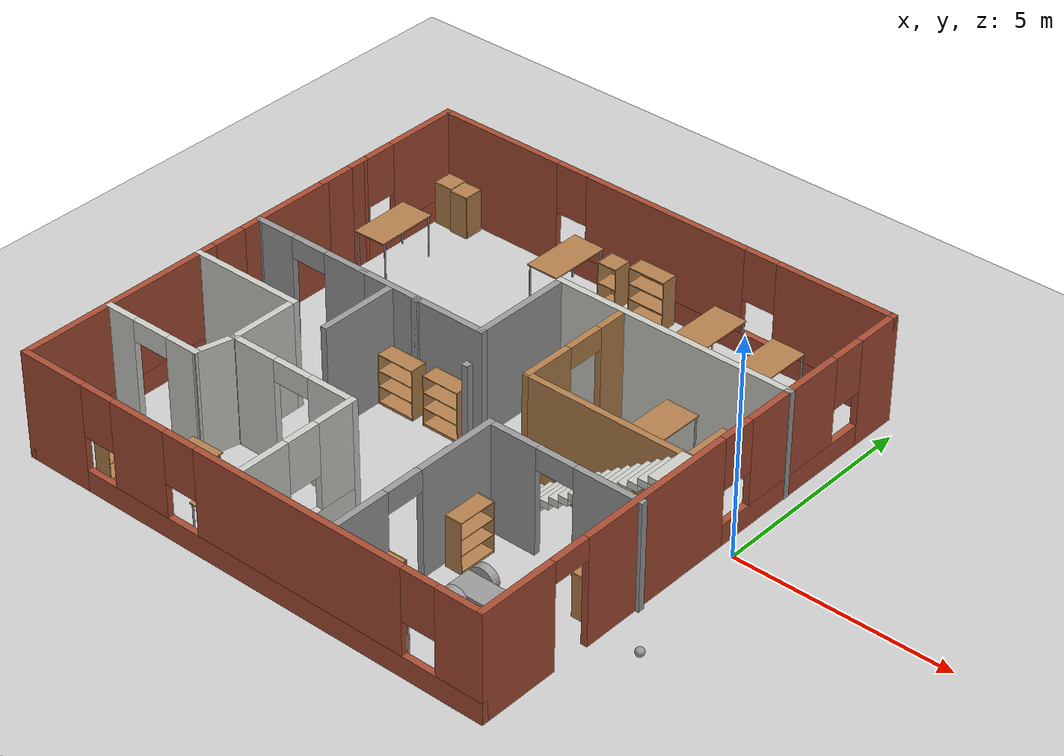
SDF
<sdf version="1.6">
 <world name="default">
  <plugin name="myOffice" filename="libmyOffice.so"/>
  <light name="sun" type="directional">
   <pose>0 0 10 0 -0 0</pose>
   <diffuse>0.8 0.8 0.8 1</diffuse>
   <specular>0.2 0.2 0.2 1</specular>
   <attenuation>
    <range>1000</range>
    <constant>0.9</constant>
    <linear>0.01</linear>
    <quadratic>0.001</quadratic>
   </attenuation>
   <direction>-0.5 0.1 -0.9</direction>
  </light>
  <model name="ground_plane">
   <static>1</static>
   <link name="link">
    <collision name="collision">
     <geometry><plane><normal>0 0 1</normal><size>100 100</size></plane></geometry>
     <surface><friction><ode><mu>100</mu><mu2>50</mu2></ode></friction></surface>
    </collision>
    <visual name="visual">
     <cast_shadows>0</cast_shadows>
     <geometry><plane><normal>0 0 1</normal><size>100 100</size></plane></geometry>
     <material>
      <script><uri>file://media/materials/scripts/gazebo.material</uri><name>Gazebo/Grey</name></script>
     </material>
    </visual>
   </link>
  </model>
  <gravity>0 0 -9.8</gravity>
  <magnetic_field>6e-06 2.3e-05 -4.2e-05</magnetic_field>
  <atmosphere type="adiabatic"/>
  <physics name="default_physics" default="0" type="ode">
   <max_step_size>0.001</max_step_size>
   <real_time_factor>1</real_time_factor>
   <real_time_update_rate>1000</real_time_update_rate>
  </physics>
  <scene><ambient>0.4 0.4 0.4 1</ambient><background>0.7 0.7 0.7 1</background><shadows>1</shadows></scene>
  <spherical_coordinates>
   <surface_model>EARTH_WGS84</surface_model>
   <latitude_deg>0</latitude_deg>
   <longitude_deg>0</longitude_deg>
   <elevation>0</elevation>
   <heading_deg>0</heading_deg>
  </spherical_coordinates>
  <model name="Building">
   <link name="Stairs_0">
    <pose>0 0.612988 0 0 -0 0</pose>
    <visual name="Stairs_0_Visual_0">
     <pose>2.30777 -1.25113 0.083333 0 -0 1.5708</pose>
     <geometry><box><size>1 0.233333 0.166667</size></box></geometry>
     <material>
      <script><uri>file://media/materials/scripts/gazebo.material</uri><name>Gazebo/CeilingTiled</name></script>
      <ambient>1 1 1 1</ambient>
      <shader type="pixel"/>
      <diffuse>1 1 1 1</diffuse>
      <specular>0 0 0 1</specular>
      <emissive>0 0 0 1</emissive>
     </material>
     <meta><layer>0</layer></meta>
    </visual>
    <visual name="Stairs_0_Visual_1">
     <pose>2.5411 -1.25113 0.25 0 -0 1.5708</pose>
     <geometry><box><size>1 0.233333 0.166667</size></box></geometry>
     <material>
      <script><uri>file://media/materials/scripts/gazebo.material</uri><name>Gazebo/CeilingTiled</name></script>
      <ambient>1 1 1 1</ambient>
      <shader type="pixel"/>
      <diffuse>1 1 1 1</diffuse>
      <specular>0 0 0 1</specular>
      <emissive>0 0 0 1</emissive>
     </material>
     <meta><layer>0</layer></meta>
    </visual>
    <visual name="Stairs_0_Visual_2">
     <pose>2.77444 -1.25113 0.416667 0 -0 1.5708</pose>
     <geometry><box><size>1 0.233333 0.166667</size></box></geometry>
     <material>
      <script><uri>file://media/materials/scripts/gazebo.material</uri><name>Gazebo/CeilingTiled</name></script>
      <ambient>1 1 1 1</ambient>
      <shader type="pixel"/>
      <diffuse>1 1 1 1</diffuse>
      <specular>0 0 0 1</specular>
      <emissive>0 0 0 1</emissive>
     </material>
     <meta><layer>0</layer></meta>
    </visual>
    <visual name="Stairs_0_Visual_3">
     <pose>3.00777 -1.25113 0.583333 0 -0 1.5708</pose>
     <geometry><box><size>1 0.233333 0.166667</size></box></geometry>
     <material>
      <script><uri>file://media/materials/scripts/gazebo.material</uri><name>Gazebo/CeilingTiled</name></script>
      <ambient>1 1 1 1</ambient>
      <shader type="pixel"/>
      <diffuse>1 1 1 1</diffuse>
      <specular>0 0 0 1</specular>
      <emissive>0 0 0 1</emissive>
     </material>
     <meta><layer>0</layer></meta>
    </visual>
    <visual name="Stairs_0_Visual_4">
     <pose>3.2411 -1.25113 0.75 0 -0 1.5708</pose>
     <geometry><box><size>1 0.233333 0.166667</size></box></geometry>
     <material>
      <script><uri>file://media/materials/scripts/gazebo.material</uri><name>Gazebo/CeilingTiled</name></script>
      <ambient>1 1 1 1</ambient>
      <shader type="pixel"/>
      <diffuse>1 1 1 1</diffuse>
      <specular>0 0 0 1</specular>
      <emissive>0 0 0 1</emissive>
     </material>
     <meta><layer>0</layer></meta>
    </visual>
    <visual name="Stairs_0_Visual_5">
     <pose>3.47444 -1.25113 0.916667 0 -0 1.5708</pose>
     <geometry><box><size>1 0.233333 0.166667</size></box></geometry>
     <material>
      <script><uri>file://media/materials/scripts/gazebo.material</uri><name>Gazebo/CeilingTiled</name></script>
      <ambient>1 1 1 1</ambient>
      <shader type="pixel"/>
      <diffuse>1 1 1 1</diffuse>
      <specular>0 0 0 1</specular>
      <emissive>0 0 0 1</emissive>
     </material>
     <meta><layer>0</layer></meta>
    </visual>
    <visual name="Stairs_0_Visual_6">
     <pose>3.70777 -1.25113 1.08333 0 -0 1.5708</pose>
     <geometry><box><size>1 0.233333 0.166667</size></box></geometry>
     <material>
      <script><uri>file://media/materials/scripts/gazebo.material</uri><name>Gazebo/CeilingTiled</name></script>
      <ambient>1 1 1 1</ambient>
      <shader type="pixel"/>
      <diffuse>1 1 1 1</diffuse>
      <specular>0 0 0 1</specular>
      <emissive>0 0 0 1</emissive>
     </material>
     <meta><layer>0</layer></meta>
    </visual>
    <visual name="Stairs_0_Visual_7">
     <pose>3.9411 -1.25113 1.25 0 -0 1.5708</pose>
     <geometry><box><size>1 0.233333 0.166667</size></box></geometry>
     <material>
      <script><uri>file://media/materials/scripts/gazebo.material</uri><name>Gazebo/CeilingTiled</name></script>
      <ambient>1 1 1 1</ambient>
      <shader type="pixel"/>
      <diffuse>1 1 1 1</diffuse>
      <specular>0 0 0 1</specular>
      <emissive>0 0 0 1</emissive>
     </material>
     <meta><layer>0</layer></meta>
    </visual>
    <visual name="Stairs_0_Visual_8">
     <pose>4.17444 -1.25113 1.41667 0 -0 1.5708</pose>
     <geometry><box><size>1 0.233333 0.166667</size></box></geometry>
     <material>
      <script><uri>file://media/materials/scripts/gazebo.material</uri><name>Gazebo/CeilingTiled</name></script>
      <ambient>1 1 1 1</ambient>
      <shader type="pixel"/>
      <diffuse>1 1 1 1</diffuse>
      <specular>0 0 0 1</specular>
      <emissive>0 0 0 1</emissive>
     </material>
     <meta><layer>0</layer></meta>
    </visual>
    <visual name="Stairs_0_Visual_9">
     <pose>4.40777 -1.25113 1.58333 0 -0 1.5708</pose>
     <geometry><box><size>1 0.233333 0.166667</size></box></geometry>
     <material>
      <script><uri>file://media/materials/scripts/gazebo.material</uri><name>Gazebo/CeilingTiled</name></script>
      <ambient>1 1 1 1</ambient>
      <shader type="pixel"/>
      <diffuse>1 1 1 1</diffuse>
      <specular>0 0 0 1</specular>
      <emissive>0 0 0 1</emissive>
     </material>
     <meta><layer>0</layer></meta>
    </visual>
    <visual name="Stairs_0_Visual_10">
     <pose>4.6411 -1.25113 1.75 0 -0 1.5708</pose>
     <geometry><box><size>1 0.233333 0.166667</size></box></geometry>
     <material>
      <script><uri>file://media/materials/scripts/gazebo.material</uri><name>Gazebo/CeilingTiled</name></script>
      <ambient>1 1 1 1</ambient>
      <shader type="pixel"/>
      <diffuse>1 1 1 1</diffuse>
      <specular>0 0 0 1</specular>
      <emissive>0 0 0 1</emissive>
     </material>
     <meta><layer>0</layer></meta>
    </visual>
    <visual name="Stairs_0_Visual_11">
     <pose>4.87444 -1.25113 1.91667 0 -0 1.5708</pose>
     <geometry><box><size>1 0.233333 0.166667</size></box></geometry>
     <material>
      <script><uri>file://media/materials/scripts/gazebo.material</uri><name>Gazebo/CeilingTiled</name></script>
      <ambient>1 1 1 1</ambient>
      <shader type="pixel"/>
      <diffuse>1 1 1 1</diffuse>
      <specular>0 0 0 1</specular>
      <emissive>0 0 0 1</emissive>
     </material>
     <meta><layer>0</layer></meta>
    </visual>
    <visual name="Stairs_0_Visual_12">
     <pose>5.10777 -1.25113 2.08333 0 -0 1.5708</pose>
     <geometry><box><size>1 0.233333 0.166667</size></box></geometry>
     <material>
      <script><uri>file://media/materials/scripts/gazebo.material</uri><name>Gazebo/CeilingTiled</name></script>
      <ambient>1 1 1 1</ambient>
      <shader type="pixel"/>
      <diffuse>1 1 1 1</diffuse>
      <specular>0 0 0 1</specular>
      <emissive>0 0 0 1</emissive>
     </material>
     <meta><layer>0</layer></meta>
    </visual>
    <visual name="Stairs_0_Visual_13">
     <pose>5.3411 -1.25113 2.25 0 -0 1.5708</pose>
     <geometry><box><size>1 0.233333 0.166667</size></box></geometry>
     <material>
      <script><uri>file://media/materials/scripts/gazebo.material</uri><name>Gazebo/CeilingTiled</name></script>
      <ambient>1 1 1 1</ambient>
      <shader type="pixel"/>
      <diffuse>1 1 1 1</diffuse>
      <specular>0 0 0 1</specular>
      <emissive>0 0 0 1</emissive>
     </material>
     <meta><layer>0</layer></meta>
    </visual>
    <visual name="Stairs_0_Visual_14">
     <pose>5.57444 -1.25113 2.41667 0 -0 1.5708</pose>
     <geometry><box><size>1 0.233333 0.166667</size></box></geometry>
     <material>
      <script><uri>file://media/materials/scripts/gazebo.material</uri><name>Gazebo/CeilingTiled</name></script>
      <ambient>1 1 1 1</ambient>
      <shader type="pixel"/>
      <diffuse>1 1 1 1</diffuse>
      <specular>0 0 0 1</specular>
      <emissive>0 0 0 1</emissive>
     </material>
     <meta><layer>0</layer></meta>
    </visual>
    <collision name="Stairs_0_Collision_0">
     <pose>2.30777 -1.25113 0.083333 0 -0 1.5708</pose>
     <geometry><box><size>1 0.233333 0.166667</size></box></geometry>
     <surface>
      <friction>
       <ode><mu>1</mu><mu2>1</mu2><fdir1>0 0 0</fdir1><slip1>0</slip1><slip2>0</slip2></ode>
       <torsional>
        <coefficient>1</coefficient>
        <patch_radius>0</patch_radius>
        <surface_radius>0</surface_radius>
        <use_patch_radius>1</use_patch_radius>
        <ode><slip>0</slip></ode>
       </torsional>
      </friction>
      <bounce><restitution_coefficient>0</restitution_coefficient><threshold>1e+06</threshold></bounce>
      <contact>
       <collide_without_contact>0</collide_without_contact>
       <collide_without_contact_bitmask>1</collide_without_contact_bitmask>
       <collide_bitmask>1</collide_bitmask>
       <ode>
        <soft_cfm>0</soft_cfm>
        <soft_erp>0.2</soft_erp>
        <kp>1e+13</kp>
        <kd>1</kd>
        <max_vel>0.01</max_vel>
        <min_depth>0</min_depth>
       </ode>
       <bullet>
        <split_impulse>1</split_impulse>
        <split_impulse_penetration_threshold>-0.01</split_impulse_penetration_threshold>
        <soft_cfm>0</soft_cfm>
        <soft_erp>0.2</soft_erp>
        <kp>1e+13</kp>
        <kd>1</kd>
       </bullet>
      </contact>
     </surface>
    </collision>
    <collision name="Stairs_0_Collision_1">
     <pose>2.5411 -1.25113 0.25 0 -0 1.5708</pose>
     <geometry><box><size>1 0.233333 0.166667</size></box></geometry>
     <surface>
      <friction>
       <ode><mu>1</mu><mu2>1</mu2><fdir1>0 0 0</fdir1><slip1>0</slip1><slip2>0</slip2></ode>
       <torsional>
        <coefficient>1</coefficient>
        <patch_radius>0</patch_radius>
        <surface_radius>0</surface_radius>
        <use_patch_radius>1</use_patch_radius>
        <ode><slip>0</slip></ode>
       </torsional>
      </friction>
      <bounce><restitution_coefficient>0</restitution_coefficient><threshold>1e+06</threshold></bounce>
      <contact>
       <collide_without_contact>0</collide_without_contact>
       <collide_without_contact_bitmask>1</collide_without_contact_bitmask>
       <collide_bitmask>1</collide_bitmask>
       <ode>
        <soft_cfm>0</soft_cfm>
        <soft_erp>0.2</soft_erp>
        <kp>1e+13</kp>
        <kd>1</kd>
        <max_vel>0.01</max_vel>
        <min_depth>0</min_depth>
       </ode>
       <bullet>
        <split_impulse>1</split_impulse>
        <split_impulse_penetration_threshold>-0.01</split_impulse_penetration_threshold>
        <soft_cfm>0</soft_cfm>
        <soft_erp>0.2</soft_erp>
        <kp>1e+13</kp>
        <kd>1</kd>
       </bullet>
      </contact>
     </surface>
    </collision>
    <collision name="Stairs_0_Collision_2">
     <pose>2.77444 -1.25113 0.416667 0 -0 1.5708</pose>
     <geometry><box><size>1 0.233333 0.166667</size></box></geometry>
     <surface>
      <friction>
       <ode><mu>1</mu><mu2>1</mu2><fdir1>0 0 0</fdir1><slip1>0</slip1><slip2>0</slip2></ode>
       <torsional>
        <coefficient>1</coefficient>
        <patch_radius>0</patch_radius>
        <surface_radius>0</surface_radius>
        <use_patch_radius>1</use_patch_radius>
        <ode><slip>0</slip></ode>
       </torsional>
      </friction>
      <bounce><restitution_coefficient>0</restitution_coefficient><threshold>1e+06</threshold></bounce>
      <contact>
       <collide_without_contact>0</collide_without_contact>
       <collide_without_contact_bitmask>1</collide_without_contact_bitmask>
       <collide_bitmask>1</collide_bitmask>
       <ode>
        <soft_cfm>0</soft_cfm>
        <soft_erp>0.2</soft_erp>
        <kp>1e+13</kp>
        <kd>1</kd>
        <max_vel>0.01</max_vel>
        <min_depth>0</min_depth>
       </ode>
       <bullet>
        <split_impulse>1</split_impulse>
        <split_impulse_penetration_threshold>-0.01</split_impulse_penetration_threshold>
        <soft_cfm>0</soft_cfm>
        <soft_erp>0.2</soft_erp>
        <kp>1e+13</kp>
        <kd>1</kd>
       </bullet>
      </contact>
     </surface>
    </collision>
    <collision name="Stairs_0_Collision_3">
     <pose>3.00777 -1.25113 0.583333 0 -0 1.5708</pose>
     <geometry><box><size>1 0.233333 0.166667</size></box></geometry>
     <surface>
      <friction>
       <ode><mu>1</mu><mu2>1</mu2><fdir1>0 0 0</fdir1><slip1>0</slip1><slip2>0</slip2></ode>
       <torsional>
        <coefficient>1</coefficient>
        <patch_radius>0</patch_radius>
        <surface_radius>0</surface_radius>
        <use_patch_radius>1</use_patch_radius>
        <ode><slip>0</slip></ode>
       </torsional>
      </friction>
      <bounce><restitution_coefficient>0</restitution_coefficient><threshold>1e+06</threshold></bounce>
      <contact>
       <collide_without_contact>0</collide_without_contact>
       <collide_without_contact_bitmask>1</collide_without_contact_bitmask>
       <collide_bitmask>1</collide_bitmask>
       <ode>
        <soft_cfm>0</soft_cfm>
        <soft_erp>0.2</soft_erp>
        <kp>1e+13</kp>
        <kd>1</kd>
        <max_vel>0.01</max_vel>
        <min_depth>0</min_depth>
       </ode>
       <bullet>
        <split_impulse>1</split_impulse>
        <split_impulse_penetration_threshold>-0.01</split_impulse_penetration_threshold>
        <soft_cfm>0</soft_cfm>
        <soft_erp>0.2</soft_erp>
        <kp>1e+13</kp>
        <kd>1</kd>
       </bullet>
      </contact>
     </surface>
    </collision>
    <collision name="Stairs_0_Collision_4">
     <pose>3.2411 -1.25113 0.75 0 -0 1.5708</pose>
     <geometry><box><size>1 0.233333 0.166667</size></box></geometry>
     <surface>
      <friction>
       <ode><mu>1</mu><mu2>1</mu2><fdir1>0 0 0</fdir1><slip1>0</slip1><slip2>0</slip2></ode>
       <torsional>
        <coefficient>1</coefficient>
        <patch_radius>0</patch_radius>
        <surface_radius>0</surface_radius>
        <use_patch_radius>1</use_patch_radius>
        <ode><slip>0</slip></ode>
       </torsional>
      </friction>
      <bounce><restitution_coefficient>0</restitution_coefficient><threshold>1e+06</threshold></bounce>
      <contact>
       <collide_without_contact>0</collide_without_contact>
       <collide_without_contact_bitmask>1</collide_without_contact_bitmask>
       <collide_bitmask>1</collide_bitmask>
       <ode>
        <soft_cfm>0</soft_cfm>
        <soft_erp>0.2</soft_erp>
        <kp>1e+13</kp>
        <kd>1</kd>
        <max_vel>0.01</max_vel>
        <min_depth>0</min_depth>
       </ode>
       <bullet>
        <split_impulse>1</split_impulse>
        <split_impulse_penetration_threshold>-0.01</split_impulse_penetration_threshold>
        <soft_cfm>0</soft_cfm>
        <soft_erp>0.2</soft_erp>
        <kp>1e+13</kp>
        <kd>1</kd>
       </bullet>
      </contact>
     </surface>
    </collision>
    <collision name="Stairs_0_Collision_5">
     <pose>3.47444 -1.25113 0.916667 0 -0 1.5708</pose>
     <geometry><box><size>1 0.233333 0.166667</size></box></geometry>
     <surface>
      <friction>
       <ode><mu>1</mu><mu2>1</mu2><fdir1>0 0 0</fdir1><slip1>0</slip1><slip2>0</slip2></ode>
       <torsional>
        <coefficient>1</coefficient>
        <patch_radius>0</patch_radius>
        <surface_radius>0</surface_radius>
        <use_patch_radius>1</use_patch_radius>
        <ode><slip>0</slip></ode>
       </torsional>
      </friction>
      <bounce><restitution_coefficient>0</restitution_coefficient><threshold>1e+06</threshold></bounce>
      <contact>
       <collide_without_contact>0</collide_without_contact>
       <collide_without_contact_bitmask>1</collide_without_contact_bitmask>
       <collide_bitmask>1</collide_bitmask>
       <ode>
        <soft_cfm>0</soft_cfm>
        <soft_erp>0.2</soft_erp>
        <kp>1e+13</kp>
        <kd>1</kd>
        <max_vel>0.01</max_vel>
        <min_depth>0</min_depth>
       </ode>
       <bullet>
        <split_impulse>1</split_impulse>
        <split_impulse_penetration_threshold>-0.01</split_impulse_penetration_threshold>
        <soft_cfm>0</soft_cfm>
        <soft_erp>0.2</soft_erp>
        <kp>1e+13</kp>
        <kd>1</kd>
       </bullet>
      </contact>
     </surface>
    </collision>
    <collision name="Stairs_0_Collision_6">
     <pose>3.70777 -1.25113 1.08333 0 -0 1.5708</pose>
     <geometry><box><size>1 0.233333 0.166667</size></box></geometry>
     <surface>
      <friction>
       <ode><mu>1</mu><mu2>1</mu2><fdir1>0 0 0</fdir1><slip1>0</slip1><slip2>0</slip2></ode>
       <torsional>
        <coefficient>1</coefficient>
        <patch_radius>0</patch_radius>
        <surface_radius>0</surface_radius>
        <use_patch_radius>1</use_patch_radius>
        <ode><slip>0</slip></ode>
       </torsional>
      </friction>
      <bounce><restitution_coefficient>0</restitution_coefficient><threshold>1e+06</threshold></bounce>
      <contact>
       <collide_without_contact>0</collide_without_contact>
       <collide_without_contact_bitmask>1</collide_without_contact_bitmask>
       <collide_bitmask>1</collide_bitmask>
       <ode>
        <soft_cfm>0</soft_cfm>
        <soft_erp>0.2</soft_erp>
        <kp>1e+13</kp>
        <kd>1</kd>
        <max_vel>0.01</max_vel>
        <min_depth>0</min_depth>
       </ode>
       <bullet>
        <split_impulse>1</split_impulse>
        <split_impulse_penetration_threshold>-0.01</split_impulse_penetration_threshold>
        <soft_cfm>0</soft_cfm>
        <soft_erp>0.2</soft_erp>
        <kp>1e+13</kp>
        <kd>1</kd>
       </bullet>
      </contact>
     </surface>
    </collision>
    <collision name="Stairs_0_Collision_7">
     <pose>3.9411 -1.25113 1.25 0 -0 1.5708</pose>
     <geometry><box><size>1 0.233333 0.166667</size></box></geometry>
     <surface>
      <friction>
       <ode><mu>1</mu><mu2>1</mu2><fdir1>0 0 0</fdir1><slip1>0</slip1><slip2>0</slip2></ode>
       <torsional>
        <coefficient>1</coefficient>
        <patch_radius>0</patch_radius>
        <surface_radius>0</surface_radius>
        <use_patch_radius>1</use_patch_radius>
        <ode><slip>0</slip></ode>
       </torsional>
      </friction>
      <bounce><restitution_coefficient>0</restitution_coefficient><threshold>1e+06</threshold></bounce>
      <contact>
       <collide_without_contact>0</collide_without_contact>
       <collide_without_contact_bitmask>1</collide_without_contact_bitmask>
       <collide_bitmask>1</collide_bitmask>
       <ode>
        <soft_cfm>0</soft_cfm>
        <soft_erp>0.2</soft_erp>
        <kp>1e+13</kp>
        <kd>1</kd>
        <max_vel>0.01</max_vel>
        <min_depth>0</min_depth>
       </ode>
       <bullet>
        <split_impulse>1</split_impulse>
        <split_impulse_penetration_threshold>-0.01</split_impulse_penetration_threshold>
        <soft_cfm>0</soft_cfm>
        <soft_erp>0.2</soft_erp>
        <kp>1e+13</kp>
        <kd>1</kd>
       </bullet>
      </contact>
     </surface>
    </collision>
    <collision name="Stairs_0_Collision_8">
     <pose>4.17444 -1.25113 1.41667 0 -0 1.5708</pose>
     <geometry><box><size>1 0.233333 0.166667</size></box></geometry>
     <surface>
      <friction>
       <ode><mu>1</mu><mu2>1</mu2><fdir1>0 0 0</fdir1><slip1>0</slip1><slip2>0</slip2></ode>
       <torsional>
        <coefficient>1</coefficient>
        <patch_radius>0</patch_radius>
        <surface_radius>0</surface_radius>
        <use_patch_radius>1</use_patch_radius>
        <ode><slip>0</slip></ode>
       </torsional>
      </friction>
      <bounce><restitution_coefficient>0</restitution_coefficient><threshold>1e+06</threshold></bounce>
      <contact>
       <collide_without_contact>0</collide_without_contact>
       <collide_without_contact_bitmask>1</collide_without_contact_bitmask>
       <collide_bitmask>1</collide_bitmask>
       <ode>
        <soft_cfm>0</soft_cfm>
        <soft_erp>0.2</soft_erp>
        <kp>1e+13</kp>
        <kd>1</kd>
        <max_vel>0.01</max_vel>
        <min_depth>0</min_depth>
       </ode>
       <bullet>
        <split_impulse>1</split_impulse>
        <split_impulse_penetration_threshold>-0.01</split_impulse_penetration_threshold>
        <soft_cfm>0</soft_cfm>
        <soft_erp>0.2</soft_erp>
        <kp>1e+13</kp>
        <kd>1</kd>
       </bullet>
      </contact>
     </surface>
    </collision>
    <collision name="Stairs_0_Collision_14">
     <pose>5.57444 -1.25113 2.41667 0 -0 1.5708</pose>
     <geometry><box><size>1 0.233333 0.166667</size></box></geometry>
     <surface>
      <friction>
       <ode><mu>1</mu><mu2>1</mu2><fdir1>0 0 0</fdir1><slip1>0</slip1><slip2>0</slip2></ode>
       <torsional>
        <coefficient>1</coefficient>
        <patch_radius>0</patch_radius>
        <surface_radius>0</surface_radius>
        <use_patch_radius>1</use_patch_radius>
        <ode><slip>0</slip></ode>
       </torsional>
      </friction>
      <bounce><restitution_coefficient>0</restitution_coefficient><threshold>1e+06</threshold></bounce>
      <contact>
       <collide_without_contact>0</collide_without_contact>
       <collide_without_contact_bitmask>1</collide_without_contact_bitmask>
       <collide_bitmask>1</collide_bitmask>
       <ode>
        <soft_cfm>0</soft_cfm>
        <soft_erp>0.2</soft_erp>
        <kp>1e+13</kp>
        <kd>1</kd>
        <max_vel>0.01</max_vel>
        <min_depth>0</min_depth>
       </ode>
       <bullet>
        <split_impulse>1</split_impulse>
        <split_impulse_penetration_threshold>-0.01</split_impulse_penetration_threshold>
        <soft_cfm>0</soft_cfm>
        <soft_erp>0.2</soft_erp>
        <kp>1e+13</kp>
        <kd>1</kd>
       </bullet>
      </contact>
     </surface>
    </collision>
    <collision name="Stairs_0_Collision_9">
     <pose>4.40777 -1.25113 1.58333 0 -0 1.5708</pose>
     <geometry><box><size>1 0.233333 0.166667</size></box></geometry>
     <surface>
      <friction>
       <ode><mu>1</mu><mu2>1</mu2><fdir1>0 0 0</fdir1><slip1>0</slip1><slip2>0</slip2></ode>
       <torsional>
        <coefficient>1</coefficient>
        <patch_radius>0</patch_radius>
        <surface_radius>0</surface_radius>
        <use_patch_radius>1</use_patch_radius>
        <ode><slip>0</slip></ode>
       </torsional>
      </friction>
      <bounce><restitution_coefficient>0</restitution_coefficient><threshold>1e+06</threshold></bounce>
      <contact>
       <collide_without_contact>0</collide_without_contact>
       <collide_without_contact_bitmask>1</collide_without_contact_bitmask>
       <collide_bitmask>1</collide_bitmask>
       <ode>
        <soft_cfm>0</soft_cfm>
        <soft_erp>0.2</soft_erp>
        <kp>1e+13</kp>
        <kd>1</kd>
        <max_vel>0.01</max_vel>
        <min_depth>0</min_depth>
       </ode>
       <bullet>
        <split_impulse>1</split_impulse>
        <split_impulse_penetration_threshold>-0.01</split_impulse_penetration_threshold>
        <soft_cfm>0</soft_cfm>
        <soft_erp>0.2</soft_erp>
        <kp>1e+13</kp>
        <kd>1</kd>
       </bullet>
      </contact>
     </surface>
    </collision>
    <collision name="Stairs_0_Collision_10">
     <pose>4.6411 -1.25113 1.75 0 -0 1.5708</pose>
     <geometry><box><size>1 0.233333 0.166667</size></box></geometry>
     <surface>
      <friction>
       <ode><mu>1</mu><mu2>1</mu2><fdir1>0 0 0</fdir1><slip1>0</slip1><slip2>0</slip2></ode>
       <torsional>
        <coefficient>1</coefficient>
        <patch_radius>0</patch_radius>
        <surface_radius>0</surface_radius>
        <use_patch_radius>1</use_patch_radius>
        <ode><slip>0</slip></ode>
       </torsional>
      </friction>
      <bounce><restitution_coefficient>0</restitution_coefficient><threshold>1e+06</threshold></bounce>
      <contact>
       <collide_without_contact>0</collide_without_contact>
       <collide_without_contact_bitmask>1</collide_without_contact_bitmask>
       <collide_bitmask>1</collide_bitmask>
       <ode>
        <soft_cfm>0</soft_cfm>
        <soft_erp>0.2</soft_erp>
        <kp>1e+13</kp>
        <kd>1</kd>
        <max_vel>0.01</max_vel>
        <min_depth>0</min_depth>
       </ode>
       <bullet>
        <split_impulse>1</split_impulse>
        <split_impulse_penetration_threshold>-0.01</split_impulse_penetration_threshold>
        <soft_cfm>0</soft_cfm>
        <soft_erp>0.2</soft_erp>
        <kp>1e+13</kp>
        <kd>1</kd>
       </bullet>
      </contact>
     </surface>
    </collision>
    <collision name="Stairs_0_Collision_11">
     <pose>4.87444 -1.25113 1.91667 0 -0 1.5708</pose>
     <geometry><box><size>1 0.233333 0.166667</size></box></geometry>
     <surface>
      <friction>
       <ode><mu>1</mu><mu2>1</mu2><fdir1>0 0 0</fdir1><slip1>0</slip1><slip2>0</slip2></ode>
       <torsional>
        <coefficient>1</coefficient>
        <patch_radius>0</patch_radius>
        <surface_radius>0</surface_radius>
        <use_patch_radius>1</use_patch_radius>
        <ode><slip>0</slip></ode>
       </torsional>
      </friction>
      <bounce><restitution_coefficient>0</restitution_coefficient><threshold>1e+06</threshold></bounce>
      <contact>
       <collide_without_contact>0</collide_without_contact>
       <collide_without_contact_bitmask>1</collide_without_contact_bitmask>
       <collide_bitmask>1</collide_bitmask>
       <ode>
        <soft_cfm>0</soft_cfm>
        <soft_erp>0.2</soft_erp>
        <kp>1e+13</kp>
        <kd>1</kd>
        <max_vel>0.01</max_vel>
        <min_depth>0</min_depth>
       </ode>
       <bullet>
        <split_impulse>1</split_impulse>
        <split_impulse_penetration_threshold>-0.01</split_impulse_penetration_threshold>
        <soft_cfm>0</soft_cfm>
        <soft_erp>0.2</soft_erp>
        <kp>1e+13</kp>
        <kd>1</kd>
       </bullet>
      </contact>
     </surface>
    </collision>
    <collision name="Stairs_0_Collision_12">
     <pose>5.10777 -1.25113 2.08333 0 -0 1.5708</pose>
     <geometry><box><size>1 0.233333 0.166667</size></box></geometry>
     <surface>
      <friction>
       <ode><mu>1</mu><mu2>1</mu2><fdir1>0 0 0</fdir1><slip1>0</slip1><slip2>0</slip2></ode>
       <torsional>
        <coefficient>1</coefficient>
        <patch_radius>0</patch_radius>
        <surface_radius>0</surface_radius>
        <use_patch_radius>1</use_patch_radius>
        <ode><slip>0</slip></ode>
       </torsional>
      </friction>
      <bounce><restitution_coefficient>0</restitution_coefficient><threshold>1e+06</threshold></bounce>
      <contact>
       <collide_without_contact>0</collide_without_contact>
       <collide_without_contact_bitmask>1</collide_without_contact_bitmask>
       <collide_bitmask>1</collide_bitmask>
       <ode>
        <soft_cfm>0</soft_cfm>
        <soft_erp>0.2</soft_erp>
        <kp>1e+13</kp>
        <kd>1</kd>
        <max_vel>0.01</max_vel>
        <min_depth>0</min_depth>
       </ode>
       <bullet>
        <split_impulse>1</split_impulse>
        <split_impulse_penetration_threshold>-0.01</split_impulse_penetration_threshold>
        <soft_cfm>0</soft_cfm>
        <soft_erp>0.2</soft_erp>
        <kp>1e+13</kp>
        <kd>1</kd>
       </bullet>
      </contact>
     </surface>
    </collision>
    <collision name="Stairs_0_Collision_13">
     <pose>5.3411 -1.25113 2.25 0 -0 1.5708</pose>
     <geometry><box><size>1 0.233333 0.166667</size></box></geometry>
     <surface>
      <friction>
       <ode><mu>1</mu><mu2>1</mu2><fdir1>0 0 0</fdir1><slip1>0</slip1><slip2>0</slip2></ode>
       <torsional>
        <coefficient>1</coefficient>
        <patch_radius>0</patch_radius>
        <surface_radius>0</surface_radius>
        <use_patch_radius>1</use_patch_radius>
        <ode><slip>0</slip></ode>
       </torsional>
      </friction>
      <bounce><restitution_coefficient>0</restitution_coefficient><threshold>1e+06</threshold></bounce>
      <contact>
       <collide_without_contact>0</collide_without_contact>
       <collide_without_contact_bitmask>1</collide_without_contact_bitmask>
       <collide_bitmask>1</collide_bitmask>
       <ode>
        <soft_cfm>0</soft_cfm>
        <soft_erp>0.2</soft_erp>
        <kp>1e+13</kp>
        <kd>1</kd>
        <max_vel>0.01</max_vel>
        <min_depth>0</min_depth>
       </ode>
       <bullet>
        <split_impulse>1</split_impulse>
        <split_impulse_penetration_threshold>-0.01</split_impulse_penetration_threshold>
        <soft_cfm>0</soft_cfm>
        <soft_erp>0.2</soft_erp>
        <kp>1e+13</kp>
        <kd>1</kd>
       </bullet>
      </contact>
     </surface>
    </collision>
   </link>
   <link name="Wall_0">
    <pose>-5.83944 -1.9 0 0 0 -1.5708</pose>
    <visual name="Wall_0_Visual_0">
     <pose>-2.91813 0 1.25 0 -0 0</pose>
     <geometry><box><size>2.41374 0.15 2.5</size></box></geometry>
     <material>
      <script><uri>file://media/materials/scripts/gazebo.material</uri><name>Gazebo/Bricks</name></script>
      <ambient>1 1 1 1</ambient>
      <shader type="pixel"/>
      <diffuse>1 1 1 1</diffuse>
      <specular>0.2 0.2 0.2 1</specular>
      <emissive>0 0 0 1</emissive>
     </material>
     <meta><layer>0</layer></meta>
    </visual>
    <visual name="Wall_0_Visual_1">
     <pose>1.20687 0 0.25 0 -0 0</pose>
     <geometry><box><size>5.83626 0.15 0.5</size></box></geometry>
     <material>
      <script><uri>file://media/materials/scripts/gazebo.material</uri><name>Gazebo/Bricks</name></script>
      <ambient>1 1 1 1</ambient>
      <shader type="pixel"/>
      <diffuse>1 1 1 1</diffuse>
      <specular>0.2 0.2 0.2 1</specular>
      <emissive>0 0 0 1</emissive>
     </material>
     <meta><layer>0</layer></meta>
    </visual>
    <visual name="Wall_0_Visual_2">
     <pose>1.60687 0 1.5 0 -0 0</pose>
     <geometry><box><size>5.03626 0.15 2</size></box></geometry>
     <material>
      <script><uri>file://media/materials/scripts/gazebo.material</uri><name>Gazebo/Bricks</name></script>
      <ambient>1 1 1 1</ambient>
      <shader type="pixel"/>
      <diffuse>1 1 1 1</diffuse>
      <specular>0.2 0.2 0.2 1</specular>
      <emissive>0 0 0 1</emissive>
     </material>
     <meta><layer>0</layer></meta>
    </visual>
    <visual name="Wall_0_Visual_3">
     <pose>-1.31126 0 1.9 0 -0 0</pose>
     <geometry><box><size>0.8 0.15 1.2</size></box></geometry>
     <material>
      <script><uri>file://media/materials/scripts/gazebo.material</uri><name>Gazebo/Bricks</name></script>
      <ambient>1 1 1 1</ambient>
      <shader type="pixel"/>
      <diffuse>1 1 1 1</diffuse>
      <specular>0.2 0.2 0.2 1</specular>
      <emissive>0 0 0 1</emissive>
     </material>
     <meta><layer>0</layer></meta>
    </visual>
    <collision name="Wall_0_Collision_0">
     <pose>-2.91813 0 1.25 0 -0 0</pose>
     <geometry><box><size>2.41374 0.15 2.5</size></box></geometry>
     <surface>
      <friction>
       <ode><mu>1</mu><mu2>1</mu2><fdir1>0 0 0</fdir1><slip1>0</slip1><slip2>0</slip2></ode>
       <torsional>
        <coefficient>1</coefficient>
        <patch_radius>0</patch_radius>
        <surface_radius>0</surface_radius>
        <use_patch_radius>1</use_patch_radius>
        <ode><slip>0</slip></ode>
       </torsional>
      </friction>
      <bounce><restitution_coefficient>0</restitution_coefficient><threshold>1e+06</threshold></bounce>
      <contact>
       <collide_without_contact>0</collide_without_contact>
       <collide_without_contact_bitmask>1</collide_without_contact_bitmask>
       <collide_bitmask>1</collide_bitmask>
       <ode>
        <soft_cfm>0</soft_cfm>
        <soft_erp>0.2</soft_erp>
        <kp>1e+13</kp>
        <kd>1</kd>
        <max_vel>0.01</max_vel>
        <min_depth>0</min_depth>
       </ode>
       <bullet>
        <split_impulse>1</split_impulse>
        <split_impulse_penetration_threshold>-0.01</split_impulse_penetration_threshold>
        <soft_cfm>0</soft_cfm>
        <soft_erp>0.2</soft_erp>
        <kp>1e+13</kp>
        <kd>1</kd>
       </bullet>
      </contact>
     </surface>
    </collision>
    <collision name="Wall_0_Collision_1">
     <pose>1.20687 0 0.25 0 -0 0</pose>
     <geometry><box><size>5.83626 0.15 0.5</size></box></geometry>
     <surface>
      <friction>
       <ode><mu>1</mu><mu2>1</mu2><fdir1>0 0 0</fdir1><slip1>0</slip1><slip2>0</slip2></ode>
       <torsional>
        <coefficient>1</coefficient>
        <patch_radius>0</patch_radius>
        <surface_radius>0</surface_radius>
        <use_patch_radius>1</use_patch_radius>
        <ode><slip>0</slip></ode>
       </torsional>
      </friction>
      <bounce><restitution_coefficient>0</restitution_coefficient><threshold>1e+06</threshold></bounce>
      <contact>
       <collide_without_contact>0</collide_without_contact>
       <collide_without_contact_bitmask>1</collide_without_contact_bitmask>
       <collide_bitmask>1</collide_bitmask>
       <ode>
        <soft_cfm>0</soft_cfm>
        <soft_erp>0.2</soft_erp>
        <kp>1e+13</kp>
        <kd>1</kd>
        <max_vel>0.01</max_vel>
        <min_depth>0</min_depth>
       </ode>
       <bullet>
        <split_impulse>1</split_impulse>
        <split_impulse_penetration_threshold>-0.01</split_impulse_penetration_threshold>
        <soft_cfm>0</soft_cfm>
        <soft_erp>0.2</soft_erp>
        <kp>1e+13</kp>
        <kd>1</kd>
       </bullet>
      </contact>
     </surface>
    </collision>
    <collision name="Wall_0_Collision_2">
     <pose>1.60687 0 1.5 0 -0 0</pose>
     <geometry><box><size>5.03626 0.15 2</size></box></geometry>
     <surface>
      <friction>
       <ode><mu>1</mu><mu2>1</mu2><fdir1>0 0 0</fdir1><slip1>0</slip1><slip2>0</slip2></ode>
       <torsional>
        <coefficient>1</coefficient>
        <patch_radius>0</patch_radius>
        <surface_radius>0</surface_radius>
        <use_patch_radius>1</use_patch_radius>
        <ode><slip>0</slip></ode>
       </torsional>
      </friction>
      <bounce><restitution_coefficient>0</restitution_coefficient><threshold>1e+06</threshold></bounce>
      <contact>
       <collide_without_contact>0</collide_without_contact>
       <collide_without_contact_bitmask>1</collide_without_contact_bitmask>
       <collide_bitmask>1</collide_bitmask>
       <ode>
        <soft_cfm>0</soft_cfm>
        <soft_erp>0.2</soft_erp>
        <kp>1e+13</kp>
        <kd>1</kd>
        <max_vel>0.01</max_vel>
        <min_depth>0</min_depth>
       </ode>
       <bullet>
        <split_impulse>1</split_impulse>
        <split_impulse_penetration_threshold>-0.01</split_impulse_penetration_threshold>
        <soft_cfm>0</soft_cfm>
        <soft_erp>0.2</soft_erp>
        <kp>1e+13</kp>
        <kd>1</kd>
       </bullet>
      </contact>
     </surface>
    </collision>
    <collision name="Wall_0_Collision_3">
     <pose>-1.31126 0 1.9 0 -0 0</pose>
     <geometry><box><size>0.8 0.15 1.2</size></box></geometry>
     <surface>
      <friction>
       <ode><mu>1</mu><mu2>1</mu2><fdir1>0 0 0</fdir1><slip1>0</slip1><slip2>0</slip2></ode>
       <torsional>
        <coefficient>1</coefficient>
        <patch_radius>0</patch_radius>
        <surface_radius>0</surface_radius>
        <use_patch_radius>1</use_patch_radius>
        <ode><slip>0</slip></ode>
       </torsional>
      </friction>
      <bounce><restitution_coefficient>0</restitution_coefficient><threshold>1e+06</threshold></bounce>
      <contact>
       <collide_without_contact>0</collide_without_contact>
       <collide_without_contact_bitmask>1</collide_without_contact_bitmask>
       <collide_bitmask>1</collide_bitmask>
       <ode>
        <soft_cfm>0</soft_cfm>
        <soft_erp>0.2</soft_erp>
        <kp>1e+13</kp>
        <kd>1</kd>
        <max_vel>0.01</max_vel>
        <min_depth>0</min_depth>
       </ode>
       <bullet>
        <split_impulse>1</split_impulse>
        <split_impulse_penetration_threshold>-0.01</split_impulse_penetration_threshold>
        <soft_cfm>0</soft_cfm>
        <soft_erp>0.2</soft_erp>
        <kp>1e+13</kp>
        <kd>1</kd>
       </bullet>
      </contact>
     </surface>
    </collision>
   </link>
   <link name="Wall_1">
    <pose>-0.039438 -5.95 0 0 -0 0</pose>
    <visual name="Wall_1_Visual_4">
     <pose>5.31994 0 1.5 0 -0 0</pose>
     <geometry><box><size>1.11013 0.15 2</size></box></geometry>
     <material>
      <script><uri>file://media/materials/scripts/gazebo.material</uri><name>Gazebo/Bricks</name></script>
      <ambient>1 1 1 1</ambient>
      <shader type="pixel"/>
      <diffuse>1 1 1 1</diffuse>
      <specular>0.2 0.2 0.2 1</specular>
      <emissive>0 0 0 1</emissive>
     </material>
     <meta><layer>0</layer></meta>
    </visual>
    <visual name="Wall_1_Visual_0">
     <pose>-5.03898 0 1.25 0 -0 0</pose>
     <geometry><box><size>1.67205 0.15 2.5</size></box></geometry>
     <material>
      <script><uri>file://media/materials/scripts/gazebo.material</uri><name>Gazebo/Bricks</name></script>
      <ambient>1 1 1 1</ambient>
      <shader type="pixel"/>
      <diffuse>1 1 1 1</diffuse>
      <specular>0.2 0.2 0.2 1</specular>
      <emissive>0 0 0 1</emissive>
     </material>
     <meta><layer>0</layer></meta>
    </visual>
    <visual name="Wall_1_Visual_1">
     <pose>0.836024 0 0.25 0 -0 0</pose>
     <geometry><box><size>10.078 0.15 0.5</size></box></geometry>
     <material>
      <script><uri>file://media/materials/scripts/gazebo.material</uri><name>Gazebo/Bricks</name></script>
      <ambient>1 1 1 1</ambient>
      <shader type="pixel"/>
      <diffuse>1 1 1 1</diffuse>
      <specular>0.2 0.2 0.2 1</specular>
      <emissive>0 0 0 1</emissive>
     </material>
     <meta><layer>0</layer></meta>
    </visual>
    <visual name="Wall_1_Visual_2">
     <pose>-2.69545 0 1.5 0 -0 0</pose>
     <geometry><box><size>1.415 0.15 2</size></box></geometry>
     <material>
      <script><uri>file://media/materials/scripts/gazebo.material</uri><name>Gazebo/Bricks</name></script>
      <ambient>1 1 1 1</ambient>
      <shader type="pixel"/>
      <diffuse>1 1 1 1</diffuse>
      <specular>0.2 0.2 0.2 1</specular>
      <emissive>0 0 0 1</emissive>
     </material>
     <meta><layer>0</layer></meta>
    </visual>
    <visual name="Wall_1_Visual_3">
     <pose>1.38846 0 1.5 0 -0 0</pose>
     <geometry><box><size>5.15282 0.15 2</size></box></geometry>
     <material>
      <script><uri>file://media/materials/scripts/gazebo.material</uri><name>Gazebo/Bricks</name></script>
      <ambient>1 1 1 1</ambient>
      <shader type="pixel"/>
      <diffuse>1 1 1 1</diffuse>
      <specular>0.2 0.2 0.2 1</specular>
      <emissive>0 0 0 1</emissive>
     </material>
     <meta><layer>0</layer></meta>
    </visual>
    <visual name="Wall_1_Visual_5">
     <pose>-3.80295 0 1.9 0 -0 0</pose>
     <geometry><box><size>0.8 0.15 1.2</size></box></geometry>
     <material>
      <script><uri>file://media/materials/scripts/gazebo.material</uri><name>Gazebo/Bricks</name></script>
      <ambient>1 1 1 1</ambient>
      <shader type="pixel"/>
      <diffuse>1 1 1 1</diffuse>
      <specular>0.2 0.2 0.2 1</specular>
      <emissive>0 0 0 1</emissive>
     </material>
     <meta><layer>0</layer></meta>
    </visual>
    <visual name="Wall_1_Visual_6">
     <pose>-1.58795 0 1.9 0 -0 0</pose>
     <geometry><box><size>0.8 0.15 1.2</size></box></geometry>
     <material>
      <script><uri>file://media/materials/scripts/gazebo.material</uri><name>Gazebo/Bricks</name></script>
      <ambient>1 1 1 1</ambient>
      <shader type="pixel"/>
      <diffuse>1 1 1 1</diffuse>
      <specular>0.2 0.2 0.2 1</specular>
      <emissive>0 0 0 1</emissive>
     </material>
     <meta><layer>0</layer></meta>
    </visual>
    <visual name="Wall_1_Visual_7">
     <pose>4.36487 0 1.9 0 -0 0</pose>
     <geometry><box><size>0.8 0.15 1.2</size></box></geometry>
     <material>
      <script><uri>file://media/materials/scripts/gazebo.material</uri><name>Gazebo/Bricks</name></script>
      <ambient>1 1 1 1</ambient>
      <shader type="pixel"/>
      <diffuse>1 1 1 1</diffuse>
      <specular>0.2 0.2 0.2 1</specular>
      <emissive>0 0 0 1</emissive>
     </material>
     <meta><layer>0</layer></meta>
    </visual>
    <collision name="Wall_1_Collision_0">
     <pose>-5.03898 0 1.25 0 -0 0</pose>
     <geometry><box><size>1.67205 0.15 2.5</size></box></geometry>
     <surface>
      <friction>
       <ode><mu>1</mu><mu2>1</mu2><fdir1>0 0 0</fdir1><slip1>0</slip1><slip2>0</slip2></ode>
       <torsional>
        <coefficient>1</coefficient>
        <patch_radius>0</patch_radius>
        <surface_radius>0</surface_radius>
        <use_patch_radius>1</use_patch_radius>
        <ode><slip>0</slip></ode>
       </torsional>
      </friction>
      <bounce><restitution_coefficient>0</restitution_coefficient><threshold>1e+06</threshold></bounce>
      <contact>
       <collide_without_contact>0</collide_without_contact>
       <collide_without_contact_bitmask>1</collide_without_contact_bitmask>
       <collide_bitmask>1</collide_bitmask>
       <ode>
        <soft_cfm>0</soft_cfm>
        <soft_erp>0.2</soft_erp>
        <kp>1e+13</kp>
        <kd>1</kd>
        <max_vel>0.01</max_vel>
        <min_depth>0</min_depth>
       </ode>
       <bullet>
        <split_impulse>1</split_impulse>
        <split_impulse_penetration_threshold>-0.01</split_impulse_penetration_threshold>
        <soft_cfm>0</soft_cfm>
        <soft_erp>0.2</soft_erp>
        <kp>1e+13</kp>
        <kd>1</kd>
       </bullet>
      </contact>
     </surface>
    </collision>
    <collision name="Wall_1_Collision_1">
     <pose>0.836024 0 0.25 0 -0 0</pose>
     <geometry><box><size>10.078 0.15 0.5</size></box></geometry>
     <surface>
      <friction>
       <ode><mu>1</mu><mu2>1</mu2><fdir1>0 0 0</fdir1><slip1>0</slip1><slip2>0</slip2></ode>
       <torsional>
        <coefficient>1</coefficient>
        <patch_radius>0</patch_radius>
        <surface_radius>0</surface_radius>
        <use_patch_radius>1</use_patch_radius>
        <ode><slip>0</slip></ode>
       </torsional>
      </friction>
      <bounce><restitution_coefficient>0</restitution_coefficient><threshold>1e+06</threshold></bounce>
      <contact>
       <collide_without_contact>0</collide_without_contact>
       <collide_without_contact_bitmask>1</collide_without_contact_bitmask>
       <collide_bitmask>1</collide_bitmask>
       <ode>
        <soft_cfm>0</soft_cfm>
        <soft_erp>0.2</soft_erp>
        <kp>1e+13</kp>
        <kd>1</kd>
        <max_vel>0.01</max_vel>
        <min_depth>0</min_depth>
       </ode>
       <bullet>
        <split_impulse>1</split_impulse>
        <split_impulse_penetration_threshold>-0.01</split_impulse_penetration_threshold>
        <soft_cfm>0</soft_cfm>
        <soft_erp>0.2</soft_erp>
        <kp>1e+13</kp>
        <kd>1</kd>
       </bullet>
      </contact>
     </surface>
    </collision>
    <collision name="Wall_1_Collision_5">
     <pose>-3.80295 0 1.9 0 -0 0</pose>
     <geometry><box><size>0.8 0.15 1.2</size></box></geometry>
     <surface>
      <friction>
       <ode><mu>1</mu><mu2>1</mu2><fdir1>0 0 0</fdir1><slip1>0</slip1><slip2>0</slip2></ode>
       <torsional>
        <coefficient>1</coefficient>
        <patch_radius>0</patch_radius>
        <surface_radius>0</surface_radius>
        <use_patch_radius>1</use_patch_radius>
        <ode><slip>0</slip></ode>
       </torsional>
      </friction>
      <bounce><restitution_coefficient>0</restitution_coefficient><threshold>1e+06</threshold></bounce>
      <contact>
       <collide_without_contact>0</collide_without_contact>
       <collide_without_contact_bitmask>1</collide_without_contact_bitmask>
       <collide_bitmask>1</collide_bitmask>
       <ode>
        <soft_cfm>0</soft_cfm>
        <soft_erp>0.2</soft_erp>
        <kp>1e+13</kp>
        <kd>1</kd>
        <max_vel>0.01</max_vel>
        <min_depth>0</min_depth>
       </ode>
       <bullet>
        <split_impulse>1</split_impulse>
        <split_impulse_penetration_threshold>-0.01</split_impulse_penetration_threshold>
        <soft_cfm>0</soft_cfm>
        <soft_erp>0.2</soft_erp>
        <kp>1e+13</kp>
        <kd>1</kd>
       </bullet>
      </contact>
     </surface>
    </collision>
    <collision name="Wall_1_Collision_2">
     <pose>-2.69545 0 1.5 0 -0 0</pose>
     <geometry><box><size>1.415 0.15 2</size></box></geometry>
     <surface>
      <friction>
       <ode><mu>1</mu><mu2>1</mu2><fdir1>0 0 0</fdir1><slip1>0</slip1><slip2>0</slip2></ode>
       <torsional>
        <coefficient>1</coefficient>
        <patch_radius>0</patch_radius>
        <surface_radius>0</surface_radius>
        <use_patch_radius>1</use_patch_radius>
        <ode><slip>0</slip></ode>
       </torsional>
      </friction>
      <bounce><restitution_coefficient>0</restitution_coefficient><threshold>1e+06</threshold></bounce>
      <contact>
       <collide_without_contact>0</collide_without_contact>
       <collide_without_contact_bitmask>1</collide_without_contact_bitmask>
       <collide_bitmask>1</collide_bitmask>
       <ode>
        <soft_cfm>0</soft_cfm>
        <soft_erp>0.2</soft_erp>
        <kp>1e+13</kp>
        <kd>1</kd>
        <max_vel>0.01</max_vel>
        <min_depth>0</min_depth>
       </ode>
       <bullet>
        <split_impulse>1</split_impulse>
        <split_impulse_penetration_threshold>-0.01</split_impulse_penetration_threshold>
        <soft_cfm>0</soft_cfm>
        <soft_erp>0.2</soft_erp>
        <kp>1e+13</kp>
        <kd>1</kd>
       </bullet>
      </contact>
     </surface>
    </collision>
    <collision name="Wall_1_Collision_3">
     <pose>1.38846 0 1.5 0 -0 0</pose>
     <geometry><box><size>5.15282 0.15 2</size></box></geometry>
     <surface>
      <friction>
       <ode><mu>1</mu><mu2>1</mu2><fdir1>0 0 0</fdir1><slip1>0</slip1><slip2>0</slip2></ode>
       <torsional>
        <coefficient>1</coefficient>
        <patch_radius>0</patch_radius>
        <surface_radius>0</surface_radius>
        <use_patch_radius>1</use_patch_radius>
        <ode><slip>0</slip></ode>
       </torsional>
      </friction>
      <bounce><restitution_coefficient>0</restitution_coefficient><threshold>1e+06</threshold></bounce>
      <contact>
       <collide_without_contact>0</collide_without_contact>
       <collide_without_contact_bitmask>1</collide_without_contact_bitmask>
       <collide_bitmask>1</collide_bitmask>
       <ode>
        <soft_cfm>0</soft_cfm>
        <soft_erp>0.2</soft_erp>
        <kp>1e+13</kp>
        <kd>1</kd>
        <max_vel>0.01</max_vel>
        <min_depth>0</min_depth>
       </ode>
       <bullet>
        <split_impulse>1</split_impulse>
        <split_impulse_penetration_threshold>-0.01</split_impulse_penetration_threshold>
        <soft_cfm>0</soft_cfm>
        <soft_erp>0.2</soft_erp>
        <kp>1e+13</kp>
        <kd>1</kd>
       </bullet>
      </contact>
     </surface>
    </collision>
    <collision name="Wall_1_Collision_4">
     <pose>5.31994 0 1.5 0 -0 0</pose>
     <geometry><box><size>1.11013 0.15 2</size></box></geometry>
     <surface>
      <friction>
       <ode><mu>1</mu><mu2>1</mu2><fdir1>0 0 0</fdir1><slip1>0</slip1><slip2>0</slip2></ode>
       <torsional>
        <coefficient>1</coefficient>
        <patch_radius>0</patch_radius>
        <surface_radius>0</surface_radius>
        <use_patch_radius>1</use_patch_radius>
        <ode><slip>0</slip></ode>
       </torsional>
      </friction>
      <bounce><restitution_coefficient>0</restitution_coefficient><threshold>1e+06</threshold></bounce>
      <contact>
       <collide_without_contact>0</collide_without_contact>
       <collide_without_contact_bitmask>1</collide_without_contact_bitmask>
       <collide_bitmask>1</collide_bitmask>
       <ode>
        <soft_cfm>0</soft_cfm>
        <soft_erp>0.2</soft_erp>
        <kp>1e+13</kp>
        <kd>1</kd>
        <max_vel>0.01</max_vel>
        <min_depth>0</min_depth>
       </ode>
       <bullet>
        <split_impulse>1</split_impulse>
        <split_impulse_penetration_threshold>-0.01</split_impulse_penetration_threshold>
        <soft_cfm>0</soft_cfm>
        <soft_erp>0.2</soft_erp>
        <kp>1e+13</kp>
        <kd>1</kd>
       </bullet>
      </contact>
     </surface>
    </collision>
    <collision name="Wall_1_Collision_6">
     <pose>-1.58795 0 1.9 0 -0 0</pose>
     <geometry><box><size>0.8 0.15 1.2</size></box></geometry>
     <surface>
      <friction>
       <ode><mu>1</mu><mu2>1</mu2><fdir1>0 0 0</fdir1><slip1>0</slip1><slip2>0</slip2></ode>
       <torsional>
        <coefficient>1</coefficient>
        <patch_radius>0</patch_radius>
        <surface_radius>0</surface_radius>
        <use_patch_radius>1</use_patch_radius>
        <ode><slip>0</slip></ode>
       </torsional>
      </friction>
      <bounce><restitution_coefficient>0</restitution_coefficient><threshold>1e+06</threshold></bounce>
      <contact>
       <collide_without_contact>0</collide_without_contact>
       <collide_without_contact_bitmask>1</collide_without_contact_bitmask>
       <collide_bitmask>1</collide_bitmask>
       <ode>
        <soft_cfm>0</soft_cfm>
        <soft_erp>0.2</soft_erp>
        <kp>1e+13</kp>
        <kd>1</kd>
        <max_vel>0.01</max_vel>
        <min_depth>0</min_depth>
       </ode>
       <bullet>
        <split_impulse>1</split_impulse>
        <split_impulse_penetration_threshold>-0.01</split_impulse_penetration_threshold>
        <soft_cfm>0</soft_cfm>
        <soft_erp>0.2</soft_erp>
        <kp>1e+13</kp>
        <kd>1</kd>
       </bullet>
      </contact>
     </surface>
    </collision>
    <collision name="Wall_1_Collision_7">
     <pose>4.36487 0 1.9 0 -0 0</pose>
     <geometry><box><size>0.8 0.15 1.2</size></box></geometry>
     <surface>
      <friction>
       <ode><mu>1</mu><mu2>1</mu2><fdir1>0 0 0</fdir1><slip1>0</slip1><slip2>0</slip2></ode>
       <torsional>
        <coefficient>1</coefficient>
        <patch_radius>0</patch_radius>
        <surface_radius>0</surface_radius>
        <use_patch_radius>1</use_patch_radius>
        <ode><slip>0</slip></ode>
       </torsional>
      </friction>
      <bounce><restitution_coefficient>0</restitution_coefficient><threshold>1e+06</threshold></bounce>
      <contact>
       <collide_without_contact>0</collide_without_contact>
       <collide_without_contact_bitmask>1</collide_without_contact_bitmask>
       <collide_bitmask>1</collide_bitmask>
       <ode>
        <soft_cfm>0</soft_cfm>
        <soft_erp>0.2</soft_erp>
        <kp>1e+13</kp>
        <kd>1</kd>
        <max_vel>0.01</max_vel>
        <min_depth>0</min_depth>
       </ode>
       <bullet>
        <split_impulse>1</split_impulse>
        <split_impulse_penetration_threshold>-0.01</split_impulse_penetration_threshold>
        <soft_cfm>0</soft_cfm>
        <soft_erp>0.2</soft_erp>
        <kp>1e+13</kp>
        <kd>1</kd>
       </bullet>
      </contact>
     </surface>
    </collision>
   </link>
   <link name="Wall_10">
    <pose>4.03944 -1.77537 0 0 -0 0</pose>
    <visual name="Wall_10_Visual_0">
     <pose>-1.25521 0 1.25 0 -0 0</pose>
     <geometry><box><size>1.23958 0.15 2.5</size></box></geometry>
     <material>
      <script><uri>file://media/materials/scripts/gazebo.material</uri><name>Gazebo/Grey</name></script>
      <ambient>1 1 1 1</ambient>
      <shader type="pixel"/>
      <diffuse>0.7 0.7 0.7 1</diffuse>
      <specular>0.01 0.01 0.01 1</specular>
      <emissive>0 0 0 1</emissive>
     </material>
     <meta><layer>0</layer></meta>
    </visual>
    <visual name="Wall_10_Visual_1">
     <pose>1.06979 0 1.25 0 -0 0</pose>
     <geometry><box><size>1.61042 0.15 2.5</size></box></geometry>
     <material>
      <script><uri>file://media/materials/scripts/gazebo.material</uri><name>Gazebo/Grey</name></script>
      <ambient>1 1 1 1</ambient>
      <shader type="pixel"/>
      <diffuse>0.7 0.7 0.7 1</diffuse>
      <specular>0.01 0.01 0.01 1</specular>
      <emissive>0 0 0 1</emissive>
     </material>
     <meta><layer>0</layer></meta>
    </visual>
    <visual name="Wall_10_Visual_2">
     <pose>-0.185424 0 2.25 0 -0 0</pose>
     <geometry><box><size>0.9 0.15 0.5</size></box></geometry>
     <material>
      <script><uri>file://media/materials/scripts/gazebo.material</uri><name>Gazebo/Grey</name></script>
      <ambient>1 1 1 1</ambient>
      <shader type="pixel"/>
      <diffuse>0.7 0.7 0.7 1</diffuse>
      <specular>0.01 0.01 0.01 1</specular>
      <emissive>0 0 0 1</emissive>
     </material>
     <meta><layer>0</layer></meta>
    </visual>
    <collision name="Wall_10_Collision_0">
     <pose>-1.25521 0 1.25 0 -0 0</pose>
     <geometry><box><size>1.23958 0.15 2.5</size></box></geometry>
     <surface>
      <friction>
       <ode><mu>1</mu><mu2>1</mu2><fdir1>0 0 0</fdir1><slip1>0</slip1><slip2>0</slip2></ode>
       <torsional>
        <coefficient>1</coefficient>
        <patch_radius>0</patch_radius>
        <surface_radius>0</surface_radius>
        <use_patch_radius>1</use_patch_radius>
        <ode><slip>0</slip></ode>
       </torsional>
      </friction>
      <bounce><restitution_coefficient>0</restitution_coefficient><threshold>1e+06</threshold></bounce>
      <contact>
       <collide_without_contact>0</collide_without_contact>
       <collide_without_contact_bitmask>1</collide_without_contact_bitmask>
       <collide_bitmask>1</collide_bitmask>
       <ode>
        <soft_cfm>0</soft_cfm>
        <soft_erp>0.2</soft_erp>
        <kp>1e+13</kp>
        <kd>1</kd>
        <max_vel>0.01</max_vel>
        <min_depth>0</min_depth>
       </ode>
       <bullet>
        <split_impulse>1</split_impulse>
        <split_impulse_penetration_threshold>-0.01</split_impulse_penetration_threshold>
        <soft_cfm>0</soft_cfm>
        <soft_erp>0.2</soft_erp>
        <kp>1e+13</kp>
        <kd>1</kd>
       </bullet>
      </contact>
     </surface>
    </collision>
    <collision name="Wall_10_Collision_1">
     <pose>1.06979 0 1.25 0 -0 0</pose>
     <geometry><box><size>1.61042 0.15 2.5</size></box></geometry>
     <surface>
      <friction>
       <ode><mu>1</mu><mu2>1</mu2><fdir1>0 0 0</fdir1><slip1>0</slip1><slip2>0</slip2></ode>
       <torsional>
        <coefficient>1</coefficient>
        <patch_radius>0</patch_radius>
        <surface_radius>0</surface_radius>
        <use_patch_radius>1</use_patch_radius>
        <ode><slip>0</slip></ode>
       </torsional>
      </friction>
      <bounce><restitution_coefficient>0</restitution_coefficient><threshold>1e+06</threshold></bounce>
      <contact>
       <collide_without_contact>0</collide_without_contact>
       <collide_without_contact_bitmask>1</collide_without_contact_bitmask>
       <collide_bitmask>1</collide_bitmask>
       <ode>
        <soft_cfm>0</soft_cfm>
        <soft_erp>0.2</soft_erp>
        <kp>1e+13</kp>
        <kd>1</kd>
        <max_vel>0.01</max_vel>
        <min_depth>0</min_depth>
       </ode>
       <bullet>
        <split_impulse>1</split_impulse>
        <split_impulse_penetration_threshold>-0.01</split_impulse_penetration_threshold>
        <soft_cfm>0</soft_cfm>
        <soft_erp>0.2</soft_erp>
        <kp>1e+13</kp>
        <kd>1</kd>
       </bullet>
      </contact>
     </surface>
    </collision>
    <collision name="Wall_10_Collision_2">
     <pose>-0.185424 0 2.25 0 -0 0</pose>
     <geometry><box><size>0.9 0.15 0.5</size></box></geometry>
     <surface>
      <friction>
       <ode><mu>1</mu><mu2>1</mu2><fdir1>0 0 0</fdir1><slip1>0</slip1><slip2>0</slip2></ode>
       <torsional>
        <coefficient>1</coefficient>
        <patch_radius>0</patch_radius>
        <surface_radius>0</surface_radius>
        <use_patch_radius>1</use_patch_radius>
        <ode><slip>0</slip></ode>
       </torsional>
      </friction>
      <bounce><restitution_coefficient>0</restitution_coefficient><threshold>1e+06</threshold></bounce>
      <contact>
       <collide_without_contact>0</collide_without_contact>
       <collide_without_contact_bitmask>1</collide_without_contact_bitmask>
       <collide_bitmask>1</collide_bitmask>
       <ode>
        <soft_cfm>0</soft_cfm>
        <soft_erp>0.2</soft_erp>
        <kp>1e+13</kp>
        <kd>1</kd>
        <max_vel>0.01</max_vel>
        <min_depth>0</min_depth>
       </ode>
       <bullet>
        <split_impulse>1</split_impulse>
        <split_impulse_penetration_threshold>-0.01</split_impulse_penetration_threshold>
        <soft_cfm>0</soft_cfm>
        <soft_erp>0.2</soft_erp>
        <kp>1e+13</kp>
        <kd>1</kd>
       </bullet>
      </contact>
     </surface>
    </collision>
   </link>
   <link name="Wall_12">
    <pose>-0.133296 -4.39447 0 0 -0 1.5708</pose>
    <visual name="Wall_12_Visual_0">
     <pose>-0.916045 0 1.25 0 -0 0</pose>
     <geometry><box><size>1.16791 0.15 2.5</size></box></geometry>
     <material>
      <script><uri>file://media/materials/scripts/gazebo.material</uri><name>Gazebo/CeilingTiled</name></script>
      <ambient>0.760784 0.662745 0.627451 1</ambient>
      <shader type="pixel"/>
      <diffuse>1 1 1 1</diffuse>
      <specular>0 0 0 1</specular>
      <emissive>0 0 0 1</emissive>
     </material>
     <meta><layer>0</layer></meta>
    </visual>
    <visual name="Wall_12_Visual_1">
     <pose>0.583955 0 0.25 0 -0 0</pose>
     <geometry><box><size>1.83209 0.15 0.5</size></box></geometry>
     <material>
      <script><uri>file://media/materials/scripts/gazebo.material</uri><name>Gazebo/CeilingTiled</name></script>
      <ambient>0.760784 0.662745 0.627451 1</ambient>
      <shader type="pixel"/>
      <diffuse>1 1 1 1</diffuse>
      <specular>0 0 0 1</specular>
      <emissive>0 0 0 1</emissive>
     </material>
     <meta><layer>0</layer></meta>
    </visual>
    <visual name="Wall_12_Visual_2">
     <pose>0.983955 0 1.5 0 -0 0</pose>
     <geometry><box><size>1.03209 0.15 2</size></box></geometry>
     <material>
      <script><uri>file://media/materials/scripts/gazebo.material</uri><name>Gazebo/CeilingTiled</name></script>
      <ambient>0.760784 0.662745 0.627451 1</ambient>
      <shader type="pixel"/>
      <diffuse>1 1 1 1</diffuse>
      <specular>0 0 0 1</specular>
      <emissive>0 0 0 1</emissive>
     </material>
     <meta><layer>0</layer></meta>
    </visual>
    <visual name="Wall_12_Visual_3">
     <pose>0.06791 0 1.9 0 -0 0</pose>
     <geometry><box><size>0.8 0.15 1.2</size></box></geometry>
     <material>
      <script><uri>file://media/materials/scripts/gazebo.material</uri><name>Gazebo/CeilingTiled</name></script>
      <ambient>0.760784 0.662745 0.627451 1</ambient>
      <shader type="pixel"/>
      <diffuse>1 1 1 1</diffuse>
      <specular>0 0 0 1</specular>
      <emissive>0 0 0 1</emissive>
     </material>
     <meta><layer>0</layer></meta>
    </visual>
    <collision name="Wall_12_Collision_0">
     <pose>-0.916045 0 1.25 0 -0 0</pose>
     <geometry><box><size>1.16791 0.15 2.5</size></box></geometry>
     <surface>
      <friction>
       <ode><mu>1</mu><mu2>1</mu2><fdir1>0 0 0</fdir1><slip1>0</slip1><slip2>0</slip2></ode>
       <torsional>
        <coefficient>1</coefficient>
        <patch_radius>0</patch_radius>
        <surface_radius>0</surface_radius>
        <use_patch_radius>1</use_patch_radius>
        <ode><slip>0</slip></ode>
       </torsional>
      </friction>
      <bounce><restitution_coefficient>0</restitution_coefficient><threshold>1e+06</threshold></bounce>
      <contact>
       <collide_without_contact>0</collide_without_contact>
       <collide_without_contact_bitmask>1</collide_without_contact_bitmask>
       <collide_bitmask>1</collide_bitmask>
       <ode>
        <soft_cfm>0</soft_cfm>
        <soft_erp>0.2</soft_erp>
        <kp>1e+13</kp>
        <kd>1</kd>
        <max_vel>0.01</max_vel>
        <min_depth>0</min_depth>
       </ode>
       <bullet>
        <split_impulse>1</split_impulse>
        <split_impulse_penetration_threshold>-0.01</split_impulse_penetration_threshold>
        <soft_cfm>0</soft_cfm>
        <soft_erp>0.2</soft_erp>
        <kp>1e+13</kp>
        <kd>1</kd>
       </bullet>
      </contact>
     </surface>
    </collision>
    <collision name="Wall_12_Collision_1">
     <pose>0.583955 0 0.25 0 -0 0</pose>
     <geometry><box><size>1.83209 0.15 0.5</size></box></geometry>
     <surface>
      <friction>
       <ode><mu>1</mu><mu2>1</mu2><fdir1>0 0 0</fdir1><slip1>0</slip1><slip2>0</slip2></ode>
       <torsional>
        <coefficient>1</coefficient>
        <patch_radius>0</patch_radius>
        <surface_radius>0</surface_radius>
        <use_patch_radius>1</use_patch_radius>
        <ode><slip>0</slip></ode>
       </torsional>
      </friction>
      <bounce><restitution_coefficient>0</restitution_coefficient><threshold>1e+06</threshold></bounce>
      <contact>
       <collide_without_contact>0</collide_without_contact>
       <collide_without_contact_bitmask>1</collide_without_contact_bitmask>
       <collide_bitmask>1</collide_bitmask>
       <ode>
        <soft_cfm>0</soft_cfm>
        <soft_erp>0.2</soft_erp>
        <kp>1e+13</kp>
        <kd>1</kd>
        <max_vel>0.01</max_vel>
        <min_depth>0</min_depth>
       </ode>
       <bullet>
        <split_impulse>1</split_impulse>
        <split_impulse_penetration_threshold>-0.01</split_impulse_penetration_threshold>
        <soft_cfm>0</soft_cfm>
        <soft_erp>0.2</soft_erp>
        <kp>1e+13</kp>
        <kd>1</kd>
       </bullet>
      </contact>
     </surface>
    </collision>
    <collision name="Wall_12_Collision_2">
     <pose>0.983955 0 1.5 0 -0 0</pose>
     <geometry><box><size>1.03209 0.15 2</size></box></geometry>
     <surface>
      <friction>
       <ode><mu>1</mu><mu2>1</mu2><fdir1>0 0 0</fdir1><slip1>0</slip1><slip2>0</slip2></ode>
       <torsional>
        <coefficient>1</coefficient>
        <patch_radius>0</patch_radius>
        <surface_radius>0</surface_radius>
        <use_patch_radius>1</use_patch_radius>
        <ode><slip>0</slip></ode>
       </torsional>
      </friction>
      <bounce><restitution_coefficient>0</restitution_coefficient><threshold>1e+06</threshold></bounce>
      <contact>
       <collide_without_contact>0</collide_without_contact>
       <collide_without_contact_bitmask>1</collide_without_contact_bitmask>
       <collide_bitmask>1</collide_bitmask>
       <ode>
        <soft_cfm>0</soft_cfm>
        <soft_erp>0.2</soft_erp>
        <kp>1e+13</kp>
        <kd>1</kd>
        <max_vel>0.01</max_vel>
        <min_depth>0</min_depth>
       </ode>
       <bullet>
        <split_impulse>1</split_impulse>
        <split_impulse_penetration_threshold>-0.01</split_impulse_penetration_threshold>
        <soft_cfm>0</soft_cfm>
        <soft_erp>0.2</soft_erp>
        <kp>1e+13</kp>
        <kd>1</kd>
       </bullet>
      </contact>
     </surface>
    </collision>
    <collision name="Wall_12_Collision_3">
     <pose>0.06791 0 1.9 0 -0 0</pose>
     <geometry><box><size>0.8 0.15 1.2</size></box></geometry>
     <surface>
      <friction>
       <ode><mu>1</mu><mu2>1</mu2><fdir1>0 0 0</fdir1><slip1>0</slip1><slip2>0</slip2></ode>
       <torsional>
        <coefficient>1</coefficient>
        <patch_radius>0</patch_radius>
        <surface_radius>0</surface_radius>
        <use_patch_radius>1</use_patch_radius>
        <ode><slip>0</slip></ode>
       </torsional>
      </friction>
      <bounce><restitution_coefficient>0</restitution_coefficient><threshold>1e+06</threshold></bounce>
      <contact>
       <collide_without_contact>0</collide_without_contact>
       <collide_without_contact_bitmask>1</collide_without_contact_bitmask>
       <collide_bitmask>1</collide_bitmask>
       <ode>
        <soft_cfm>0</soft_cfm>
        <soft_erp>0.2</soft_erp>
        <kp>1e+13</kp>
        <kd>1</kd>
        <max_vel>0.01</max_vel>
        <min_depth>0</min_depth>
       </ode>
       <bullet>
        <split_impulse>1</split_impulse>
        <split_impulse_penetration_threshold>-0.01</split_impulse_penetration_threshold>
        <soft_cfm>0</soft_cfm>
        <soft_erp>0.2</soft_erp>
        <kp>1e+13</kp>
        <kd>1</kd>
       </bullet>
      </contact>
     </surface>
    </collision>
   </link>
   <link name="Wall_13">
    <pose>-1.6833 -2.96947 0 0 -0 3.14159</pose>
    <visual name="Wall_13_Visual_0">
     <pose>-1.03974 0 1.25 0 -0 0</pose>
     <geometry><box><size>1.17053 0.15 2.5</size></box></geometry>
     <material>
      <script><uri>file://media/materials/scripts/gazebo.material</uri><name>Gazebo/CeilingTiled</name></script>
      <ambient>0.760784 0.662745 0.627451 1</ambient>
      <shader type="pixel"/>
      <diffuse>1 1 1 1</diffuse>
      <specular>0 0 0 1</specular>
      <emissive>0 0 0 1</emissive>
     </material>
     <meta><layer>0</layer></meta>
    </visual>
    <visual name="Wall_13_Visual_1">
     <pose>1.03527 0 1.25 0 -0 0</pose>
     <geometry><box><size>1.17947 0.15 2.5</size></box></geometry>
     <material>
      <script><uri>file://media/materials/scripts/gazebo.material</uri><name>Gazebo/CeilingTiled</name></script>
      <ambient>0.760784 0.662745 0.627451 1</ambient>
      <shader type="pixel"/>
      <diffuse>1 1 1 1</diffuse>
      <specular>0 0 0 1</specular>
      <emissive>0 0 0 1</emissive>
     </material>
     <meta><layer>0</layer></meta>
    </visual>
    <visual name="Wall_13_Visual_2">
     <pose>-0.00447 0 2.25 0 -0 0</pose>
     <geometry><box><size>0.9 0.15 0.5</size></box></geometry>
     <material>
      <script><uri>file://media/materials/scripts/gazebo.material</uri><name>Gazebo/CeilingTiled</name></script>
      <ambient>0.760784 0.662745 0.627451 1</ambient>
      <shader type="pixel"/>
      <diffuse>1 1 1 1</diffuse>
      <specular>0 0 0 1</specular>
      <emissive>0 0 0 1</emissive>
     </material>
     <meta><layer>0</layer></meta>
    </visual>
    <collision name="Wall_13_Collision_0">
     <pose>-1.03974 0 1.25 0 -0 0</pose>
     <geometry><box><size>1.17053 0.15 2.5</size></box></geometry>
     <surface>
      <friction>
       <ode><mu>1</mu><mu2>1</mu2><fdir1>0 0 0</fdir1><slip1>0</slip1><slip2>0</slip2></ode>
       <torsional>
        <coefficient>1</coefficient>
        <patch_radius>0</patch_radius>
        <surface_radius>0</surface_radius>
        <use_patch_radius>1</use_patch_radius>
        <ode><slip>0</slip></ode>
       </torsional>
      </friction>
      <bounce><restitution_coefficient>0</restitution_coefficient><threshold>1e+06</threshold></bounce>
      <contact>
       <collide_without_contact>0</collide_without_contact>
       <collide_without_contact_bitmask>1</collide_without_contact_bitmask>
       <collide_bitmask>1</collide_bitmask>
       <ode>
        <soft_cfm>0</soft_cfm>
        <soft_erp>0.2</soft_erp>
        <kp>1e+13</kp>
        <kd>1</kd>
        <max_vel>0.01</max_vel>
        <min_depth>0</min_depth>
       </ode>
       <bullet>
        <split_impulse>1</split_impulse>
        <split_impulse_penetration_threshold>-0.01</split_impulse_penetration_threshold>
        <soft_cfm>0</soft_cfm>
        <soft_erp>0.2</soft_erp>
        <kp>1e+13</kp>
        <kd>1</kd>
       </bullet>
      </contact>
     </surface>
    </collision>
    <collision name="Wall_13_Collision_1">
     <pose>1.03527 0 1.25 0 -0 0</pose>
     <geometry><box><size>1.17947 0.15 2.5</size></box></geometry>
     <surface>
      <friction>
       <ode><mu>1</mu><mu2>1</mu2><fdir1>0 0 0</fdir1><slip1>0</slip1><slip2>0</slip2></ode>
       <torsional>
        <coefficient>1</coefficient>
        <patch_radius>0</patch_radius>
        <surface_radius>0</surface_radius>
        <use_patch_radius>1</use_patch_radius>
        <ode><slip>0</slip></ode>
       </torsional>
      </friction>
      <bounce><restitution_coefficient>0</restitution_coefficient><threshold>1e+06</threshold></bounce>
      <contact>
       <collide_without_contact>0</collide_without_contact>
       <collide_without_contact_bitmask>1</collide_without_contact_bitmask>
       <collide_bitmask>1</collide_bitmask>
       <ode>
        <soft_cfm>0</soft_cfm>
        <soft_erp>0.2</soft_erp>
        <kp>1e+13</kp>
        <kd>1</kd>
        <max_vel>0.01</max_vel>
        <min_depth>0</min_depth>
       </ode>
       <bullet>
        <split_impulse>1</split_impulse>
        <split_impulse_penetration_threshold>-0.01</split_impulse_penetration_threshold>
        <soft_cfm>0</soft_cfm>
        <soft_erp>0.2</soft_erp>
        <kp>1e+13</kp>
        <kd>1</kd>
       </bullet>
      </contact>
     </surface>
    </collision>
    <collision name="Wall_13_Collision_2">
     <pose>-0.00447 0 2.25 0 -0 0</pose>
     <geometry><box><size>0.9 0.15 0.5</size></box></geometry>
     <surface>
      <friction>
       <ode><mu>1</mu><mu2>1</mu2><fdir1>0 0 0</fdir1><slip1>0</slip1><slip2>0</slip2></ode>
       <torsional>
        <coefficient>1</coefficient>
        <patch_radius>0</patch_radius>
        <surface_radius>0</surface_radius>
        <use_patch_radius>1</use_patch_radius>
        <ode><slip>0</slip></ode>
       </torsional>
      </friction>
      <bounce><restitution_coefficient>0</restitution_coefficient><threshold>1e+06</threshold></bounce>
      <contact>
       <collide_without_contact>0</collide_without_contact>
       <collide_without_contact_bitmask>1</collide_without_contact_bitmask>
       <collide_bitmask>1</collide_bitmask>
       <ode>
        <soft_cfm>0</soft_cfm>
        <soft_erp>0.2</soft_erp>
        <kp>1e+13</kp>
        <kd>1</kd>
        <max_vel>0.01</max_vel>
        <min_depth>0</min_depth>
       </ode>
       <bullet>
        <split_impulse>1</split_impulse>
        <split_impulse_penetration_threshold>-0.01</split_impulse_penetration_threshold>
        <soft_cfm>0</soft_cfm>
        <soft_erp>0.2</soft_erp>
        <kp>1e+13</kp>
        <kd>1</kd>
       </bullet>
      </contact>
     </surface>
    </collision>
   </link>
   <link name="Wall_14">
    <pose>-3.2333 -2.16947 0 0 -0 1.5708</pose>
    <visual name="Wall_14_Visual">
     <pose>0 0 1.25 0 -0 0</pose>
     <geometry><box><size>1.75 0.15 2.5</size></box></geometry>
     <material>
      <script><uri>file://media/materials/scripts/gazebo.material</uri><name>Gazebo/CeilingTiled</name></script>
      <ambient>1 1 1 1</ambient>
      <shader type="pixel"/>
      <diffuse>1 1 1 1</diffuse>
      <specular>0 0 0 1</specular>
      <emissive>0 0 0 1</emissive>
     </material>
     <meta><layer>0</layer></meta>
    </visual>
    <collision name="Wall_14_Collision">
     <pose>0 0 1.25 0 -0 0</pose>
     <geometry><box><size>1.75 0.15 2.5</size></box></geometry>
     <surface>
      <friction>
       <ode><mu>1</mu><mu2>1</mu2><fdir1>0 0 0</fdir1><slip1>0</slip1><slip2>0</slip2></ode>
       <torsional>
        <coefficient>1</coefficient>
        <patch_radius>0</patch_radius>
        <surface_radius>0</surface_radius>
        <use_patch_radius>1</use_patch_radius>
        <ode><slip>0</slip></ode>
       </torsional>
      </friction>
      <bounce><restitution_coefficient>0</restitution_coefficient><threshold>1e+06</threshold></bounce>
      <contact>
       <collide_without_contact>0</collide_without_contact>
       <collide_without_contact_bitmask>1</collide_without_contact_bitmask>
       <collide_bitmask>1</collide_bitmask>
       <ode>
        <soft_cfm>0</soft_cfm>
        <soft_erp>0.2</soft_erp>
        <kp>1e+13</kp>
        <kd>1</kd>
        <max_vel>0.01</max_vel>
        <min_depth>0</min_depth>
       </ode>
       <bullet>
        <split_impulse>1</split_impulse>
        <split_impulse_penetration_threshold>-0.01</split_impulse_penetration_threshold>
        <soft_cfm>0</soft_cfm>
        <soft_erp>0.2</soft_erp>
        <kp>1e+13</kp>
        <kd>1</kd>
       </bullet>
      </contact>
     </surface>
    </collision>
   </link>
   <link name="Wall_15">
    <pose>-4.5333 -1.36947 0 0 -0 3.14159</pose>
    <visual name="Wall_15_Visual">
     <pose>0 0 1.25 0 -0 0</pose>
     <geometry><box><size>2.75 0.15 2.5</size></box></geometry>
     <material>
      <script><uri>file://media/materials/scripts/gazebo.material</uri><name>Gazebo/CeilingTiled</name></script>
      <ambient>1 1 1 1</ambient>
      <shader type="pixel"/>
      <diffuse>1 1 1 1</diffuse>
      <specular>0 0 0 1</specular>
      <emissive>0 0 0 1</emissive>
     </material>
     <meta><layer>0</layer></meta>
    </visual>
    <collision name="Wall_15_Collision">
     <pose>0 0 1.25 0 -0 0</pose>
     <geometry><box><size>2.75 0.15 2.5</size></box></geometry>
     <surface>
      <friction>
       <ode><mu>1</mu><mu2>1</mu2><fdir1>0 0 0</fdir1><slip1>0</slip1><slip2>0</slip2></ode>
       <torsional>
        <coefficient>1</coefficient>
        <patch_radius>0</patch_radius>
        <surface_radius>0</surface_radius>
        <use_patch_radius>1</use_patch_radius>
        <ode><slip>0</slip></ode>
       </torsional>
      </friction>
      <bounce><restitution_coefficient>0</restitution_coefficient><threshold>1e+06</threshold></bounce>
      <contact>
       <collide_without_contact>0</collide_without_contact>
       <collide_without_contact_bitmask>1</collide_without_contact_bitmask>
       <collide_bitmask>1</collide_bitmask>
       <ode>
        <soft_cfm>0</soft_cfm>
        <soft_erp>0.2</soft_erp>
        <kp>1e+13</kp>
        <kd>1</kd>
        <max_vel>0.01</max_vel>
        <min_depth>0</min_depth>
       </ode>
       <bullet>
        <split_impulse>1</split_impulse>
        <split_impulse_penetration_threshold>-0.01</split_impulse_penetration_threshold>
        <soft_cfm>0</soft_cfm>
        <soft_erp>0.2</soft_erp>
        <kp>1e+13</kp>
        <kd>1</kd>
       </bullet>
      </contact>
     </surface>
    </collision>
   </link>
   <link name="Wall_16">
    <pose>-5.8333 -1.36947 0 0 -0 0</pose>
    <visual name="Wall_16_Visual">
     <pose>0 0 1.25 0 -0 0</pose>
     <geometry><box><size>0.15 0.15 2.5</size></box></geometry>
     <material>
      <script><uri>file://media/materials/scripts/gazebo.material</uri><name>Gazebo/Grey</name></script>
      <ambient>1 1 1 1</ambient>
      <shader type="pixel"/>
      <diffuse>0.7 0.7 0.7 1</diffuse>
      <specular>0.01 0.01 0.01 1</specular>
      <emissive>0 0 0 1</emissive>
     </material>
     <meta><layer>0</layer></meta>
    </visual>
    <collision name="Wall_16_Collision">
     <pose>0 0 1.25 0 -0 0</pose>
     <geometry><box><size>0.15 0.15 2.5</size></box></geometry>
     <surface>
      <friction>
       <ode><mu>1</mu><mu2>1</mu2><fdir1>0 0 0</fdir1><slip1>0</slip1><slip2>0</slip2></ode>
       <torsional>
        <coefficient>1</coefficient>
        <patch_radius>0</patch_radius>
        <surface_radius>0</surface_radius>
        <use_patch_radius>1</use_patch_radius>
        <ode><slip>0</slip></ode>
       </torsional>
      </friction>
      <bounce><restitution_coefficient>0</restitution_coefficient><threshold>1e+06</threshold></bounce>
      <contact>
       <collide_without_contact>0</collide_without_contact>
       <collide_without_contact_bitmask>1</collide_without_contact_bitmask>
       <collide_bitmask>1</collide_bitmask>
       <ode>
        <soft_cfm>0</soft_cfm>
        <soft_erp>0.2</soft_erp>
        <kp>1e+13</kp>
        <kd>1</kd>
        <max_vel>0.01</max_vel>
        <min_depth>0</min_depth>
       </ode>
       <bullet>
        <split_impulse>1</split_impulse>
        <split_impulse_penetration_threshold>-0.01</split_impulse_penetration_threshold>
        <soft_cfm>0</soft_cfm>
        <soft_erp>0.2</soft_erp>
        <kp>1e+13</kp>
        <kd>1</kd>
       </bullet>
      </contact>
     </surface>
    </collision>
   </link>
   <link name="Wall_18">
    <pose>1.7604 1.2188 0 0 0 -1.5708</pose>
    <visual name="Wall_18_Visual_0">
     <pose>-1.07615 0 1.25 0 -0 0</pose>
     <geometry><box><size>0.804732 0.15 2.5</size></box></geometry>
     <material>
      <script><uri>file://media/materials/scripts/gazebo.material</uri><name>Gazebo/Wood</name></script>
      <ambient>1 1 1 1</ambient>
      <shader type="pixel"/>
      <diffuse>1 1 1 1</diffuse>
      <specular>0.2 0.2 0.2 1</specular>
      <emissive>0 0 0 1</emissive>
     </material>
     <meta><layer>0</layer></meta>
    </visual>
    <visual name="Wall_18_Visual_1">
     <pose>0.852366 0 1.25 0 -0 0</pose>
     <geometry><box><size>1.2523 0.15 2.5</size></box></geometry>
     <material>
      <script><uri>file://media/materials/scripts/gazebo.material</uri><name>Gazebo/Wood</name></script>
      <ambient>1 1 1 1</ambient>
      <shader type="pixel"/>
      <diffuse>1 1 1 1</diffuse>
      <specular>0.2 0.2 0.2 1</specular>
      <emissive>0 0 0 1</emissive>
     </material>
     <meta><layer>0</layer></meta>
    </visual>
    <visual name="Wall_18_Visual_2">
     <pose>-0.223783 0 2.25 0 -0 0</pose>
     <geometry><box><size>0.9 0.15 0.5</size></box></geometry>
     <material>
      <script><uri>file://media/materials/scripts/gazebo.material</uri><name>Gazebo/Wood</name></script>
      <ambient>1 1 1 1</ambient>
      <shader type="pixel"/>
      <diffuse>1 1 1 1</diffuse>
      <specular>0.2 0.2 0.2 1</specular>
      <emissive>0 0 0 1</emissive>
     </material>
     <meta><layer>0</layer></meta>
    </visual>
    <collision name="Wall_18_Collision_0">
     <pose>-1.07615 0 1.25 0 -0 0</pose>
     <geometry><box><size>0.804732 0.15 2.5</size></box></geometry>
     <surface>
      <friction>
       <ode><mu>1</mu><mu2>1</mu2><fdir1>0 0 0</fdir1><slip1>0</slip1><slip2>0</slip2></ode>
       <torsional>
        <coefficient>1</coefficient>
        <patch_radius>0</patch_radius>
        <surface_radius>0</surface_radius>
        <use_patch_radius>1</use_patch_radius>
        <ode><slip>0</slip></ode>
       </torsional>
      </friction>
      <bounce><restitution_coefficient>0</restitution_coefficient><threshold>1e+06</threshold></bounce>
      <contact>
       <collide_without_contact>0</collide_without_contact>
       <collide_without_contact_bitmask>1</collide_without_contact_bitmask>
       <collide_bitmask>1</collide_bitmask>
       <ode>
        <soft_cfm>0</soft_cfm>
        <soft_erp>0.2</soft_erp>
        <kp>1e+13</kp>
        <kd>1</kd>
        <max_vel>0.01</max_vel>
        <min_depth>0</min_depth>
       </ode>
       <bullet>
        <split_impulse>1</split_impulse>
        <split_impulse_penetration_threshold>-0.01</split_impulse_penetration_threshold>
        <soft_cfm>0</soft_cfm>
        <soft_erp>0.2</soft_erp>
        <kp>1e+13</kp>
        <kd>1</kd>
       </bullet>
      </contact>
     </surface>
    </collision>
    <collision name="Wall_18_Collision_1">
     <pose>0.852366 0 1.25 0 -0 0</pose>
     <geometry><box><size>1.2523 0.15 2.5</size></box></geometry>
     <surface>
      <friction>
       <ode><mu>1</mu><mu2>1</mu2><fdir1>0 0 0</fdir1><slip1>0</slip1><slip2>0</slip2></ode>
       <torsional>
        <coefficient>1</coefficient>
        <patch_radius>0</patch_radius>
        <surface_radius>0</surface_radius>
        <use_patch_radius>1</use_patch_radius>
        <ode><slip>0</slip></ode>
       </torsional>
      </friction>
      <bounce><restitution_coefficient>0</restitution_coefficient><threshold>1e+06</threshold></bounce>
      <contact>
       <collide_without_contact>0</collide_without_contact>
       <collide_without_contact_bitmask>1</collide_without_contact_bitmask>
       <collide_bitmask>1</collide_bitmask>
       <ode>
        <soft_cfm>0</soft_cfm>
        <soft_erp>0.2</soft_erp>
        <kp>1e+13</kp>
        <kd>1</kd>
        <max_vel>0.01</max_vel>
        <min_depth>0</min_depth>
       </ode>
       <bullet>
        <split_impulse>1</split_impulse>
        <split_impulse_penetration_threshold>-0.01</split_impulse_penetration_threshold>
        <soft_cfm>0</soft_cfm>
        <soft_erp>0.2</soft_erp>
        <kp>1e+13</kp>
        <kd>1</kd>
       </bullet>
      </contact>
     </surface>
    </collision>
    <collision name="Wall_18_Collision_2">
     <pose>-0.223783 0 2.25 0 -0 0</pose>
     <geometry><box><size>0.9 0.15 0.5</size></box></geometry>
     <surface>
      <friction>
       <ode><mu>1</mu><mu2>1</mu2><fdir1>0 0 0</fdir1><slip1>0</slip1><slip2>0</slip2></ode>
       <torsional>
        <coefficient>1</coefficient>
        <patch_radius>0</patch_radius>
        <surface_radius>0</surface_radius>
        <use_patch_radius>1</use_patch_radius>
        <ode><slip>0</slip></ode>
       </torsional>
      </friction>
      <bounce><restitution_coefficient>0</restitution_coefficient><threshold>1e+06</threshold></bounce>
      <contact>
       <collide_without_contact>0</collide_without_contact>
       <collide_without_contact_bitmask>1</collide_without_contact_bitmask>
       <collide_bitmask>1</collide_bitmask>
       <ode>
        <soft_cfm>0</soft_cfm>
        <soft_erp>0.2</soft_erp>
        <kp>1e+13</kp>
        <kd>1</kd>
        <max_vel>0.01</max_vel>
        <min_depth>0</min_depth>
       </ode>
       <bullet>
        <split_impulse>1</split_impulse>
        <split_impulse_penetration_threshold>-0.01</split_impulse_penetration_threshold>
        <soft_cfm>0</soft_cfm>
        <soft_erp>0.2</soft_erp>
        <kp>1e+13</kp>
        <kd>1</kd>
       </bullet>
      </contact>
     </surface>
    </collision>
   </link>
   <link name="Wall_19">
    <pose>3.69833 -0.184696 0 0 -0 0</pose>
    <visual name="Wall_19_Visual">
     <pose>0 0 1.25 0 -0 0</pose>
     <geometry><box><size>4 0.15 2.5</size></box></geometry>
     <material>
      <script><uri>file://media/materials/scripts/gazebo.material</uri><name>Gazebo/Wood</name></script>
      <ambient>1 1 1 1</ambient>
      <shader type="pixel"/>
      <diffuse>1 1 1 1</diffuse>
      <specular>0.2 0.2 0.2 1</specular>
      <emissive>0 0 0 1</emissive>
     </material>
     <meta><layer>0</layer></meta>
    </visual>
    <collision name="Wall_19_Collision">
     <pose>0 0 1.25 0 -0 0</pose>
     <geometry><box><size>4 0.15 2.5</size></box></geometry>
     <surface>
      <friction>
       <ode><mu>1</mu><mu2>1</mu2><fdir1>0 0 0</fdir1><slip1>0</slip1><slip2>0</slip2></ode>
       <torsional>
        <coefficient>1</coefficient>
        <patch_radius>0</patch_radius>
        <surface_radius>0</surface_radius>
        <use_patch_radius>1</use_patch_radius>
        <ode><slip>0</slip></ode>
       </torsional>
      </friction>
      <bounce><restitution_coefficient>0</restitution_coefficient><threshold>1e+06</threshold></bounce>
      <contact>
       <collide_without_contact>0</collide_without_contact>
       <collide_without_contact_bitmask>1</collide_without_contact_bitmask>
       <collide_bitmask>1</collide_bitmask>
       <ode>
        <soft_cfm>0</soft_cfm>
        <soft_erp>0.2</soft_erp>
        <kp>1e+13</kp>
        <kd>1</kd>
        <max_vel>0.01</max_vel>
        <min_depth>0</min_depth>
       </ode>
       <bullet>
        <split_impulse>1</split_impulse>
        <split_impulse_penetration_threshold>-0.01</split_impulse_penetration_threshold>
        <soft_cfm>0</soft_cfm>
        <soft_erp>0.2</soft_erp>
        <kp>1e+13</kp>
        <kd>1</kd>
       </bullet>
      </contact>
     </surface>
    </collision>
   </link>
   <link name="Wall_2">
    <pose>5.76056 -1.65 0 0 -0 1.5708</pose>
    <visual name="Wall_2_Visual_0">
     <pose>-3.41528 0 1.25 0 -0 0</pose>
     <geometry><box><size>1.91943 0.15 2.5</size></box></geometry>
     <material>
      <script><uri>file://media/materials/scripts/gazebo.material</uri><name>Gazebo/Bricks</name></script>
      <ambient>1 1 1 1</ambient>
      <shader type="pixel"/>
      <diffuse>1 1 1 1</diffuse>
      <specular>0.2 0.2 0.2 1</specular>
      <emissive>0 0 0 1</emissive>
     </material>
     <meta><layer>0</layer></meta>
    </visual>
    <visual name="Wall_2_Visual_1">
     <pose>0.38347 0 1.25 0 -0 0</pose>
     <geometry><box><size>3.87808 0.15 2.5</size></box></geometry>
     <material>
      <script><uri>file://media/materials/scripts/gazebo.material</uri><name>Gazebo/Bricks</name></script>
      <ambient>1 1 1 1</ambient>
      <shader type="pixel"/>
      <diffuse>1 1 1 1</diffuse>
      <specular>0.2 0.2 0.2 1</specular>
      <emissive>0 0 0 1</emissive>
     </material>
     <meta><layer>0</layer></meta>
    </visual>
    <visual name="Wall_2_Visual_2">
     <pose>3.34875 0 0.25 0 -0 0</pose>
     <geometry><box><size>2.05249 0.15 0.5</size></box></geometry>
     <material>
      <script><uri>file://media/materials/scripts/gazebo.material</uri><name>Gazebo/Bricks</name></script>
      <ambient>1 1 1 1</ambient>
      <shader type="pixel"/>
      <diffuse>1 1 1 1</diffuse>
      <specular>0.2 0.2 0.2 1</specular>
      <emissive>0 0 0 1</emissive>
     </material>
     <meta><layer>0</layer></meta>
    </visual>
    <visual name="Wall_2_Visual_3">
     <pose>3.74875 0 1.5 0 -0 0</pose>
     <geometry><box><size>1.25249 0.15 2</size></box></geometry>
     <material>
      <script><uri>file://media/materials/scripts/gazebo.material</uri><name>Gazebo/Bricks</name></script>
      <ambient>1 1 1 1</ambient>
      <shader type="pixel"/>
      <diffuse>1 1 1 1</diffuse>
      <specular>0.2 0.2 0.2 1</specular>
      <emissive>0 0 0 1</emissive>
     </material>
     <meta><layer>0</layer></meta>
    </visual>
    <visual name="Wall_2_Visual_4">
     <pose>2.72251 0 1.9 0 -0 0</pose>
     <geometry><box><size>0.8 0.15 1.2</size></box></geometry>
     <material>
      <script><uri>file://media/materials/scripts/gazebo.material</uri><name>Gazebo/Bricks</name></script>
      <ambient>1 1 1 1</ambient>
      <shader type="pixel"/>
      <diffuse>1 1 1 1</diffuse>
      <specular>0.2 0.2 0.2 1</specular>
      <emissive>0 0 0 1</emissive>
     </material>
     <meta><layer>0</layer></meta>
    </visual>
    <visual name="Wall_2_Visual_5">
     <pose>-2.00557 0 2.25 0 -0 0</pose>
     <geometry><box><size>0.9 0.15 0.5</size></box></geometry>
     <material>
      <script><uri>file://media/materials/scripts/gazebo.material</uri><name>Gazebo/Bricks</name></script>
      <ambient>1 1 1 1</ambient>
      <shader type="pixel"/>
      <diffuse>1 1 1 1</diffuse>
      <specular>0.2 0.2 0.2 1</specular>
      <emissive>0 0 0 1</emissive>
     </material>
     <meta><layer>0</layer></meta>
    </visual>
    <collision name="Wall_2_Collision_0">
     <pose>-3.41528 0 1.25 0 -0 0</pose>
     <geometry><box><size>1.91943 0.15 2.5</size></box></geometry>
     <surface>
      <friction>
       <ode><mu>1</mu><mu2>1</mu2><fdir1>0 0 0</fdir1><slip1>0</slip1><slip2>0</slip2></ode>
       <torsional>
        <coefficient>1</coefficient>
        <patch_radius>0</patch_radius>
        <surface_radius>0</surface_radius>
        <use_patch_radius>1</use_patch_radius>
        <ode><slip>0</slip></ode>
       </torsional>
      </friction>
      <bounce><restitution_coefficient>0</restitution_coefficient><threshold>1e+06</threshold></bounce>
      <contact>
       <collide_without_contact>0</collide_without_contact>
       <collide_without_contact_bitmask>1</collide_without_contact_bitmask>
       <collide_bitmask>1</collide_bitmask>
       <ode>
        <soft_cfm>0</soft_cfm>
        <soft_erp>0.2</soft_erp>
        <kp>1e+13</kp>
        <kd>1</kd>
        <max_vel>0.01</max_vel>
        <min_depth>0</min_depth>
       </ode>
       <bullet>
        <split_impulse>1</split_impulse>
        <split_impulse_penetration_threshold>-0.01</split_impulse_penetration_threshold>
        <soft_cfm>0</soft_cfm>
        <soft_erp>0.2</soft_erp>
        <kp>1e+13</kp>
        <kd>1</kd>
       </bullet>
      </contact>
     </surface>
    </collision>
    <collision name="Wall_2_Collision_1">
     <pose>0.38347 0 1.25 0 -0 0</pose>
     <geometry><box><size>3.87808 0.15 2.5</size></box></geometry>
     <surface>
      <friction>
       <ode><mu>1</mu><mu2>1</mu2><fdir1>0 0 0</fdir1><slip1>0</slip1><slip2>0</slip2></ode>
       <torsional>
        <coefficient>1</coefficient>
        <patch_radius>0</patch_radius>
        <surface_radius>0</surface_radius>
        <use_patch_radius>1</use_patch_radius>
        <ode><slip>0</slip></ode>
       </torsional>
      </friction>
      <bounce><restitution_coefficient>0</restitution_coefficient><threshold>1e+06</threshold></bounce>
      <contact>
       <collide_without_contact>0</collide_without_contact>
       <collide_without_contact_bitmask>1</collide_without_contact_bitmask>
       <collide_bitmask>1</collide_bitmask>
       <ode>
        <soft_cfm>0</soft_cfm>
        <soft_erp>0.2</soft_erp>
        <kp>1e+13</kp>
        <kd>1</kd>
        <max_vel>0.01</max_vel>
        <min_depth>0</min_depth>
       </ode>
       <bullet>
        <split_impulse>1</split_impulse>
        <split_impulse_penetration_threshold>-0.01</split_impulse_penetration_threshold>
        <soft_cfm>0</soft_cfm>
        <soft_erp>0.2</soft_erp>
        <kp>1e+13</kp>
        <kd>1</kd>
       </bullet>
      </contact>
     </surface>
    </collision>
    <collision name="Wall_2_Collision_2">
     <pose>3.34875 0 0.25 0 -0 0</pose>
     <geometry><box><size>2.05249 0.15 0.5</size></box></geometry>
     <surface>
      <friction>
       <ode><mu>1</mu><mu2>1</mu2><fdir1>0 0 0</fdir1><slip1>0</slip1><slip2>0</slip2></ode>
       <torsional>
        <coefficient>1</coefficient>
        <patch_radius>0</patch_radius>
        <surface_radius>0</surface_radius>
        <use_patch_radius>1</use_patch_radius>
        <ode><slip>0</slip></ode>
       </torsional>
      </friction>
      <bounce><restitution_coefficient>0</restitution_coefficient><threshold>1e+06</threshold></bounce>
      <contact>
       <collide_without_contact>0</collide_without_contact>
       <collide_without_contact_bitmask>1</collide_without_contact_bitmask>
       <collide_bitmask>1</collide_bitmask>
       <ode>
        <soft_cfm>0</soft_cfm>
        <soft_erp>0.2</soft_erp>
        <kp>1e+13</kp>
        <kd>1</kd>
        <max_vel>0.01</max_vel>
        <min_depth>0</min_depth>
       </ode>
       <bullet>
        <split_impulse>1</split_impulse>
        <split_impulse_penetration_threshold>-0.01</split_impulse_penetration_threshold>
        <soft_cfm>0</soft_cfm>
        <soft_erp>0.2</soft_erp>
        <kp>1e+13</kp>
        <kd>1</kd>
       </bullet>
      </contact>
     </surface>
    </collision>
    <collision name="Wall_2_Collision_3">
     <pose>3.74875 0 1.5 0 -0 0</pose>
     <geometry><box><size>1.25249 0.15 2</size></box></geometry>
     <surface>
      <friction>
       <ode><mu>1</mu><mu2>1</mu2><fdir1>0 0 0</fdir1><slip1>0</slip1><slip2>0</slip2></ode>
       <torsional>
        <coefficient>1</coefficient>
        <patch_radius>0</patch_radius>
        <surface_radius>0</surface_radius>
        <use_patch_radius>1</use_patch_radius>
        <ode><slip>0</slip></ode>
       </torsional>
      </friction>
      <bounce><restitution_coefficient>0</restitution_coefficient><threshold>1e+06</threshold></bounce>
      <contact>
       <collide_without_contact>0</collide_without_contact>
       <collide_without_contact_bitmask>1</collide_without_contact_bitmask>
       <collide_bitmask>1</collide_bitmask>
       <ode>
        <soft_cfm>0</soft_cfm>
        <soft_erp>0.2</soft_erp>
        <kp>1e+13</kp>
        <kd>1</kd>
        <max_vel>0.01</max_vel>
        <min_depth>0</min_depth>
       </ode>
       <bullet>
        <split_impulse>1</split_impulse>
        <split_impulse_penetration_threshold>-0.01</split_impulse_penetration_threshold>
        <soft_cfm>0</soft_cfm>
        <soft_erp>0.2</soft_erp>
        <kp>1e+13</kp>
        <kd>1</kd>
       </bullet>
      </contact>
     </surface>
    </collision>
    <collision name="Wall_2_Collision_4">
     <pose>2.72251 0 1.9 0 -0 0</pose>
     <geometry><box><size>0.8 0.15 1.2</size></box></geometry>
     <surface>
      <friction>
       <ode><mu>1</mu><mu2>1</mu2><fdir1>0 0 0</fdir1><slip1>0</slip1><slip2>0</slip2></ode>
       <torsional>
        <coefficient>1</coefficient>
        <patch_radius>0</patch_radius>
        <surface_radius>0</surface_radius>
        <use_patch_radius>1</use_patch_radius>
        <ode><slip>0</slip></ode>
       </torsional>
      </friction>
      <bounce><restitution_coefficient>0</restitution_coefficient><threshold>1e+06</threshold></bounce>
      <contact>
       <collide_without_contact>0</collide_without_contact>
       <collide_without_contact_bitmask>1</collide_without_contact_bitmask>
       <collide_bitmask>1</collide_bitmask>
       <ode>
        <soft_cfm>0</soft_cfm>
        <soft_erp>0.2</soft_erp>
        <kp>1e+13</kp>
        <kd>1</kd>
        <max_vel>0.01</max_vel>
        <min_depth>0</min_depth>
       </ode>
       <bullet>
        <split_impulse>1</split_impulse>
        <split_impulse_penetration_threshold>-0.01</split_impulse_penetration_threshold>
        <soft_cfm>0</soft_cfm>
        <soft_erp>0.2</soft_erp>
        <kp>1e+13</kp>
        <kd>1</kd>
       </bullet>
      </contact>
     </surface>
    </collision>
    <collision name="Wall_2_Collision_5">
     <pose>-2.00557 0 2.25 0 -0 0</pose>
     <geometry><box><size>0.9 0.15 0.5</size></box></geometry>
     <surface>
      <friction>
       <ode><mu>1</mu><mu2>1</mu2><fdir1>0 0 0</fdir1><slip1>0</slip1><slip2>0</slip2></ode>
       <torsional>
        <coefficient>1</coefficient>
        <patch_radius>0</patch_radius>
        <surface_radius>0</surface_radius>
        <use_patch_radius>1</use_patch_radius>
        <ode><slip>0</slip></ode>
       </torsional>
      </friction>
      <bounce><restitution_coefficient>0</restitution_coefficient><threshold>1e+06</threshold></bounce>
      <contact>
       <collide_without_contact>0</collide_without_contact>
       <collide_without_contact_bitmask>1</collide_without_contact_bitmask>
       <collide_bitmask>1</collide_bitmask>
       <ode>
        <soft_cfm>0</soft_cfm>
        <soft_erp>0.2</soft_erp>
        <kp>1e+13</kp>
        <kd>1</kd>
        <max_vel>0.01</max_vel>
        <min_depth>0</min_depth>
       </ode>
       <bullet>
        <split_impulse>1</split_impulse>
        <split_impulse_penetration_threshold>-0.01</split_impulse_penetration_threshold>
        <soft_cfm>0</soft_cfm>
        <soft_erp>0.2</soft_erp>
        <kp>1e+13</kp>
        <kd>1</kd>
       </bullet>
      </contact>
     </surface>
    </collision>
   </link>
   <link name="Wall_20">
    <pose>5.62333 -0.184696 0 0 -0 0</pose>
    <visual name="Wall_20_Visual">
     <pose>0 0 1.25 0 -0 0</pose>
     <geometry><box><size>0.15 0.15 2.5</size></box></geometry>
     <material>
      <script><uri>file://media/materials/scripts/gazebo.material</uri><name>Gazebo/Grey</name></script>
      <ambient>1 1 1 1</ambient>
      <shader type="pixel"/>
      <diffuse>0.7 0.7 0.7 1</diffuse>
      <specular>0.01 0.01 0.01 1</specular>
      <emissive>0 0 0 1</emissive>
     </material>
     <meta><layer>0</layer></meta>
    </visual>
    <collision name="Wall_20_Collision">
     <pose>0 0 1.25 0 -0 0</pose>
     <geometry><box><size>0.15 0.15 2.5</size></box></geometry>
     <surface>
      <friction>
       <ode><mu>1</mu><mu2>1</mu2><fdir1>0 0 0</fdir1><slip1>0</slip1><slip2>0</slip2></ode>
       <torsional>
        <coefficient>1</coefficient>
        <patch_radius>0</patch_radius>
        <surface_radius>0</surface_radius>
        <use_patch_radius>1</use_patch_radius>
        <ode><slip>0</slip></ode>
       </torsional>
      </friction>
      <bounce><restitution_coefficient>0</restitution_coefficient><threshold>1e+06</threshold></bounce>
      <contact>
       <collide_without_contact>0</collide_without_contact>
       <collide_without_contact_bitmask>1</collide_without_contact_bitmask>
       <collide_bitmask>1</collide_bitmask>
       <ode>
        <soft_cfm>0</soft_cfm>
        <soft_erp>0.2</soft_erp>
        <kp>1e+13</kp>
        <kd>1</kd>
        <max_vel>0.01</max_vel>
        <min_depth>0</min_depth>
       </ode>
       <bullet>
        <split_impulse>1</split_impulse>
        <split_impulse_penetration_threshold>-0.01</split_impulse_penetration_threshold>
        <soft_cfm>0</soft_cfm>
        <soft_erp>0.2</soft_erp>
        <kp>1e+13</kp>
        <kd>1</kd>
       </bullet>
      </contact>
     </surface>
    </collision>
   </link>
   <link name="Wall_22">
    <pose>-4.36444 0.3 0 0 -0 3.14159</pose>
    <visual name="Wall_22_Visual_0">
     <pose>-0.951516 0 1.25 0 -0 0</pose>
     <geometry><box><size>1.09697 0.15 2.5</size></box></geometry>
     <material>
      <script><uri>file://media/materials/scripts/gazebo.material</uri><name>Gazebo/Grey</name></script>
      <ambient>1 1 1 1</ambient>
      <shader type="pixel"/>
      <diffuse>0.7 0.7 0.7 1</diffuse>
      <specular>0.01 0.01 0.01 1</specular>
      <emissive>0 0 0 1</emissive>
     </material>
     <meta><layer>0</layer></meta>
    </visual>
    <visual name="Wall_22_Visual_1">
     <pose>0.998484 0 1.25 0 -0 0</pose>
     <geometry><box><size>1.00303 0.15 2.5</size></box></geometry>
     <material>
      <script><uri>file://media/materials/scripts/gazebo.material</uri><name>Gazebo/Grey</name></script>
      <ambient>1 1 1 1</ambient>
      <shader type="pixel"/>
      <diffuse>0.7 0.7 0.7 1</diffuse>
      <specular>0.01 0.01 0.01 1</specular>
      <emissive>0 0 0 1</emissive>
     </material>
     <meta><layer>0</layer></meta>
    </visual>
    <visual name="Wall_22_Visual_2">
     <pose>0.046968 0 2.25 0 -0 0</pose>
     <geometry><box><size>0.9 0.15 0.5</size></box></geometry>
     <material>
      <script><uri>file://media/materials/scripts/gazebo.material</uri><name>Gazebo/Grey</name></script>
      <ambient>1 1 1 1</ambient>
      <shader type="pixel"/>
      <diffuse>0.7 0.7 0.7 1</diffuse>
      <specular>0.01 0.01 0.01 1</specular>
      <emissive>0 0 0 1</emissive>
     </material>
     <meta><layer>0</layer></meta>
    </visual>
    <collision name="Wall_22_Collision_0">
     <pose>-0.951516 0 1.25 0 -0 0</pose>
     <geometry><box><size>1.09697 0.15 2.5</size></box></geometry>
     <surface>
      <friction>
       <ode><mu>1</mu><mu2>1</mu2><fdir1>0 0 0</fdir1><slip1>0</slip1><slip2>0</slip2></ode>
       <torsional>
        <coefficient>1</coefficient>
        <patch_radius>0</patch_radius>
        <surface_radius>0</surface_radius>
        <use_patch_radius>1</use_patch_radius>
        <ode><slip>0</slip></ode>
       </torsional>
      </friction>
      <bounce><restitution_coefficient>0</restitution_coefficient><threshold>1e+06</threshold></bounce>
      <contact>
       <collide_without_contact>0</collide_without_contact>
       <collide_without_contact_bitmask>1</collide_without_contact_bitmask>
       <collide_bitmask>1</collide_bitmask>
       <ode>
        <soft_cfm>0</soft_cfm>
        <soft_erp>0.2</soft_erp>
        <kp>1e+13</kp>
        <kd>1</kd>
        <max_vel>0.01</max_vel>
        <min_depth>0</min_depth>
       </ode>
       <bullet>
        <split_impulse>1</split_impulse>
        <split_impulse_penetration_threshold>-0.01</split_impulse_penetration_threshold>
        <soft_cfm>0</soft_cfm>
        <soft_erp>0.2</soft_erp>
        <kp>1e+13</kp>
        <kd>1</kd>
       </bullet>
      </contact>
     </surface>
    </collision>
    <collision name="Wall_22_Collision_1">
     <pose>0.998484 0 1.25 0 -0 0</pose>
     <geometry><box><size>1.00303 0.15 2.5</size></box></geometry>
     <surface>
      <friction>
       <ode><mu>1</mu><mu2>1</mu2><fdir1>0 0 0</fdir1><slip1>0</slip1><slip2>0</slip2></ode>
       <torsional>
        <coefficient>1</coefficient>
        <patch_radius>0</patch_radius>
        <surface_radius>0</surface_radius>
        <use_patch_radius>1</use_patch_radius>
        <ode><slip>0</slip></ode>
       </torsional>
      </friction>
      <bounce><restitution_coefficient>0</restitution_coefficient><threshold>1e+06</threshold></bounce>
      <contact>
       <collide_without_contact>0</collide_without_contact>
       <collide_without_contact_bitmask>1</collide_without_contact_bitmask>
       <collide_bitmask>1</collide_bitmask>
       <ode>
        <soft_cfm>0</soft_cfm>
        <soft_erp>0.2</soft_erp>
        <kp>1e+13</kp>
        <kd>1</kd>
        <max_vel>0.01</max_vel>
        <min_depth>0</min_depth>
       </ode>
       <bullet>
        <split_impulse>1</split_impulse>
        <split_impulse_penetration_threshold>-0.01</split_impulse_penetration_threshold>
        <soft_cfm>0</soft_cfm>
        <soft_erp>0.2</soft_erp>
        <kp>1e+13</kp>
        <kd>1</kd>
       </bullet>
      </contact>
     </surface>
    </collision>
    <collision name="Wall_22_Collision_2">
     <pose>0.046968 0 2.25 0 -0 0</pose>
     <geometry><box><size>0.9 0.15 0.5</size></box></geometry>
     <surface>
      <friction>
       <ode><mu>1</mu><mu2>1</mu2><fdir1>0 0 0</fdir1><slip1>0</slip1><slip2>0</slip2></ode>
       <torsional>
        <coefficient>1</coefficient>
        <patch_radius>0</patch_radius>
        <surface_radius>0</surface_radius>
        <use_patch_radius>1</use_patch_radius>
        <ode><slip>0</slip></ode>
       </torsional>
      </friction>
      <bounce><restitution_coefficient>0</restitution_coefficient><threshold>1e+06</threshold></bounce>
      <contact>
       <collide_without_contact>0</collide_without_contact>
       <collide_without_contact_bitmask>1</collide_without_contact_bitmask>
       <collide_bitmask>1</collide_bitmask>
       <ode>
        <soft_cfm>0</soft_cfm>
        <soft_erp>0.2</soft_erp>
        <kp>1e+13</kp>
        <kd>1</kd>
        <max_vel>0.01</max_vel>
        <min_depth>0</min_depth>
       </ode>
       <bullet>
        <split_impulse>1</split_impulse>
        <split_impulse_penetration_threshold>-0.01</split_impulse_penetration_threshold>
        <soft_cfm>0</soft_cfm>
        <soft_erp>0.2</soft_erp>
        <kp>1e+13</kp>
        <kd>1</kd>
       </bullet>
      </contact>
     </surface>
    </collision>
   </link>
   <link name="Wall_23">
    <pose>-5.78944 0.3 0 0 -0 0</pose>
    <visual name="Wall_23_Visual">
     <pose>0 0 1.25 0 -0 0</pose>
     <geometry><box><size>0.15 0.15 2.5</size></box></geometry>
     <material>
      <script><uri>file://media/materials/scripts/gazebo.material</uri><name>Gazebo/Grey</name></script>
      <ambient>1 1 1 1</ambient>
      <shader type="pixel"/>
      <diffuse>0.7 0.7 0.7 1</diffuse>
      <specular>0.01 0.01 0.01 1</specular>
      <emissive>0 0 0 1</emissive>
     </material>
     <meta><layer>0</layer></meta>
    </visual>
    <collision name="Wall_23_Collision">
     <pose>0 0 1.25 0 -0 0</pose>
     <geometry><box><size>0.15 0.15 2.5</size></box></geometry>
     <surface>
      <friction>
       <ode><mu>1</mu><mu2>1</mu2><fdir1>0 0 0</fdir1><slip1>0</slip1><slip2>0</slip2></ode>
       <torsional>
        <coefficient>1</coefficient>
        <patch_radius>0</patch_radius>
        <surface_radius>0</surface_radius>
        <use_patch_radius>1</use_patch_radius>
        <ode><slip>0</slip></ode>
       </torsional>
      </friction>
      <bounce><restitution_coefficient>0</restitution_coefficient><threshold>1e+06</threshold></bounce>
      <contact>
       <collide_without_contact>0</collide_without_contact>
       <collide_without_contact_bitmask>1</collide_without_contact_bitmask>
       <collide_bitmask>1</collide_bitmask>
       <ode>
        <soft_cfm>0</soft_cfm>
        <soft_erp>0.2</soft_erp>
        <kp>1e+13</kp>
        <kd>1</kd>
        <max_vel>0.01</max_vel>
        <min_depth>0</min_depth>
       </ode>
       <bullet>
        <split_impulse>1</split_impulse>
        <split_impulse_penetration_threshold>-0.01</split_impulse_penetration_threshold>
        <soft_cfm>0</soft_cfm>
        <soft_erp>0.2</soft_erp>
        <kp>1e+13</kp>
        <kd>1</kd>
       </bullet>
      </contact>
     </surface>
    </collision>
   </link>
   <link name="Wall_25">
    <pose>-2.16346 -0.644844 0 0 0 -1.5708</pose>
    <visual name="Wall_25_Visual">
     <pose>0 0 1.25 0 -0 0</pose>
     <geometry><box><size>2 0.15 2.5</size></box></geometry>
     <material>
      <script><uri>file://media/materials/scripts/gazebo.material</uri><name>Gazebo/Grey</name></script>
      <ambient>1 1 1 1</ambient>
      <shader type="pixel"/>
      <diffuse>0.7 0.7 0.7 1</diffuse>
      <specular>0.01 0.01 0.01 1</specular>
      <emissive>0 0 0 1</emissive>
     </material>
     <meta><layer>0</layer></meta>
    </visual>
    <collision name="Wall_25_Collision">
     <pose>0 0 1.25 0 -0 0</pose>
     <geometry><box><size>2 0.15 2.5</size></box></geometry>
     <surface>
      <friction>
       <ode><mu>1</mu><mu2>1</mu2><fdir1>0 0 0</fdir1><slip1>0</slip1><slip2>0</slip2></ode>
       <torsional>
        <coefficient>1</coefficient>
        <patch_radius>0</patch_radius>
        <surface_radius>0</surface_radius>
        <use_patch_radius>1</use_patch_radius>
        <ode><slip>0</slip></ode>
       </torsional>
      </friction>
      <bounce><restitution_coefficient>0</restitution_coefficient><threshold>1e+06</threshold></bounce>
      <contact>
       <collide_without_contact>0</collide_without_contact>
       <collide_without_contact_bitmask>1</collide_without_contact_bitmask>
       <collide_bitmask>1</collide_bitmask>
       <ode>
        <soft_cfm>0</soft_cfm>
        <soft_erp>0.2</soft_erp>
        <kp>1e+13</kp>
        <kd>1</kd>
        <max_vel>0.01</max_vel>
        <min_depth>0</min_depth>
       </ode>
       <bullet>
        <split_impulse>1</split_impulse>
        <split_impulse_penetration_threshold>-0.01</split_impulse_penetration_threshold>
        <soft_cfm>0</soft_cfm>
        <soft_erp>0.2</soft_erp>
        <kp>1e+13</kp>
        <kd>1</kd>
       </bullet>
      </contact>
     </surface>
    </collision>
   </link>
   <link name="Wall_28">
    <pose>0.160561 0.3 0 0 -0 0</pose>
    <visual name="Wall_28_Visual">
     <pose>0 0 1.25 0 -0 0</pose>
     <geometry><box><size>0.15 0.15 2.5</size></box></geometry>
     <material>
      <script><uri>file://media/materials/scripts/gazebo.material</uri><name>Gazebo/Grey</name></script>
      <ambient>1 1 1 1</ambient>
      <shader type="pixel"/>
      <diffuse>0.7 0.7 0.7 1</diffuse>
      <specular>0.01 0.01 0.01 1</specular>
      <emissive>0 0 0 1</emissive>
     </material>
     <meta><layer>0</layer></meta>
    </visual>
    <collision name="Wall_28_Collision">
     <pose>0 0 1.25 0 -0 0</pose>
     <geometry><box><size>0.15 0.15 2.5</size></box></geometry>
     <surface>
      <friction>
       <ode><mu>1</mu><mu2>1</mu2><fdir1>0 0 0</fdir1><slip1>0</slip1><slip2>0</slip2></ode>
       <torsional>
        <coefficient>1</coefficient>
        <patch_radius>0</patch_radius>
        <surface_radius>0</surface_radius>
        <use_patch_radius>1</use_patch_radius>
        <ode><slip>0</slip></ode>
       </torsional>
      </friction>
      <bounce><restitution_coefficient>0</restitution_coefficient><threshold>1e+06</threshold></bounce>
      <contact>
       <collide_without_contact>0</collide_without_contact>
       <collide_without_contact_bitmask>1</collide_without_contact_bitmask>
       <collide_bitmask>1</collide_bitmask>
       <ode>
        <soft_cfm>0</soft_cfm>
        <soft_erp>0.2</soft_erp>
        <kp>1e+13</kp>
        <kd>1</kd>
        <max_vel>0.01</max_vel>
        <min_depth>0</min_depth>
       </ode>
       <bullet>
        <split_impulse>1</split_impulse>
        <split_impulse_penetration_threshold>-0.01</split_impulse_penetration_threshold>
        <soft_cfm>0</soft_cfm>
        <soft_erp>0.2</soft_erp>
        <kp>1e+13</kp>
        <kd>1</kd>
       </bullet>
      </contact>
     </surface>
    </collision>
   </link>
   <link name="Wall_3">
    <pose>2.96056 2.65 0 0 -0 3.14159</pose>
    <visual name="Wall_3_Visual">
     <pose>0 0 1.25 0 -0 0</pose>
     <geometry><box><size>5.75 0.15 2.5</size></box></geometry>
     <material>
      <script><uri>file://media/materials/scripts/gazebo.material</uri><name>Gazebo/CeilingTiled</name></script>
      <ambient>1 1 1 1</ambient>
      <shader type="pixel"/>
      <diffuse>1 1 1 1</diffuse>
      <specular>0 0 0 1</specular>
      <emissive>0 0 0 1</emissive>
     </material>
     <meta><layer>0</layer></meta>
    </visual>
    <collision name="Wall_3_Collision">
     <pose>0 0 1.25 0 -0 0</pose>
     <geometry><box><size>5.75 0.15 2.5</size></box></geometry>
     <surface>
      <friction>
       <ode><mu>1</mu><mu2>1</mu2><fdir1>0 0 0</fdir1><slip1>0</slip1><slip2>0</slip2></ode>
       <torsional>
        <coefficient>1</coefficient>
        <patch_radius>0</patch_radius>
        <surface_radius>0</surface_radius>
        <use_patch_radius>1</use_patch_radius>
        <ode><slip>0</slip></ode>
       </torsional>
      </friction>
      <bounce><restitution_coefficient>0</restitution_coefficient><threshold>1e+06</threshold></bounce>
      <contact>
       <collide_without_contact>0</collide_without_contact>
       <collide_without_contact_bitmask>1</collide_without_contact_bitmask>
       <collide_bitmask>1</collide_bitmask>
       <ode>
        <soft_cfm>0</soft_cfm>
        <soft_erp>0.2</soft_erp>
        <kp>1e+13</kp>
        <kd>1</kd>
        <max_vel>0.01</max_vel>
        <min_depth>0</min_depth>
       </ode>
       <bullet>
        <split_impulse>1</split_impulse>
        <split_impulse_penetration_threshold>-0.01</split_impulse_penetration_threshold>
        <soft_cfm>0</soft_cfm>
        <soft_erp>0.2</soft_erp>
        <kp>1e+13</kp>
        <kd>1</kd>
       </bullet>
      </contact>
     </surface>
    </collision>
   </link>
   <link name="Wall_30">
    <pose>-4.61314 -3.81517 0 0 -0 0</pose>
    <visual name="Wall_30_Visual_0">
     <pose>-0.862208 0 1.25 0 -0 0</pose>
     <geometry><box><size>0.775583 0.15 2.5</size></box></geometry>
     <material>
      <script><uri>file://media/materials/scripts/gazebo.material</uri><name>Gazebo/CeilingTiled</name></script>
      <ambient>0.760784 0.662745 0.627451 1</ambient>
      <shader type="pixel"/>
      <diffuse>1 1 1 1</diffuse>
      <specular>0 0 0 1</specular>
      <emissive>0 0 0 1</emissive>
     </material>
     <meta><layer>0</layer></meta>
    </visual>
    <visual name="Wall_30_Visual_1">
     <pose>0.837792 0 1.25 0 -0 0</pose>
     <geometry><box><size>0.824417 0.15 2.5</size></box></geometry>
     <material>
      <script><uri>file://media/materials/scripts/gazebo.material</uri><name>Gazebo/CeilingTiled</name></script>
      <ambient>0.760784 0.662745 0.627451 1</ambient>
      <shader type="pixel"/>
      <diffuse>1 1 1 1</diffuse>
      <specular>0 0 0 1</specular>
      <emissive>0 0 0 1</emissive>
     </material>
     <meta><layer>0</layer></meta>
    </visual>
    <visual name="Wall_30_Visual_2">
     <pose>-0.024417 0 2.25 0 -0 0</pose>
     <geometry><box><size>0.9 0.15 0.5</size></box></geometry>
     <material>
      <script><uri>file://media/materials/scripts/gazebo.material</uri><name>Gazebo/CeilingTiled</name></script>
      <ambient>0.760784 0.662745 0.627451 1</ambient>
      <shader type="pixel"/>
      <diffuse>1 1 1 1</diffuse>
      <specular>0 0 0 1</specular>
      <emissive>0 0 0 1</emissive>
     </material>
     <meta><layer>0</layer></meta>
    </visual>
    <collision name="Wall_30_Collision_0">
     <pose>-0.862208 0 1.25 0 -0 0</pose>
     <geometry><box><size>0.775583 0.15 2.5</size></box></geometry>
     <surface>
      <friction>
       <ode><mu>1</mu><mu2>1</mu2><fdir1>0 0 0</fdir1><slip1>0</slip1><slip2>0</slip2></ode>
       <torsional>
        <coefficient>1</coefficient>
        <patch_radius>0</patch_radius>
        <surface_radius>0</surface_radius>
        <use_patch_radius>1</use_patch_radius>
        <ode><slip>0</slip></ode>
       </torsional>
      </friction>
      <bounce><restitution_coefficient>0</restitution_coefficient><threshold>1e+06</threshold></bounce>
      <contact>
       <collide_without_contact>0</collide_without_contact>
       <collide_without_contact_bitmask>1</collide_without_contact_bitmask>
       <collide_bitmask>1</collide_bitmask>
       <ode>
        <soft_cfm>0</soft_cfm>
        <soft_erp>0.2</soft_erp>
        <kp>1e+13</kp>
        <kd>1</kd>
        <max_vel>0.01</max_vel>
        <min_depth>0</min_depth>
       </ode>
       <bullet>
        <split_impulse>1</split_impulse>
        <split_impulse_penetration_threshold>-0.01</split_impulse_penetration_threshold>
        <soft_cfm>0</soft_cfm>
        <soft_erp>0.2</soft_erp>
        <kp>1e+13</kp>
        <kd>1</kd>
       </bullet>
      </contact>
     </surface>
    </collision>
    <collision name="Wall_30_Collision_1">
     <pose>0.837792 0 1.25 0 -0 0</pose>
     <geometry><box><size>0.824417 0.15 2.5</size></box></geometry>
     <surface>
      <friction>
       <ode><mu>1</mu><mu2>1</mu2><fdir1>0 0 0</fdir1><slip1>0</slip1><slip2>0</slip2></ode>
       <torsional>
        <coefficient>1</coefficient>
        <patch_radius>0</patch_radius>
        <surface_radius>0</surface_radius>
        <use_patch_radius>1</use_patch_radius>
        <ode><slip>0</slip></ode>
       </torsional>
      </friction>
      <bounce><restitution_coefficient>0</restitution_coefficient><threshold>1e+06</threshold></bounce>
      <contact>
       <collide_without_contact>0</collide_without_contact>
       <collide_without_contact_bitmask>1</collide_without_contact_bitmask>
       <collide_bitmask>1</collide_bitmask>
       <ode>
        <soft_cfm>0</soft_cfm>
        <soft_erp>0.2</soft_erp>
        <kp>1e+13</kp>
        <kd>1</kd>
        <max_vel>0.01</max_vel>
        <min_depth>0</min_depth>
       </ode>
       <bullet>
        <split_impulse>1</split_impulse>
        <split_impulse_penetration_threshold>-0.01</split_impulse_penetration_threshold>
        <soft_cfm>0</soft_cfm>
        <soft_erp>0.2</soft_erp>
        <kp>1e+13</kp>
        <kd>1</kd>
       </bullet>
      </contact>
     </surface>
    </collision>
    <collision name="Wall_30_Collision_2">
     <pose>-0.024417 0 2.25 0 -0 0</pose>
     <geometry><box><size>0.9 0.15 0.5</size></box></geometry>
     <surface>
      <friction>
       <ode><mu>1</mu><mu2>1</mu2><fdir1>0 0 0</fdir1><slip1>0</slip1><slip2>0</slip2></ode>
       <torsional>
        <coefficient>1</coefficient>
        <patch_radius>0</patch_radius>
        <surface_radius>0</surface_radius>
        <use_patch_radius>1</use_patch_radius>
        <ode><slip>0</slip></ode>
       </torsional>
      </friction>
      <bounce><restitution_coefficient>0</restitution_coefficient><threshold>1e+06</threshold></bounce>
      <contact>
       <collide_without_contact>0</collide_without_contact>
       <collide_without_contact_bitmask>1</collide_without_contact_bitmask>
       <collide_bitmask>1</collide_bitmask>
       <ode>
        <soft_cfm>0</soft_cfm>
        <soft_erp>0.2</soft_erp>
        <kp>1e+13</kp>
        <kd>1</kd>
        <max_vel>0.01</max_vel>
        <min_depth>0</min_depth>
       </ode>
       <bullet>
        <split_impulse>1</split_impulse>
        <split_impulse_penetration_threshold>-0.01</split_impulse_penetration_threshold>
        <soft_cfm>0</soft_cfm>
        <soft_erp>0.2</soft_erp>
        <kp>1e+13</kp>
        <kd>1</kd>
       </bullet>
      </contact>
     </surface>
    </collision>
   </link>
   <link name="Wall_31">
    <pose>-3.33572 -3.39232 0 0 -0 1.33316</pose>
    <visual name="Wall_31_Visual">
     <pose>0 0 1.25 0 -0 0</pose>
     <geometry><box><size>1.02015 0.15 2.5</size></box></geometry>
     <material>
      <script><uri>file://media/materials/scripts/gazebo.material</uri><name>Gazebo/CeilingTiled</name></script>
      <ambient>0.760784 0.662745 0.627451 1</ambient>
      <shader type="pixel"/>
      <diffuse>1 1 1 1</diffuse>
      <specular>0 0 0 1</specular>
      <emissive>0 0 0 1</emissive>
     </material>
     <meta><layer>0</layer></meta>
    </visual>
    <collision name="Wall_31_Collision">
     <pose>0 0 1.25 0 -0 0</pose>
     <geometry><box><size>1.02015 0.15 2.5</size></box></geometry>
     <surface>
      <friction>
       <ode><mu>1</mu><mu2>1</mu2><fdir1>0 0 0</fdir1><slip1>0</slip1><slip2>0</slip2></ode>
       <torsional>
        <coefficient>1</coefficient>
        <patch_radius>0</patch_radius>
        <surface_radius>0</surface_radius>
        <use_patch_radius>1</use_patch_radius>
        <ode><slip>0</slip></ode>
       </torsional>
      </friction>
      <bounce><restitution_coefficient>0</restitution_coefficient><threshold>1e+06</threshold></bounce>
      <contact>
       <collide_without_contact>0</collide_without_contact>
       <collide_without_contact_bitmask>1</collide_without_contact_bitmask>
       <collide_bitmask>1</collide_bitmask>
       <ode>
        <soft_cfm>0</soft_cfm>
        <soft_erp>0.2</soft_erp>
        <kp>1e+13</kp>
        <kd>1</kd>
        <max_vel>0.01</max_vel>
        <min_depth>0</min_depth>
       </ode>
       <bullet>
        <split_impulse>1</split_impulse>
        <split_impulse_penetration_threshold>-0.01</split_impulse_penetration_threshold>
        <soft_cfm>0</soft_cfm>
        <soft_erp>0.2</soft_erp>
        <kp>1e+13</kp>
        <kd>1</kd>
       </bullet>
      </contact>
     </surface>
    </collision>
   </link>
   <link name="Wall_32">
    <pose>-3.2333 -2.96947 0 0 -0 0</pose>
    <visual name="Wall_32_Visual">
     <pose>0 0 1.25 0 -0 0</pose>
     <geometry><box><size>0.15 0.15 2.5</size></box></geometry>
     <material>
      <script><uri>file://media/materials/scripts/gazebo.material</uri><name>Gazebo/Grey</name></script>
      <ambient>1 1 1 1</ambient>
      <shader type="pixel"/>
      <diffuse>0.7 0.7 0.7 1</diffuse>
      <specular>0.01 0.01 0.01 1</specular>
      <emissive>0 0 0 1</emissive>
     </material>
     <meta><layer>0</layer></meta>
    </visual>
    <collision name="Wall_32_Collision">
     <pose>0 0 1.25 0 -0 0</pose>
     <geometry><box><size>0.15 0.15 2.5</size></box></geometry>
     <surface>
      <friction>
       <ode><mu>1</mu><mu2>1</mu2><fdir1>0 0 0</fdir1><slip1>0</slip1><slip2>0</slip2></ode>
       <torsional>
        <coefficient>1</coefficient>
        <patch_radius>0</patch_radius>
        <surface_radius>0</surface_radius>
        <use_patch_radius>1</use_patch_radius>
        <ode><slip>0</slip></ode>
       </torsional>
      </friction>
      <bounce><restitution_coefficient>0</restitution_coefficient><threshold>1e+06</threshold></bounce>
      <contact>
       <collide_without_contact>0</collide_without_contact>
       <collide_without_contact_bitmask>1</collide_without_contact_bitmask>
       <collide_bitmask>1</collide_bitmask>
       <ode>
        <soft_cfm>0</soft_cfm>
        <soft_erp>0.2</soft_erp>
        <kp>1e+13</kp>
        <kd>1</kd>
        <max_vel>0.01</max_vel>
        <min_depth>0</min_depth>
       </ode>
       <bullet>
        <split_impulse>1</split_impulse>
        <split_impulse_penetration_threshold>-0.01</split_impulse_penetration_threshold>
        <soft_cfm>0</soft_cfm>
        <soft_erp>0.2</soft_erp>
        <kp>1e+13</kp>
        <kd>1</kd>
       </bullet>
      </contact>
     </surface>
    </collision>
   </link>
   <link name="Wall_35">
    <pose>0.698568 -0.70703 0 0 -0 0</pose>
    <visual name="Wall_35_Visual">
     <pose>0 0 1.25 0 -0 0</pose>
     <geometry><box><size>0.15 0.15 2.5</size></box></geometry>
     <material>
      <script><uri>file://media/materials/scripts/gazebo.material</uri><name>Gazebo/Grey</name></script>
      <ambient>1 1 1 1</ambient>
      <shader type="pixel"/>
      <diffuse>0.7 0.7 0.7 1</diffuse>
      <specular>0.01 0.01 0.01 1</specular>
      <emissive>0 0 0 1</emissive>
     </material>
     <meta><layer>0</layer></meta>
    </visual>
    <collision name="Wall_35_Collision">
     <pose>0 0 1.25 0 -0 0</pose>
     <geometry><box><size>0.15 0.15 2.5</size></box></geometry>
     <surface>
      <friction>
       <ode><mu>1</mu><mu2>1</mu2><fdir1>0 0 0</fdir1><slip1>0</slip1><slip2>0</slip2></ode>
       <torsional>
        <coefficient>1</coefficient>
        <patch_radius>0</patch_radius>
        <surface_radius>0</surface_radius>
        <use_patch_radius>1</use_patch_radius>
        <ode><slip>0</slip></ode>
       </torsional>
      </friction>
      <bounce><restitution_coefficient>0</restitution_coefficient><threshold>1e+06</threshold></bounce>
      <contact>
       <collide_without_contact>0</collide_without_contact>
       <collide_without_contact_bitmask>1</collide_without_contact_bitmask>
       <collide_bitmask>1</collide_bitmask>
       <ode>
        <soft_cfm>0</soft_cfm>
        <soft_erp>0.2</soft_erp>
        <kp>1e+13</kp>
        <kd>1</kd>
        <max_vel>0.01</max_vel>
        <min_depth>0</min_depth>
       </ode>
       <bullet>
        <split_impulse>1</split_impulse>
        <split_impulse_penetration_threshold>-0.01</split_impulse_penetration_threshold>
        <soft_cfm>0</soft_cfm>
        <soft_erp>0.2</soft_erp>
        <kp>1e+13</kp>
        <kd>1</kd>
       </bullet>
      </contact>
     </surface>
    </collision>
   </link>
   <link name="Wall_37">
    <pose>-5.83944 2.575 0 0 -0 1.5708</pose>
    <visual name="Wall_37_Visual">
     <pose>0 0 1.25 0 -0 0</pose>
     <geometry><box><size>1 0.15 2.5</size></box></geometry>
     <material>
      <script><uri>file://media/materials/scripts/gazebo.material</uri><name>Gazebo/Bricks</name></script>
      <ambient>1 1 1 1</ambient>
      <shader type="pixel"/>
      <diffuse>1 1 1 1</diffuse>
      <specular>0.2 0.2 0.2 1</specular>
      <emissive>0 0 0 1</emissive>
     </material>
     <meta><layer>0</layer></meta>
    </visual>
    <collision name="Wall_37_Collision">
     <pose>0 0 1.25 0 -0 0</pose>
     <geometry><box><size>1 0.15 2.5</size></box></geometry>
     <surface>
      <friction>
       <ode><mu>1</mu><mu2>1</mu2><fdir1>0 0 0</fdir1><slip1>0</slip1><slip2>0</slip2></ode>
       <torsional>
        <coefficient>1</coefficient>
        <patch_radius>0</patch_radius>
        <surface_radius>0</surface_radius>
        <use_patch_radius>1</use_patch_radius>
        <ode><slip>0</slip></ode>
       </torsional>
      </friction>
      <bounce><restitution_coefficient>0</restitution_coefficient><threshold>1e+06</threshold></bounce>
      <contact>
       <collide_without_contact>0</collide_without_contact>
       <collide_without_contact_bitmask>1</collide_without_contact_bitmask>
       <collide_bitmask>1</collide_bitmask>
       <ode>
        <soft_cfm>0</soft_cfm>
        <soft_erp>0.2</soft_erp>
        <kp>1e+13</kp>
        <kd>1</kd>
        <max_vel>0.01</max_vel>
        <min_depth>0</min_depth>
       </ode>
       <bullet>
        <split_impulse>1</split_impulse>
        <split_impulse_penetration_threshold>-0.01</split_impulse_penetration_threshold>
        <soft_cfm>0</soft_cfm>
        <soft_erp>0.2</soft_erp>
        <kp>1e+13</kp>
        <kd>1</kd>
       </bullet>
      </contact>
     </surface>
    </collision>
   </link>
   <link name="Wall_38">
    <pose>-5.83944 3.175 0 0 -0 1.5708</pose>
    <visual name="Wall_38_Visual">
     <pose>0 0 1.25 0 -0 0</pose>
     <geometry><box><size>0.5 0.15 2.5</size></box></geometry>
     <material>
      <script><uri>file://media/materials/scripts/gazebo.material</uri><name>Gazebo/Bricks</name></script>
      <ambient>1 1 1 1</ambient>
      <shader type="pixel"/>
      <diffuse>1 1 1 1</diffuse>
      <specular>0.2 0.2 0.2 1</specular>
      <emissive>0 0 0 1</emissive>
     </material>
     <meta><layer>0</layer></meta>
    </visual>
    <collision name="Wall_38_Collision">
     <pose>0 0 1.25 0 -0 0</pose>
     <geometry><box><size>0.5 0.15 2.5</size></box></geometry>
     <surface>
      <friction>
       <ode><mu>1</mu><mu2>1</mu2><fdir1>0 0 0</fdir1><slip1>0</slip1><slip2>0</slip2></ode>
       <torsional>
        <coefficient>1</coefficient>
        <patch_radius>0</patch_radius>
        <surface_radius>0</surface_radius>
        <use_patch_radius>1</use_patch_radius>
        <ode><slip>0</slip></ode>
       </torsional>
      </friction>
      <bounce><restitution_coefficient>0</restitution_coefficient><threshold>1e+06</threshold></bounce>
      <contact>
       <collide_without_contact>0</collide_without_contact>
       <collide_without_contact_bitmask>1</collide_without_contact_bitmask>
       <collide_bitmask>1</collide_bitmask>
       <ode>
        <soft_cfm>0</soft_cfm>
        <soft_erp>0.2</soft_erp>
        <kp>1e+13</kp>
        <kd>1</kd>
        <max_vel>0.01</max_vel>
        <min_depth>0</min_depth>
       </ode>
       <bullet>
        <split_impulse>1</split_impulse>
        <split_impulse_penetration_threshold>-0.01</split_impulse_penetration_threshold>
        <soft_cfm>0</soft_cfm>
        <soft_erp>0.2</soft_erp>
        <kp>1e+13</kp>
        <kd>1</kd>
       </bullet>
      </contact>
     </surface>
    </collision>
   </link>
   <link name="Wall_4">
    <pose>0.160561 1.475 0 0 0 -1.5708</pose>
    <visual name="Wall_4_Visual">
     <pose>0 0 1.25 0 -0 0</pose>
     <geometry><box><size>2.5 0.15 2.5</size></box></geometry>
     <material>
      <script><uri>file://media/materials/scripts/gazebo.material</uri><name>Gazebo/Grey</name></script>
      <ambient>1 1 1 1</ambient>
      <shader type="pixel"/>
      <diffuse>0.7 0.7 0.7 1</diffuse>
      <specular>0.01 0.01 0.01 1</specular>
      <emissive>0 0 0 1</emissive>
     </material>
     <meta><layer>0</layer></meta>
    </visual>
    <collision name="Wall_4_Collision">
     <pose>0 0 1.25 0 -0 0</pose>
     <geometry><box><size>2.5 0.15 2.5</size></box></geometry>
     <surface>
      <friction>
       <ode><mu>1</mu><mu2>1</mu2><fdir1>0 0 0</fdir1><slip1>0</slip1><slip2>0</slip2></ode>
       <torsional>
        <coefficient>1</coefficient>
        <patch_radius>0</patch_radius>
        <surface_radius>0</surface_radius>
        <use_patch_radius>1</use_patch_radius>
        <ode><slip>0</slip></ode>
       </torsional>
      </friction>
      <bounce><restitution_coefficient>0</restitution_coefficient><threshold>1e+06</threshold></bounce>
      <contact>
       <collide_without_contact>0</collide_without_contact>
       <collide_without_contact_bitmask>1</collide_without_contact_bitmask>
       <collide_bitmask>1</collide_bitmask>
       <ode>
        <soft_cfm>0</soft_cfm>
        <soft_erp>0.2</soft_erp>
        <kp>1e+13</kp>
        <kd>1</kd>
        <max_vel>0.01</max_vel>
        <min_depth>0</min_depth>
       </ode>
       <bullet>
        <split_impulse>1</split_impulse>
        <split_impulse_penetration_threshold>-0.01</split_impulse_penetration_threshold>
        <soft_cfm>0</soft_cfm>
        <soft_erp>0.2</soft_erp>
        <kp>1e+13</kp>
        <kd>1</kd>
       </bullet>
      </contact>
     </surface>
    </collision>
   </link>
   <link name="Wall_41">
    <pose>-1.48444 0.25 0 0 -0 0</pose>
    <visual name="Wall_41_Visual">
     <pose>0 0 1.25 0 -0 0</pose>
     <geometry><box><size>0.16 0.15 2.5</size></box></geometry>
     <material>
      <script><uri>file://media/materials/scripts/gazebo.material</uri><name>Gazebo/Grey</name></script>
      <ambient>1 1 1 1</ambient>
      <shader type="pixel"/>
      <diffuse>0.7 0.7 0.7 1</diffuse>
      <specular>0.01 0.01 0.01 1</specular>
      <emissive>0 0 0 1</emissive>
     </material>
     <meta><layer>0</layer></meta>
    </visual>
    <collision name="Wall_41_Collision">
     <pose>0 0 1.25 0 -0 0</pose>
     <geometry><box><size>0.16 0.15 2.5</size></box></geometry>
     <surface>
      <friction>
       <ode><mu>1</mu><mu2>1</mu2><fdir1>0 0 0</fdir1><slip1>0</slip1><slip2>0</slip2></ode>
       <torsional>
        <coefficient>1</coefficient>
        <patch_radius>0</patch_radius>
        <surface_radius>0</surface_radius>
        <use_patch_radius>1</use_patch_radius>
        <ode><slip>0</slip></ode>
       </torsional>
      </friction>
      <bounce><restitution_coefficient>0</restitution_coefficient><threshold>1e+06</threshold></bounce>
      <contact>
       <collide_without_contact>0</collide_without_contact>
       <collide_without_contact_bitmask>1</collide_without_contact_bitmask>
       <collide_bitmask>1</collide_bitmask>
       <ode>
        <soft_cfm>0</soft_cfm>
        <soft_erp>0.2</soft_erp>
        <kp>1e+13</kp>
        <kd>1</kd>
        <max_vel>0.01</max_vel>
        <min_depth>0</min_depth>
       </ode>
       <bullet>
        <split_impulse>1</split_impulse>
        <split_impulse_penetration_threshold>-0.01</split_impulse_penetration_threshold>
        <soft_cfm>0</soft_cfm>
        <soft_erp>0.2</soft_erp>
        <kp>1e+13</kp>
        <kd>1</kd>
       </bullet>
      </contact>
     </surface>
    </collision>
   </link>
   <link name="Wall_42">
    <pose>-1.48444 0.25 0 0 -0 3.14159</pose>
    <visual name="Wall_42_Visual">
     <pose>0 0 1.25 0 -0 0</pose>
     <geometry><box><size>0.16 0.15 2.5</size></box></geometry>
     <material>
      <script><uri>file://media/materials/scripts/gazebo.material</uri><name>Gazebo/Grey</name></script>
      <ambient>1 1 1 1</ambient>
      <shader type="pixel"/>
      <diffuse>0.7 0.7 0.7 1</diffuse>
      <specular>0.01 0.01 0.01 1</specular>
      <emissive>0 0 0 1</emissive>
     </material>
     <meta><layer>0</layer></meta>
    </visual>
    <collision name="Wall_42_Collision">
     <pose>0 0 1.25 0 -0 0</pose>
     <geometry><box><size>0.16 0.15 2.5</size></box></geometry>
     <surface>
      <friction>
       <ode><mu>1</mu><mu2>1</mu2><fdir1>0 0 0</fdir1><slip1>0</slip1><slip2>0</slip2></ode>
       <torsional>
        <coefficient>1</coefficient>
        <patch_radius>0</patch_radius>
        <surface_radius>0</surface_radius>
        <use_patch_radius>1</use_patch_radius>
        <ode><slip>0</slip></ode>
       </torsional>
      </friction>
      <bounce><restitution_coefficient>0</restitution_coefficient><threshold>1e+06</threshold></bounce>
      <contact>
       <collide_without_contact>0</collide_without_contact>
       <collide_without_contact_bitmask>1</collide_without_contact_bitmask>
       <collide_bitmask>1</collide_bitmask>
       <ode>
        <soft_cfm>0</soft_cfm>
        <soft_erp>0.2</soft_erp>
        <kp>1e+13</kp>
        <kd>1</kd>
        <max_vel>0.01</max_vel>
        <min_depth>0</min_depth>
       </ode>
       <bullet>
        <split_impulse>1</split_impulse>
        <split_impulse_penetration_threshold>-0.01</split_impulse_penetration_threshold>
        <soft_cfm>0</soft_cfm>
        <soft_erp>0.2</soft_erp>
        <kp>1e+13</kp>
        <kd>1</kd>
       </bullet>
      </contact>
     </surface>
    </collision>
   </link>
   <link name="Wall_44">
    <pose>-5.83944 4.65 0 0 -0 1.5708</pose>
    <visual name="Wall_44_Visual_0">
     <pose>-1.32648 0 1.25 0 -0 0</pose>
     <geometry><box><size>0.097044 0.15 2.5</size></box></geometry>
     <material>
      <script><uri>file://media/materials/scripts/gazebo.material</uri><name>Gazebo/Bricks</name></script>
      <ambient>1 1 1 1</ambient>
      <shader type="pixel"/>
      <diffuse>1 1 1 1</diffuse>
      <specular>0.2 0.2 0.2 1</specular>
      <emissive>0 0 0 1</emissive>
     </material>
     <meta><layer>0</layer></meta>
    </visual>
    <visual name="Wall_44_Visual_1">
     <pose>0.048522 0 0.25 0 -0 0</pose>
     <geometry><box><size>2.65296 0.15 0.5</size></box></geometry>
     <material>
      <script><uri>file://media/materials/scripts/gazebo.material</uri><name>Gazebo/Bricks</name></script>
      <ambient>1 1 1 1</ambient>
      <shader type="pixel"/>
      <diffuse>1 1 1 1</diffuse>
      <specular>0.2 0.2 0.2 1</specular>
      <emissive>0 0 0 1</emissive>
     </material>
     <meta><layer>0</layer></meta>
    </visual>
    <visual name="Wall_44_Visual_2">
     <pose>0.448522 0 1.5 0 -0 0</pose>
     <geometry><box><size>1.85296 0.15 2</size></box></geometry>
     <material>
      <script><uri>file://media/materials/scripts/gazebo.material</uri><name>Gazebo/Bricks</name></script>
      <ambient>1 1 1 1</ambient>
      <shader type="pixel"/>
      <diffuse>1 1 1 1</diffuse>
      <specular>0.2 0.2 0.2 1</specular>
      <emissive>0 0 0 1</emissive>
     </material>
     <meta><layer>0</layer></meta>
    </visual>
    <visual name="Wall_44_Visual_3">
     <pose>-0.877956 0 1.9 0 -0 0</pose>
     <geometry><box><size>0.8 0.15 1.2</size></box></geometry>
     <material>
      <script><uri>file://media/materials/scripts/gazebo.material</uri><name>Gazebo/Bricks</name></script>
      <ambient>1 1 1 1</ambient>
      <shader type="pixel"/>
      <diffuse>1 1 1 1</diffuse>
      <specular>0.2 0.2 0.2 1</specular>
      <emissive>0 0 0 1</emissive>
     </material>
     <meta><layer>0</layer></meta>
    </visual>
    <collision name="Wall_44_Collision_0">
     <pose>-1.32648 0 1.25 0 -0 0</pose>
     <geometry><box><size>0.097044 0.15 2.5</size></box></geometry>
     <surface>
      <friction>
       <ode><mu>1</mu><mu2>1</mu2><fdir1>0 0 0</fdir1><slip1>0</slip1><slip2>0</slip2></ode>
       <torsional>
        <coefficient>1</coefficient>
        <patch_radius>0</patch_radius>
        <surface_radius>0</surface_radius>
        <use_patch_radius>1</use_patch_radius>
        <ode><slip>0</slip></ode>
       </torsional>
      </friction>
      <bounce><restitution_coefficient>0</restitution_coefficient><threshold>1e+06</threshold></bounce>
      <contact>
       <collide_without_contact>0</collide_without_contact>
       <collide_without_contact_bitmask>1</collide_without_contact_bitmask>
       <collide_bitmask>1</collide_bitmask>
       <ode>
        <soft_cfm>0</soft_cfm>
        <soft_erp>0.2</soft_erp>
        <kp>1e+13</kp>
        <kd>1</kd>
        <max_vel>0.01</max_vel>
        <min_depth>0</min_depth>
       </ode>
       <bullet>
        <split_impulse>1</split_impulse>
        <split_impulse_penetration_threshold>-0.01</split_impulse_penetration_threshold>
        <soft_cfm>0</soft_cfm>
        <soft_erp>0.2</soft_erp>
        <kp>1e+13</kp>
        <kd>1</kd>
       </bullet>
      </contact>
     </surface>
    </collision>
    <collision name="Wall_44_Collision_1">
     <pose>0.048522 0 0.25 0 -0 0</pose>
     <geometry><box><size>2.65296 0.15 0.5</size></box></geometry>
     <surface>
      <friction>
       <ode><mu>1</mu><mu2>1</mu2><fdir1>0 0 0</fdir1><slip1>0</slip1><slip2>0</slip2></ode>
       <torsional>
        <coefficient>1</coefficient>
        <patch_radius>0</patch_radius>
        <surface_radius>0</surface_radius>
        <use_patch_radius>1</use_patch_radius>
        <ode><slip>0</slip></ode>
       </torsional>
      </friction>
      <bounce><restitution_coefficient>0</restitution_coefficient><threshold>1e+06</threshold></bounce>
      <contact>
       <collide_without_contact>0</collide_without_contact>
       <collide_without_contact_bitmask>1</collide_without_contact_bitmask>
       <collide_bitmask>1</collide_bitmask>
       <ode>
        <soft_cfm>0</soft_cfm>
        <soft_erp>0.2</soft_erp>
        <kp>1e+13</kp>
        <kd>1</kd>
        <max_vel>0.01</max_vel>
        <min_depth>0</min_depth>
       </ode>
       <bullet>
        <split_impulse>1</split_impulse>
        <split_impulse_penetration_threshold>-0.01</split_impulse_penetration_threshold>
        <soft_cfm>0</soft_cfm>
        <soft_erp>0.2</soft_erp>
        <kp>1e+13</kp>
        <kd>1</kd>
       </bullet>
      </contact>
     </surface>
    </collision>
    <collision name="Wall_44_Collision_2">
     <pose>0.448522 0 1.5 0 -0 0</pose>
     <geometry><box><size>1.85296 0.15 2</size></box></geometry>
     <surface>
      <friction>
       <ode><mu>1</mu><mu2>1</mu2><fdir1>0 0 0</fdir1><slip1>0</slip1><slip2>0</slip2></ode>
       <torsional>
        <coefficient>1</coefficient>
        <patch_radius>0</patch_radius>
        <surface_radius>0</surface_radius>
        <use_patch_radius>1</use_patch_radius>
        <ode><slip>0</slip></ode>
       </torsional>
      </friction>
      <bounce><restitution_coefficient>0</restitution_coefficient><threshold>1e+06</threshold></bounce>
      <contact>
       <collide_without_contact>0</collide_without_contact>
       <collide_without_contact_bitmask>1</collide_without_contact_bitmask>
       <collide_bitmask>1</collide_bitmask>
       <ode>
        <soft_cfm>0</soft_cfm>
        <soft_erp>0.2</soft_erp>
        <kp>1e+13</kp>
        <kd>1</kd>
        <max_vel>0.01</max_vel>
        <min_depth>0</min_depth>
       </ode>
       <bullet>
        <split_impulse>1</split_impulse>
        <split_impulse_penetration_threshold>-0.01</split_impulse_penetration_threshold>
        <soft_cfm>0</soft_cfm>
        <soft_erp>0.2</soft_erp>
        <kp>1e+13</kp>
        <kd>1</kd>
       </bullet>
      </contact>
     </surface>
    </collision>
    <collision name="Wall_44_Collision_3">
     <pose>-0.877956 0 1.9 0 -0 0</pose>
     <geometry><box><size>0.8 0.15 1.2</size></box></geometry>
     <surface>
      <friction>
       <ode><mu>1</mu><mu2>1</mu2><fdir1>0 0 0</fdir1><slip1>0</slip1><slip2>0</slip2></ode>
       <torsional>
        <coefficient>1</coefficient>
        <patch_radius>0</patch_radius>
        <surface_radius>0</surface_radius>
        <use_patch_radius>1</use_patch_radius>
        <ode><slip>0</slip></ode>
       </torsional>
      </friction>
      <bounce><restitution_coefficient>0</restitution_coefficient><threshold>1e+06</threshold></bounce>
      <contact>
       <collide_without_contact>0</collide_without_contact>
       <collide_without_contact_bitmask>1</collide_without_contact_bitmask>
       <collide_bitmask>1</collide_bitmask>
       <ode>
        <soft_cfm>0</soft_cfm>
        <soft_erp>0.2</soft_erp>
        <kp>1e+13</kp>
        <kd>1</kd>
        <max_vel>0.01</max_vel>
        <min_depth>0</min_depth>
       </ode>
       <bullet>
        <split_impulse>1</split_impulse>
        <split_impulse_penetration_threshold>-0.01</split_impulse_penetration_threshold>
        <soft_cfm>0</soft_cfm>
        <soft_erp>0.2</soft_erp>
        <kp>1e+13</kp>
        <kd>1</kd>
       </bullet>
      </contact>
     </surface>
    </collision>
   </link>
   <link name="Wall_45">
    <pose>-0.039438 5.95 0 0 -0 0</pose>
    <visual name="Wall_45_Visual_0">
     <pose>-4.27757 0 1.25 0 -0 0</pose>
     <geometry><box><size>3.19486 0.15 2.5</size></box></geometry>
     <material>
      <script><uri>file://media/materials/scripts/gazebo.material</uri><name>Gazebo/Bricks</name></script>
      <ambient>1 1 1 1</ambient>
      <shader type="pixel"/>
      <diffuse>1 1 1 1</diffuse>
      <specular>0.2 0.2 0.2 1</specular>
      <emissive>0 0 0 1</emissive>
     </material>
     <meta><layer>0</layer></meta>
    </visual>
    <visual name="Wall_45_Visual_1">
     <pose>1.59743 0 0.25 0 -0 0</pose>
     <geometry><box><size>8.55514 0.15 0.5</size></box></geometry>
     <material>
      <script><uri>file://media/materials/scripts/gazebo.material</uri><name>Gazebo/Bricks</name></script>
      <ambient>1 1 1 1</ambient>
      <shader type="pixel"/>
      <diffuse>1 1 1 1</diffuse>
      <specular>0.2 0.2 0.2 1</specular>
      <emissive>0 0 0 1</emissive>
     </material>
     <meta><layer>0</layer></meta>
    </visual>
    <visual name="Wall_45_Visual_2">
     <pose>0.177134 0 1.5 0 -0 0</pose>
     <geometry><box><size>4.11454 0.15 2</size></box></geometry>
     <material>
      <script><uri>file://media/materials/scripts/gazebo.material</uri><name>Gazebo/Bricks</name></script>
      <ambient>1 1 1 1</ambient>
      <shader type="pixel"/>
      <diffuse>1 1 1 1</diffuse>
      <specular>0.2 0.2 0.2 1</specular>
      <emissive>0 0 0 1</emissive>
     </material>
     <meta><layer>0</layer></meta>
    </visual>
    <visual name="Wall_45_Visual_3">
     <pose>4.4547 0 1.5 0 -0 0</pose>
     <geometry><box><size>2.8406 0.15 2</size></box></geometry>
     <material>
      <script><uri>file://media/materials/scripts/gazebo.material</uri><name>Gazebo/Bricks</name></script>
      <ambient>1 1 1 1</ambient>
      <shader type="pixel"/>
      <diffuse>1 1 1 1</diffuse>
      <specular>0.2 0.2 0.2 1</specular>
      <emissive>0 0 0 1</emissive>
     </material>
     <meta><layer>0</layer></meta>
    </visual>
    <visual name="Wall_45_Visual_4">
     <pose>-2.28014 0 1.9 0 -0 0</pose>
     <geometry><box><size>0.8 0.15 1.2</size></box></geometry>
     <material>
      <script><uri>file://media/materials/scripts/gazebo.material</uri><name>Gazebo/Bricks</name></script>
      <ambient>1 1 1 1</ambient>
      <shader type="pixel"/>
      <diffuse>1 1 1 1</diffuse>
      <specular>0.2 0.2 0.2 1</specular>
      <emissive>0 0 0 1</emissive>
     </material>
     <meta><layer>0</layer></meta>
    </visual>
    <visual name="Wall_45_Visual_5">
     <pose>2.6344 0 1.9 0 -0 0</pose>
     <geometry><box><size>0.8 0.15 1.2</size></box></geometry>
     <material>
      <script><uri>file://media/materials/scripts/gazebo.material</uri><name>Gazebo/Bricks</name></script>
      <ambient>1 1 1 1</ambient>
      <shader type="pixel"/>
      <diffuse>1 1 1 1</diffuse>
      <specular>0.2 0.2 0.2 1</specular>
      <emissive>0 0 0 1</emissive>
     </material>
     <meta><layer>0</layer></meta>
    </visual>
    <collision name="Wall_45_Collision_4">
     <pose>-2.28014 0 1.9 0 -0 0</pose>
     <geometry><box><size>0.8 0.15 1.2</size></box></geometry>
     <surface>
      <friction>
       <ode><mu>1</mu><mu2>1</mu2><fdir1>0 0 0</fdir1><slip1>0</slip1><slip2>0</slip2></ode>
       <torsional>
        <coefficient>1</coefficient>
        <patch_radius>0</patch_radius>
        <surface_radius>0</surface_radius>
        <use_patch_radius>1</use_patch_radius>
        <ode><slip>0</slip></ode>
       </torsional>
      </friction>
      <bounce><restitution_coefficient>0</restitution_coefficient><threshold>1e+06</threshold></bounce>
      <contact>
       <collide_without_contact>0</collide_without_contact>
       <collide_without_contact_bitmask>1</collide_without_contact_bitmask>
       <collide_bitmask>1</collide_bitmask>
       <ode>
        <soft_cfm>0</soft_cfm>
        <soft_erp>0.2</soft_erp>
        <kp>1e+13</kp>
        <kd>1</kd>
        <max_vel>0.01</max_vel>
        <min_depth>0</min_depth>
       </ode>
       <bullet>
        <split_impulse>1</split_impulse>
        <split_impulse_penetration_threshold>-0.01</split_impulse_penetration_threshold>
        <soft_cfm>0</soft_cfm>
        <soft_erp>0.2</soft_erp>
        <kp>1e+13</kp>
        <kd>1</kd>
       </bullet>
      </contact>
     </surface>
    </collision>
    <collision name="Wall_45_Collision_5">
     <pose>2.6344 0 1.9 0 -0 0</pose>
     <geometry><box><size>0.8 0.15 1.2</size></box></geometry>
     <surface>
      <friction>
       <ode><mu>1</mu><mu2>1</mu2><fdir1>0 0 0</fdir1><slip1>0</slip1><slip2>0</slip2></ode>
       <torsional>
        <coefficient>1</coefficient>
        <patch_radius>0</patch_radius>
        <surface_radius>0</surface_radius>
        <use_patch_radius>1</use_patch_radius>
        <ode><slip>0</slip></ode>
       </torsional>
      </friction>
      <bounce><restitution_coefficient>0</restitution_coefficient><threshold>1e+06</threshold></bounce>
      <contact>
       <collide_without_contact>0</collide_without_contact>
       <collide_without_contact_bitmask>1</collide_without_contact_bitmask>
       <collide_bitmask>1</collide_bitmask>
       <ode>
        <soft_cfm>0</soft_cfm>
        <soft_erp>0.2</soft_erp>
        <kp>1e+13</kp>
        <kd>1</kd>
        <max_vel>0.01</max_vel>
        <min_depth>0</min_depth>
       </ode>
       <bullet>
        <split_impulse>1</split_impulse>
        <split_impulse_penetration_threshold>-0.01</split_impulse_penetration_threshold>
        <soft_cfm>0</soft_cfm>
        <soft_erp>0.2</soft_erp>
        <kp>1e+13</kp>
        <kd>1</kd>
       </bullet>
      </contact>
     </surface>
    </collision>
    <collision name="Wall_45_Collision_0">
     <pose>-4.27757 0 1.25 0 -0 0</pose>
     <geometry><box><size>3.19486 0.15 2.5</size></box></geometry>
     <surface>
      <friction>
       <ode><mu>1</mu><mu2>1</mu2><fdir1>0 0 0</fdir1><slip1>0</slip1><slip2>0</slip2></ode>
       <torsional>
        <coefficient>1</coefficient>
        <patch_radius>0</patch_radius>
        <surface_radius>0</surface_radius>
        <use_patch_radius>1</use_patch_radius>
        <ode><slip>0</slip></ode>
       </torsional>
      </friction>
      <bounce><restitution_coefficient>0</restitution_coefficient><threshold>1e+06</threshold></bounce>
      <contact>
       <collide_without_contact>0</collide_without_contact>
       <collide_without_contact_bitmask>1</collide_without_contact_bitmask>
       <collide_bitmask>1</collide_bitmask>
       <ode>
        <soft_cfm>0</soft_cfm>
        <soft_erp>0.2</soft_erp>
        <kp>1e+13</kp>
        <kd>1</kd>
        <max_vel>0.01</max_vel>
        <min_depth>0</min_depth>
       </ode>
       <bullet>
        <split_impulse>1</split_impulse>
        <split_impulse_penetration_threshold>-0.01</split_impulse_penetration_threshold>
        <soft_cfm>0</soft_cfm>
        <soft_erp>0.2</soft_erp>
        <kp>1e+13</kp>
        <kd>1</kd>
       </bullet>
      </contact>
     </surface>
    </collision>
    <collision name="Wall_45_Collision_1">
     <pose>1.59743 0 0.25 0 -0 0</pose>
     <geometry><box><size>8.55514 0.15 0.5</size></box></geometry>
     <surface>
      <friction>
       <ode><mu>1</mu><mu2>1</mu2><fdir1>0 0 0</fdir1><slip1>0</slip1><slip2>0</slip2></ode>
       <torsional>
        <coefficient>1</coefficient>
        <patch_radius>0</patch_radius>
        <surface_radius>0</surface_radius>
        <use_patch_radius>1</use_patch_radius>
        <ode><slip>0</slip></ode>
       </torsional>
      </friction>
      <bounce><restitution_coefficient>0</restitution_coefficient><threshold>1e+06</threshold></bounce>
      <contact>
       <collide_without_contact>0</collide_without_contact>
       <collide_without_contact_bitmask>1</collide_without_contact_bitmask>
       <collide_bitmask>1</collide_bitmask>
       <ode>
        <soft_cfm>0</soft_cfm>
        <soft_erp>0.2</soft_erp>
        <kp>1e+13</kp>
        <kd>1</kd>
        <max_vel>0.01</max_vel>
        <min_depth>0</min_depth>
       </ode>
       <bullet>
        <split_impulse>1</split_impulse>
        <split_impulse_penetration_threshold>-0.01</split_impulse_penetration_threshold>
        <soft_cfm>0</soft_cfm>
        <soft_erp>0.2</soft_erp>
        <kp>1e+13</kp>
        <kd>1</kd>
       </bullet>
      </contact>
     </surface>
    </collision>
    <collision name="Wall_45_Collision_3">
     <pose>4.4547 0 1.5 0 -0 0</pose>
     <geometry><box><size>2.8406 0.15 2</size></box></geometry>
     <surface>
      <friction>
       <ode><mu>1</mu><mu2>1</mu2><fdir1>0 0 0</fdir1><slip1>0</slip1><slip2>0</slip2></ode>
       <torsional>
        <coefficient>1</coefficient>
        <patch_radius>0</patch_radius>
        <surface_radius>0</surface_radius>
        <use_patch_radius>1</use_patch_radius>
        <ode><slip>0</slip></ode>
       </torsional>
      </friction>
      <bounce><restitution_coefficient>0</restitution_coefficient><threshold>1e+06</threshold></bounce>
      <contact>
       <collide_without_contact>0</collide_without_contact>
       <collide_without_contact_bitmask>1</collide_without_contact_bitmask>
       <collide_bitmask>1</collide_bitmask>
       <ode>
        <soft_cfm>0</soft_cfm>
        <soft_erp>0.2</soft_erp>
        <kp>1e+13</kp>
        <kd>1</kd>
        <max_vel>0.01</max_vel>
        <min_depth>0</min_depth>
       </ode>
       <bullet>
        <split_impulse>1</split_impulse>
        <split_impulse_penetration_threshold>-0.01</split_impulse_penetration_threshold>
        <soft_cfm>0</soft_cfm>
        <soft_erp>0.2</soft_erp>
        <kp>1e+13</kp>
        <kd>1</kd>
       </bullet>
      </contact>
     </surface>
    </collision>
    <collision name="Wall_45_Collision_2">
     <pose>0.177134 0 1.5 0 -0 0</pose>
     <geometry><box><size>4.11454 0.15 2</size></box></geometry>
     <surface>
      <friction>
       <ode><mu>1</mu><mu2>1</mu2><fdir1>0 0 0</fdir1><slip1>0</slip1><slip2>0</slip2></ode>
       <torsional>
        <coefficient>1</coefficient>
        <patch_radius>0</patch_radius>
        <surface_radius>0</surface_radius>
        <use_patch_radius>1</use_patch_radius>
        <ode><slip>0</slip></ode>
       </torsional>
      </friction>
      <bounce><restitution_coefficient>0</restitution_coefficient><threshold>1e+06</threshold></bounce>
      <contact>
       <collide_without_contact>0</collide_without_contact>
       <collide_without_contact_bitmask>1</collide_without_contact_bitmask>
       <collide_bitmask>1</collide_bitmask>
       <ode>
        <soft_cfm>0</soft_cfm>
        <soft_erp>0.2</soft_erp>
        <kp>1e+13</kp>
        <kd>1</kd>
        <max_vel>0.01</max_vel>
        <min_depth>0</min_depth>
       </ode>
       <bullet>
        <split_impulse>1</split_impulse>
        <split_impulse_penetration_threshold>-0.01</split_impulse_penetration_threshold>
        <soft_cfm>0</soft_cfm>
        <soft_erp>0.2</soft_erp>
        <kp>1e+13</kp>
        <kd>1</kd>
       </bullet>
      </contact>
     </surface>
    </collision>
   </link>
   <link name="Wall_46">
    <pose>5.76056 4.3 0 0 0 -1.5708</pose>
    <visual name="Wall_46_Visual_0">
     <pose>-1.14462 0 1.25 0 -0 0</pose>
     <geometry><box><size>1.16077 0.15 2.5</size></box></geometry>
     <material>
      <script><uri>file://media/materials/scripts/gazebo.material</uri><name>Gazebo/Bricks</name></script>
      <ambient>1 1 1 1</ambient>
      <shader type="pixel"/>
      <diffuse>1 1 1 1</diffuse>
      <specular>0.2 0.2 0.2 1</specular>
      <emissive>0 0 0 1</emissive>
     </material>
     <meta><layer>0</layer></meta>
    </visual>
    <visual name="Wall_46_Visual_1">
     <pose>0.580384 0 0.25 0 -0 0</pose>
     <geometry><box><size>2.28923 0.15 0.5</size></box></geometry>
     <material>
      <script><uri>file://media/materials/scripts/gazebo.material</uri><name>Gazebo/Bricks</name></script>
      <ambient>1 1 1 1</ambient>
      <shader type="pixel"/>
      <diffuse>1 1 1 1</diffuse>
      <specular>0.2 0.2 0.2 1</specular>
      <emissive>0 0 0 1</emissive>
     </material>
     <meta><layer>0</layer></meta>
    </visual>
    <visual name="Wall_46_Visual_2">
     <pose>0.980384 0 1.5 0 -0 0</pose>
     <geometry><box><size>1.48923 0.15 2</size></box></geometry>
     <material>
      <script><uri>file://media/materials/scripts/gazebo.material</uri><name>Gazebo/Bricks</name></script>
      <ambient>1 1 1 1</ambient>
      <shader type="pixel"/>
      <diffuse>1 1 1 1</diffuse>
      <specular>0.2 0.2 0.2 1</specular>
      <emissive>0 0 0 1</emissive>
     </material>
     <meta><layer>0</layer></meta>
    </visual>
    <visual name="Wall_46_Visual_3">
     <pose>-0.164232 0 1.9 0 -0 0</pose>
     <geometry><box><size>0.8 0.15 1.2</size></box></geometry>
     <material>
      <script><uri>file://media/materials/scripts/gazebo.material</uri><name>Gazebo/Bricks</name></script>
      <ambient>1 1 1 1</ambient>
      <shader type="pixel"/>
      <diffuse>1 1 1 1</diffuse>
      <specular>0.2 0.2 0.2 1</specular>
      <emissive>0 0 0 1</emissive>
     </material>
     <meta><layer>0</layer></meta>
    </visual>
    <collision name="Wall_46_Collision_0">
     <pose>-1.14462 0 1.25 0 -0 0</pose>
     <geometry><box><size>1.16077 0.15 2.5</size></box></geometry>
     <surface>
      <friction>
       <ode><mu>1</mu><mu2>1</mu2><fdir1>0 0 0</fdir1><slip1>0</slip1><slip2>0</slip2></ode>
       <torsional>
        <coefficient>1</coefficient>
        <patch_radius>0</patch_radius>
        <surface_radius>0</surface_radius>
        <use_patch_radius>1</use_patch_radius>
        <ode><slip>0</slip></ode>
       </torsional>
      </friction>
      <bounce><restitution_coefficient>0</restitution_coefficient><threshold>1e+06</threshold></bounce>
      <contact>
       <collide_without_contact>0</collide_without_contact>
       <collide_without_contact_bitmask>1</collide_without_contact_bitmask>
       <collide_bitmask>1</collide_bitmask>
       <ode>
        <soft_cfm>0</soft_cfm>
        <soft_erp>0.2</soft_erp>
        <kp>1e+13</kp>
        <kd>1</kd>
        <max_vel>0.01</max_vel>
        <min_depth>0</min_depth>
       </ode>
       <bullet>
        <split_impulse>1</split_impulse>
        <split_impulse_penetration_threshold>-0.01</split_impulse_penetration_threshold>
        <soft_cfm>0</soft_cfm>
        <soft_erp>0.2</soft_erp>
        <kp>1e+13</kp>
        <kd>1</kd>
       </bullet>
      </contact>
     </surface>
    </collision>
    <collision name="Wall_46_Collision_2">
     <pose>0.980384 0 1.5 0 -0 0</pose>
     <geometry><box><size>1.48923 0.15 2</size></box></geometry>
     <surface>
      <friction>
       <ode><mu>1</mu><mu2>1</mu2><fdir1>0 0 0</fdir1><slip1>0</slip1><slip2>0</slip2></ode>
       <torsional>
        <coefficient>1</coefficient>
        <patch_radius>0</patch_radius>
        <surface_radius>0</surface_radius>
        <use_patch_radius>1</use_patch_radius>
        <ode><slip>0</slip></ode>
       </torsional>
      </friction>
      <bounce><restitution_coefficient>0</restitution_coefficient><threshold>1e+06</threshold></bounce>
      <contact>
       <collide_without_contact>0</collide_without_contact>
       <collide_without_contact_bitmask>1</collide_without_contact_bitmask>
       <collide_bitmask>1</collide_bitmask>
       <ode>
        <soft_cfm>0</soft_cfm>
        <soft_erp>0.2</soft_erp>
        <kp>1e+13</kp>
        <kd>1</kd>
        <max_vel>0.01</max_vel>
        <min_depth>0</min_depth>
       </ode>
       <bullet>
        <split_impulse>1</split_impulse>
        <split_impulse_penetration_threshold>-0.01</split_impulse_penetration_threshold>
        <soft_cfm>0</soft_cfm>
        <soft_erp>0.2</soft_erp>
        <kp>1e+13</kp>
        <kd>1</kd>
       </bullet>
      </contact>
     </surface>
    </collision>
    <collision name="Wall_46_Collision_1">
     <pose>0.580384 0 0.25 0 -0 0</pose>
     <geometry><box><size>2.28923 0.15 0.5</size></box></geometry>
     <surface>
      <friction>
       <ode><mu>1</mu><mu2>1</mu2><fdir1>0 0 0</fdir1><slip1>0</slip1><slip2>0</slip2></ode>
       <torsional>
        <coefficient>1</coefficient>
        <patch_radius>0</patch_radius>
        <surface_radius>0</surface_radius>
        <use_patch_radius>1</use_patch_radius>
        <ode><slip>0</slip></ode>
       </torsional>
      </friction>
      <bounce><restitution_coefficient>0</restitution_coefficient><threshold>1e+06</threshold></bounce>
      <contact>
       <collide_without_contact>0</collide_without_contact>
       <collide_without_contact_bitmask>1</collide_without_contact_bitmask>
       <collide_bitmask>1</collide_bitmask>
       <ode>
        <soft_cfm>0</soft_cfm>
        <soft_erp>0.2</soft_erp>
        <kp>1e+13</kp>
        <kd>1</kd>
        <max_vel>0.01</max_vel>
        <min_depth>0</min_depth>
       </ode>
       <bullet>
        <split_impulse>1</split_impulse>
        <split_impulse_penetration_threshold>-0.01</split_impulse_penetration_threshold>
        <soft_cfm>0</soft_cfm>
        <soft_erp>0.2</soft_erp>
        <kp>1e+13</kp>
        <kd>1</kd>
       </bullet>
      </contact>
     </surface>
    </collision>
    <collision name="Wall_46_Collision_3">
     <pose>-0.164232 0 1.9 0 -0 0</pose>
     <geometry><box><size>0.8 0.15 1.2</size></box></geometry>
     <surface>
      <friction>
       <ode><mu>1</mu><mu2>1</mu2><fdir1>0 0 0</fdir1><slip1>0</slip1><slip2>0</slip2></ode>
       <torsional>
        <coefficient>1</coefficient>
        <patch_radius>0</patch_radius>
        <surface_radius>0</surface_radius>
        <use_patch_radius>1</use_patch_radius>
        <ode><slip>0</slip></ode>
       </torsional>
      </friction>
      <bounce><restitution_coefficient>0</restitution_coefficient><threshold>1e+06</threshold></bounce>
      <contact>
       <collide_without_contact>0</collide_without_contact>
       <collide_without_contact_bitmask>1</collide_without_contact_bitmask>
       <collide_bitmask>1</collide_bitmask>
       <ode>
        <soft_cfm>0</soft_cfm>
        <soft_erp>0.2</soft_erp>
        <kp>1e+13</kp>
        <kd>1</kd>
        <max_vel>0.01</max_vel>
        <min_depth>0</min_depth>
       </ode>
       <bullet>
        <split_impulse>1</split_impulse>
        <split_impulse_penetration_threshold>-0.01</split_impulse_penetration_threshold>
        <soft_cfm>0</soft_cfm>
        <soft_erp>0.2</soft_erp>
        <kp>1e+13</kp>
        <kd>1</kd>
       </bullet>
      </contact>
     </surface>
    </collision>
   </link>
   <link name="Wall_47">
    <pose>5.76556 2.65 0 0 -0 0</pose>
    <visual name="Wall_47_Visual">
     <pose>0 0 1.25 0 -0 0</pose>
     <geometry><box><size>0.16 0.15 2.5</size></box></geometry>
     <material>
      <script><uri>file://media/materials/scripts/gazebo.material</uri><name>Gazebo/Grey</name></script>
      <ambient>1 1 1 1</ambient>
      <shader type="pixel"/>
      <diffuse>0.7 0.7 0.7 1</diffuse>
      <specular>0.01 0.01 0.01 1</specular>
      <emissive>0 0 0 1</emissive>
     </material>
     <meta><layer>0</layer></meta>
    </visual>
    <collision name="Wall_47_Collision">
     <pose>0 0 1.25 0 -0 0</pose>
     <geometry><box><size>0.16 0.15 2.5</size></box></geometry>
     <surface>
      <friction>
       <ode><mu>1</mu><mu2>1</mu2><fdir1>0 0 0</fdir1><slip1>0</slip1><slip2>0</slip2></ode>
       <torsional>
        <coefficient>1</coefficient>
        <patch_radius>0</patch_radius>
        <surface_radius>0</surface_radius>
        <use_patch_radius>1</use_patch_radius>
        <ode><slip>0</slip></ode>
       </torsional>
      </friction>
      <bounce><restitution_coefficient>0</restitution_coefficient><threshold>1e+06</threshold></bounce>
      <contact>
       <collide_without_contact>0</collide_without_contact>
       <collide_without_contact_bitmask>1</collide_without_contact_bitmask>
       <collide_bitmask>1</collide_bitmask>
       <ode>
        <soft_cfm>0</soft_cfm>
        <soft_erp>0.2</soft_erp>
        <kp>1e+13</kp>
        <kd>1</kd>
        <max_vel>0.01</max_vel>
        <min_depth>0</min_depth>
       </ode>
       <bullet>
        <split_impulse>1</split_impulse>
        <split_impulse_penetration_threshold>-0.01</split_impulse_penetration_threshold>
        <soft_cfm>0</soft_cfm>
        <soft_erp>0.2</soft_erp>
        <kp>1e+13</kp>
        <kd>1</kd>
       </bullet>
      </contact>
     </surface>
    </collision>
   </link>
   <link name="Wall_5">
    <pose>-1.38944 0.3 0 0 -0 3.14159</pose>
    <visual name="Wall_5_Visual">
     <pose>0 0 1.25 0 -0 0</pose>
     <geometry><box><size>3.25 0.15 2.5</size></box></geometry>
     <material>
      <script><uri>file://media/materials/scripts/gazebo.material</uri><name>Gazebo/Grey</name></script>
      <ambient>1 1 1 1</ambient>
      <shader type="pixel"/>
      <diffuse>0.7 0.7 0.7 1</diffuse>
      <specular>0.01 0.01 0.01 1</specular>
      <emissive>0 0 0 1</emissive>
     </material>
     <meta><layer>0</layer></meta>
    </visual>
    <collision name="Wall_5_Collision">
     <pose>0 0 1.25 0 -0 0</pose>
     <geometry><box><size>3.25 0.15 2.5</size></box></geometry>
     <surface>
      <friction>
       <ode><mu>1</mu><mu2>1</mu2><fdir1>0 0 0</fdir1><slip1>0</slip1><slip2>0</slip2></ode>
       <torsional>
        <coefficient>1</coefficient>
        <patch_radius>0</patch_radius>
        <surface_radius>0</surface_radius>
        <use_patch_radius>1</use_patch_radius>
        <ode><slip>0</slip></ode>
       </torsional>
      </friction>
      <bounce><restitution_coefficient>0</restitution_coefficient><threshold>1e+06</threshold></bounce>
      <contact>
       <collide_without_contact>0</collide_without_contact>
       <collide_without_contact_bitmask>1</collide_without_contact_bitmask>
       <collide_bitmask>1</collide_bitmask>
       <ode>
        <soft_cfm>0</soft_cfm>
        <soft_erp>0.2</soft_erp>
        <kp>1e+13</kp>
        <kd>1</kd>
        <max_vel>0.01</max_vel>
        <min_depth>0</min_depth>
       </ode>
       <bullet>
        <split_impulse>1</split_impulse>
        <split_impulse_penetration_threshold>-0.01</split_impulse_penetration_threshold>
        <soft_cfm>0</soft_cfm>
        <soft_erp>0.2</soft_erp>
        <kp>1e+13</kp>
        <kd>1</kd>
       </bullet>
      </contact>
     </surface>
    </collision>
   </link>
   <link name="Wall_9">
    <pose>2.23944 -3.82538 0 0 -0 1.5708</pose>
    <visual name="Wall_9_Visual_0">
     <pose>-1.45094 0 1.25 0 -0 0</pose>
     <geometry><box><size>1.34813 0.15 2.5</size></box></geometry>
     <material>
      <script><uri>file://media/materials/scripts/gazebo.material</uri><name>Gazebo/Grey</name></script>
      <ambient>1 1 1 1</ambient>
      <shader type="pixel"/>
      <diffuse>0.7 0.7 0.7 1</diffuse>
      <specular>0.01 0.01 0.01 1</specular>
      <emissive>0 0 0 1</emissive>
     </material>
     <meta><layer>0</layer></meta>
    </visual>
    <visual name="Wall_9_Visual_1">
     <pose>1.12406 0 1.25 0 -0 0</pose>
     <geometry><box><size>2.00187 0.15 2.5</size></box></geometry>
     <material>
      <script><uri>file://media/materials/scripts/gazebo.material</uri><name>Gazebo/Grey</name></script>
      <ambient>1 1 1 1</ambient>
      <shader type="pixel"/>
      <diffuse>0.7 0.7 0.7 1</diffuse>
      <specular>0.01 0.01 0.01 1</specular>
      <emissive>0 0 0 1</emissive>
     </material>
     <meta><layer>0</layer></meta>
    </visual>
    <visual name="Wall_9_Visual_2">
     <pose>-0.326874 0 2.25 0 -0 0</pose>
     <geometry><box><size>0.9 0.15 0.5</size></box></geometry>
     <material>
      <script><uri>file://media/materials/scripts/gazebo.material</uri><name>Gazebo/Grey</name></script>
      <ambient>1 1 1 1</ambient>
      <shader type="pixel"/>
      <diffuse>0.7 0.7 0.7 1</diffuse>
      <specular>0.01 0.01 0.01 1</specular>
      <emissive>0 0 0 1</emissive>
     </material>
     <meta><layer>0</layer></meta>
    </visual>
    <collision name="Wall_9_Collision_0">
     <pose>-1.45094 0 1.25 0 -0 0</pose>
     <geometry><box><size>1.34813 0.15 2.5</size></box></geometry>
     <surface>
      <friction>
       <ode><mu>1</mu><mu2>1</mu2><fdir1>0 0 0</fdir1><slip1>0</slip1><slip2>0</slip2></ode>
       <torsional>
        <coefficient>1</coefficient>
        <patch_radius>0</patch_radius>
        <surface_radius>0</surface_radius>
        <use_patch_radius>1</use_patch_radius>
        <ode><slip>0</slip></ode>
       </torsional>
      </friction>
      <bounce><restitution_coefficient>0</restitution_coefficient><threshold>1e+06</threshold></bounce>
      <contact>
       <collide_without_contact>0</collide_without_contact>
       <collide_without_contact_bitmask>1</collide_without_contact_bitmask>
       <collide_bitmask>1</collide_bitmask>
       <ode>
        <soft_cfm>0</soft_cfm>
        <soft_erp>0.2</soft_erp>
        <kp>1e+13</kp>
        <kd>1</kd>
        <max_vel>0.01</max_vel>
        <min_depth>0</min_depth>
       </ode>
       <bullet>
        <split_impulse>1</split_impulse>
        <split_impulse_penetration_threshold>-0.01</split_impulse_penetration_threshold>
        <soft_cfm>0</soft_cfm>
        <soft_erp>0.2</soft_erp>
        <kp>1e+13</kp>
        <kd>1</kd>
       </bullet>
      </contact>
     </surface>
    </collision>
    <collision name="Wall_9_Collision_1">
     <pose>1.12406 0 1.25 0 -0 0</pose>
     <geometry><box><size>2.00187 0.15 2.5</size></box></geometry>
     <surface>
      <friction>
       <ode><mu>1</mu><mu2>1</mu2><fdir1>0 0 0</fdir1><slip1>0</slip1><slip2>0</slip2></ode>
       <torsional>
        <coefficient>1</coefficient>
        <patch_radius>0</patch_radius>
        <surface_radius>0</surface_radius>
        <use_patch_radius>1</use_patch_radius>
        <ode><slip>0</slip></ode>
       </torsional>
      </friction>
      <bounce><restitution_coefficient>0</restitution_coefficient><threshold>1e+06</threshold></bounce>
      <contact>
       <collide_without_contact>0</collide_without_contact>
       <collide_without_contact_bitmask>1</collide_without_contact_bitmask>
       <collide_bitmask>1</collide_bitmask>
       <ode>
        <soft_cfm>0</soft_cfm>
        <soft_erp>0.2</soft_erp>
        <kp>1e+13</kp>
        <kd>1</kd>
        <max_vel>0.01</max_vel>
        <min_depth>0</min_depth>
       </ode>
       <bullet>
        <split_impulse>1</split_impulse>
        <split_impulse_penetration_threshold>-0.01</split_impulse_penetration_threshold>
        <soft_cfm>0</soft_cfm>
        <soft_erp>0.2</soft_erp>
        <kp>1e+13</kp>
        <kd>1</kd>
       </bullet>
      </contact>
     </surface>
    </collision>
    <collision name="Wall_9_Collision_2">
     <pose>-0.326874 0 2.25 0 -0 0</pose>
     <geometry><box><size>0.9 0.15 0.5</size></box></geometry>
     <surface>
      <friction>
       <ode><mu>1</mu><mu2>1</mu2><fdir1>0 0 0</fdir1><slip1>0</slip1><slip2>0</slip2></ode>
       <torsional>
        <coefficient>1</coefficient>
        <patch_radius>0</patch_radius>
        <surface_radius>0</surface_radius>
        <use_patch_radius>1</use_patch_radius>
        <ode><slip>0</slip></ode>
       </torsional>
      </friction>
      <bounce><restitution_coefficient>0</restitution_coefficient><threshold>1e+06</threshold></bounce>
      <contact>
       <collide_without_contact>0</collide_without_contact>
       <collide_without_contact_bitmask>1</collide_without_contact_bitmask>
       <collide_bitmask>1</collide_bitmask>
       <ode>
        <soft_cfm>0</soft_cfm>
        <soft_erp>0.2</soft_erp>
        <kp>1e+13</kp>
        <kd>1</kd>
        <max_vel>0.01</max_vel>
        <min_depth>0</min_depth>
       </ode>
       <bullet>
        <split_impulse>1</split_impulse>
        <split_impulse_penetration_threshold>-0.01</split_impulse_penetration_threshold>
        <soft_cfm>0</soft_cfm>
        <soft_erp>0.2</soft_erp>
        <kp>1e+13</kp>
        <kd>1</kd>
       </bullet>
      </contact>
     </surface>
    </collision>
   </link>
   <link name="Window_9">
    <pose>1.21059 -5.84938 0.5 0 -0 0</pose>
    <visual name="Window_9_Visual">
     <pose>0 0 0.4 0 -0 0</pose>
     <geometry><box><size>0.8 0.17 0.8</size></box></geometry>
     <material>
      <script><uri>file://media/materials/scripts/gazebo.material</uri><name>Gazebo/Grey</name></script>
      <shader type="pixel"/>
      <ambient>0.3 0.3 0.3 1</ambient>
      <diffuse>0.7 0.7 0.7 1</diffuse>
      <specular>0.01 0.01 0.01 1</specular>
      <emissive>0 0 0 1</emissive>
     </material>
    </visual>
    <collision name="Window_9_Collision">
     <pose>0 0 0.4 0 -0 0</pose>
     <geometry><box><size>0.8 0.17 0.8</size></box></geometry>
     <surface>
      <friction>
       <ode><mu>1</mu><mu2>1</mu2><fdir1>0 0 0</fdir1><slip1>0</slip1><slip2>0</slip2></ode>
       <torsional>
        <coefficient>1</coefficient>
        <patch_radius>0</patch_radius>
        <surface_radius>0</surface_radius>
        <use_patch_radius>1</use_patch_radius>
        <ode><slip>0</slip></ode>
       </torsional>
      </friction>
      <bounce><restitution_coefficient>0</restitution_coefficient><threshold>1e+06</threshold></bounce>
      <contact>
       <collide_without_contact>0</collide_without_contact>
       <collide_without_contact_bitmask>1</collide_without_contact_bitmask>
       <collide_bitmask>1</collide_bitmask>
       <ode>
        <soft_cfm>0</soft_cfm>
        <soft_erp>0.2</soft_erp>
        <kp>1e+13</kp>
        <kd>1</kd>
        <max_vel>0.01</max_vel>
        <min_depth>0</min_depth>
       </ode>
       <bullet>
        <split_impulse>1</split_impulse>
        <split_impulse_penetration_threshold>-0.01</split_impulse_penetration_threshold>
        <soft_cfm>0</soft_cfm>
        <soft_erp>0.2</soft_erp>
        <kp>1e+13</kp>
        <kd>1</kd>
       </bullet>
      </contact>
     </surface>
    </collision>
   </link>
   <static>1</static>
   <pose>-6.1852 -0.576906 0 0 -0 0</pose>
  </model>
  <model name="cabinet">
   <static>1</static>
   <link name="cabinet_bottom_plate">
    <inertial>
     <pose>0 0 -1 0 -0 0</pose>
     <inertia><ixx>2.05</ixx><ixy>0</ixy><ixz>0</ixz><iyy>2.05</iyy><iyz>0</iyz><izz>2.05</izz></inertia>
     <mass>25</mass>
    </inertial>
    <collision name="cabinet_bottom_plate_geom">
     <pose>0 0 0.01 0 -0 0</pose>
     <geometry><box><size>0.45 0.45 0.02</size></box></geometry>
    </collision>
    <visual name="cabinet_bottom_plate_geom_visual">
     <pose>0 0 0.01 0 -0 0</pose>
     <geometry><box><size>0.45 0.45 0.02</size></box></geometry>
     <material>
      <script><uri>file://media/materials/scripts/gazebo.material</uri><name>Gazebo/Wood</name></script>
     </material>
    </visual>
    <collision name="cabinet_bottom_plate_geom_cabinet_back_plate">
     <pose>0.235 0 0.51 0 -0 0</pose>
     <geometry><box><size>0.02 0.45 1.02</size></box></geometry>
    </collision>
    <visual name="cabinet_bottom_plate_geom_cabinet_back_plate_visual">
     <pose>0.235 0 0.51 0 -0 0</pose>
     <geometry><box><size>0.02 0.45 1.02</size></box></geometry>
     <material>
      <script><uri>file://media/materials/scripts/gazebo.material</uri><name>Gazebo/Wood</name></script>
     </material>
    </visual>
    <collision name="cabinet_bottom_plate_geom_cabinet_left_plate">
     <pose>0 0.235 0.51 0 -0 0</pose>
     <geometry><box><size>0.45 0.02 1.02</size></box></geometry>
    </collision>
    <visual name="cabinet_bottom_plate_geom_cabinet_left_plate_visual">
     <pose>0 0.235 0.51 0 -0 0</pose>
     <geometry><box><size>0.45 0.02 1.02</size></box></geometry>
     <material>
      <script><uri>file://media/materials/scripts/gazebo.material</uri><name>Gazebo/Wood</name></script>
     </material>
    </visual>
    <collision name="cabinet_bottom_plate_geom_cabinet_middle_plate">
     <pose>0 0 0.51 0 -0 0</pose>
     <geometry><box><size>0.45 0.45 0.02</size></box></geometry>
    </collision>
    <visual name="cabinet_bottom_plate_geom_cabinet_middle_plate_visual">
     <pose>0 0 0.51 0 -0 0</pose>
     <geometry><box><size>0.45 0.45 0.02</size></box></geometry>
     <material>
      <script><uri>file://media/materials/scripts/gazebo.material</uri><name>Gazebo/Wood</name></script>
     </material>
    </visual>
    <collision name="cabinet_bottom_plate_geom_cabinet_right_plate">
     <pose>0 -0.235 0.51 0 -0 0</pose>
     <geometry><box><size>0.45 0.02 1.02</size></box></geometry>
    </collision>
    <visual name="cabinet_bottom_plate_geom_cabinet_right_plate_visual">
     <pose>0 -0.235 0.51 0 -0 0</pose>
     <geometry><box><size>0.45 0.02 1.02</size></box></geometry>
     <material>
      <script><uri>file://media/materials/scripts/gazebo.material</uri><name>Gazebo/Wood</name></script>
     </material>
    </visual>
    <collision name="cabinet_bottom_plate_geom_cabinet_top_plate">
     <pose>0 0 1.01 0 -0 0</pose>
     <geometry><box><size>0.45 0.45 0.02</size></box></geometry>
    </collision>
    <visual name="cabinet_bottom_plate_geom_cabinet_top_plate_visual">
     <pose>0 0 1.01 0 -0 0</pose>
     <geometry><box><size>0.45 0.45 0.02</size></box></geometry>
     <material>
      <script><uri>file://media/materials/scripts/gazebo.material</uri><name>Gazebo/Wood</name></script>
     </material>
    </visual>
   </link>
   <pose>-11.6909 5.06677 0 0 -0 0</pose>
  </model>
  <model name="cabinet_0">
   <static>1</static>
   <link name="cabinet_bottom_plate">
    <inertial>
     <pose>0 0 -1 0 -0 0</pose>
     <inertia><ixx>2.05</ixx><ixy>0</ixy><ixz>0</ixz><iyy>2.05</iyy><iyz>0</iyz><izz>2.05</izz></inertia>
     <mass>25</mass>
    </inertial>
    <collision name="cabinet_bottom_plate_geom">
     <pose>0 0 0.01 0 -0 0</pose>
     <geometry><box><size>0.45 0.45 0.02</size></box></geometry>
    </collision>
    <visual name="cabinet_bottom_plate_geom_visual">
     <pose>0 0 0.01 0 -0 0</pose>
     <geometry><box><size>0.45 0.45 0.02</size></box></geometry>
     <material>
      <script><uri>file://media/materials/scripts/gazebo.material</uri><name>Gazebo/Wood</name></script>
     </material>
    </visual>
    <collision name="cabinet_bottom_plate_geom_cabinet_back_plate">
     <pose>0.235 0 0.51 0 -0 0</pose>
     <geometry><box><size>0.02 0.45 1.02</size></box></geometry>
    </collision>
    <visual name="cabinet_bottom_plate_geom_cabinet_back_plate_visual">
     <pose>0.235 0 0.51 0 -0 0</pose>
     <geometry><box><size>0.02 0.45 1.02</size></box></geometry>
     <material>
      <script><uri>file://media/materials/scripts/gazebo.material</uri><name>Gazebo/Wood</name></script>
     </material>
    </visual>
    <collision name="cabinet_bottom_plate_geom_cabinet_left_plate">
     <pose>0 0.235 0.51 0 -0 0</pose>
     <geometry><box><size>0.45 0.02 1.02</size></box></geometry>
    </collision>
    <visual name="cabinet_bottom_plate_geom_cabinet_left_plate_visual">
     <pose>0 0.235 0.51 0 -0 0</pose>
     <geometry><box><size>0.45 0.02 1.02</size></box></geometry>
     <material>
      <script><uri>file://media/materials/scripts/gazebo.material</uri><name>Gazebo/Wood</name></script>
     </material>
    </visual>
    <collision name="cabinet_bottom_plate_geom_cabinet_middle_plate">
     <pose>0 0 0.51 0 -0 0</pose>
     <geometry><box><size>0.45 0.45 0.02</size></box></geometry>
    </collision>
    <visual name="cabinet_bottom_plate_geom_cabinet_middle_plate_visual">
     <pose>0 0 0.51 0 -0 0</pose>
     <geometry><box><size>0.45 0.45 0.02</size></box></geometry>
     <material>
      <script><uri>file://media/materials/scripts/gazebo.material</uri><name>Gazebo/Wood</name></script>
     </material>
    </visual>
    <collision name="cabinet_bottom_plate_geom_cabinet_right_plate">
     <pose>0 -0.235 0.51 0 -0 0</pose>
     <geometry><box><size>0.45 0.02 1.02</size></box></geometry>
    </collision>
    <visual name="cabinet_bottom_plate_geom_cabinet_right_plate_visual">
     <pose>0 -0.235 0.51 0 -0 0</pose>
     <geometry><box><size>0.45 0.02 1.02</size></box></geometry>
     <material>
      <script><uri>file://media/materials/scripts/gazebo.material</uri><name>Gazebo/Wood</name></script>
     </material>
    </visual>
    <collision name="cabinet_bottom_plate_geom_cabinet_top_plate">
     <pose>0 0 1.01 0 -0 0</pose>
     <geometry><box><size>0.45 0.45 0.02</size></box></geometry>
    </collision>
    <visual name="cabinet_bottom_plate_geom_cabinet_top_plate_visual">
     <pose>0 0 1.01 0 -0 0</pose>
     <geometry><box><size>0.45 0.45 0.02</size></box></geometry>
     <material>
      <script><uri>file://media/materials/scripts/gazebo.material</uri><name>Gazebo/Wood</name></script>
     </material>
    </visual>
   </link>
   <pose>-11.2125 5.01748 0 0 -0 0</pose>
  </model>
  <model name="table">
   <static>1</static>
   <link name="link">
    <collision name="surface">
     <pose>0 0 1 0 -0 0</pose>
     <geometry><box><size>1.5 0.8 0.03</size></box></geometry>
     <surface><friction><ode><mu>0.6</mu><mu2>0.6</mu2></ode></friction></surface>
    </collision>
    <visual name="visual1">
     <pose>0 0 1 0 -0 0</pose>
     <geometry><box><size>1.5 0.8 0.03</size></box></geometry>
     <material>
      <script><uri>file://media/materials/scripts/gazebo.material</uri><name>Gazebo/Wood</name></script>
     </material>
    </visual>
    <collision name="front_left_leg">
     <pose>0.68 0.38 0.5 0 -0 0</pose>
     <geometry><cylinder><radius>0.02</radius><length>1</length></cylinder></geometry>
    </collision>
    <visual name="front_left_leg">
     <pose>0.68 0.38 0.5 0 -0 0</pose>
     <geometry><cylinder><radius>0.02</radius><length>1</length></cylinder></geometry>
     <material>
      <script><uri>file://media/materials/scripts/gazebo.material</uri><name>Gazebo/Grey</name></script>
     </material>
    </visual>
    <collision name="front_right_leg">
     <pose>0.68 -0.38 0.5 0 -0 0</pose>
     <geometry><cylinder><radius>0.02</radius><length>1</length></cylinder></geometry>
    </collision>
    <visual name="front_right_leg">
     <pose>0.68 -0.38 0.5 0 -0 0</pose>
     <geometry><cylinder><radius>0.02</radius><length>1</length></cylinder></geometry>
     <material>
      <script><uri>file://media/materials/scripts/gazebo.material</uri><name>Gazebo/Grey</name></script>
     </material>
    </visual>
    <collision name="back_right_leg">
     <pose>-0.68 -0.38 0.5 0 -0 0</pose>
     <geometry><cylinder><radius>0.02</radius><length>1</length></cylinder></geometry>
    </collision>
    <visual name="back_right_leg">
     <pose>-0.68 -0.38 0.5 0 -0 0</pose>
     <geometry><cylinder><radius>0.02</radius><length>1</length></cylinder></geometry>
     <material>
      <script><uri>file://media/materials/scripts/gazebo.material</uri><name>Gazebo/Grey</name></script>
     </material>
    </visual>
    <collision name="back_left_leg">
     <pose>-0.68 0.38 0.5 0 -0 0</pose>
     <geometry><cylinder><radius>0.02</radius><length>1</length></cylinder></geometry>
    </collision>
    <visual name="back_left_leg">
     <pose>-0.68 0.38 0.5 0 -0 0</pose>
     <geometry><cylinder><radius>0.02</radius><length>1</length></cylinder></geometry>
     <material>
      <script><uri>file://media/materials/scripts/gazebo.material</uri><name>Gazebo/Grey</name></script>
     </material>
    </visual>
   </link>
   <pose>-11.4939 3.06074 0 0.002422 0.000782 1.58451</pose>
  </model>
  <model name="cabinet_1">
   <static>1</static>
   <link name="cabinet_bottom_plate">
    <inertial>
     <pose>0 0 -1 0 -0 0</pose>
     <inertia><ixx>2.05</ixx><ixy>0</ixy><ixz>0</ixz><iyy>2.05</iyy><iyz>0</iyz><izz>2.05</izz></inertia>
     <mass>25</mass>
    </inertial>
    <collision name="cabinet_bottom_plate_geom">
     <pose>0 0 0.01 0 -0 0</pose>
     <geometry><box><size>0.45 0.45 0.02</size></box></geometry>
    </collision>
    <visual name="cabinet_bottom_plate_geom_visual">
     <pose>0 0 0.01 0 -0 0</pose>
     <geometry><box><size>0.45 0.45 0.02</size></box></geometry>
     <material>
      <script><uri>file://media/materials/scripts/gazebo.material</uri><name>Gazebo/Wood</name></script>
     </material>
    </visual>
    <collision name="cabinet_bottom_plate_geom_cabinet_back_plate">
     <pose>0.235 0 0.51 0 -0 0</pose>
     <geometry><box><size>0.02 0.45 1.02</size></box></geometry>
    </collision>
    <visual name="cabinet_bottom_plate_geom_cabinet_back_plate_visual">
     <pose>0.235 0 0.51 0 -0 0</pose>
     <geometry><box><size>0.02 0.45 1.02</size></box></geometry>
     <material>
      <script><uri>file://media/materials/scripts/gazebo.material</uri><name>Gazebo/Wood</name></script>
     </material>
    </visual>
    <collision name="cabinet_bottom_plate_geom_cabinet_left_plate">
     <pose>0 0.235 0.51 0 -0 0</pose>
     <geometry><box><size>0.45 0.02 1.02</size></box></geometry>
    </collision>
    <visual name="cabinet_bottom_plate_geom_cabinet_left_plate_visual">
     <pose>0 0.235 0.51 0 -0 0</pose>
     <geometry><box><size>0.45 0.02 1.02</size></box></geometry>
     <material>
      <script><uri>file://media/materials/scripts/gazebo.material</uri><name>Gazebo/Wood</name></script>
     </material>
    </visual>
    <collision name="cabinet_bottom_plate_geom_cabinet_middle_plate">
     <pose>0 0 0.51 0 -0 0</pose>
     <geometry><box><size>0.45 0.45 0.02</size></box></geometry>
    </collision>
    <visual name="cabinet_bottom_plate_geom_cabinet_middle_plate_visual">
     <pose>0 0 0.51 0 -0 0</pose>
     <geometry><box><size>0.45 0.45 0.02</size></box></geometry>
     <material>
      <script><uri>file://media/materials/scripts/gazebo.material</uri><name>Gazebo/Wood</name></script>
     </material>
    </visual>
    <collision name="cabinet_bottom_plate_geom_cabinet_right_plate">
     <pose>0 -0.235 0.51 0 -0 0</pose>
     <geometry><box><size>0.45 0.02 1.02</size></box></geometry>
    </collision>
    <visual name="cabinet_bottom_plate_geom_cabinet_right_plate_visual">
     <pose>0 -0.235 0.51 0 -0 0</pose>
     <geometry><box><size>0.45 0.02 1.02</size></box></geometry>
     <material>
      <script><uri>file://media/materials/scripts/gazebo.material</uri><name>Gazebo/Wood</name></script>
     </material>
    </visual>
    <collision name="cabinet_bottom_plate_geom_cabinet_top_plate">
     <pose>0 0 1.01 0 -0 0</pose>
     <geometry><box><size>0.45 0.45 0.02</size></box></geometry>
    </collision>
    <visual name="cabinet_bottom_plate_geom_cabinet_top_plate_visual">
     <pose>0 0 1.01 0 -0 0</pose>
     <geometry><box><size>0.45 0.45 0.02</size></box></geometry>
     <material>
      <script><uri>file://media/materials/scripts/gazebo.material</uri><name>Gazebo/Wood</name></script>
     </material>
    </visual>
   </link>
   <pose>-7.07284 4.98871 0 0 -0 1.56944</pose>
  </model>
  <model name="bookshelf">
   <static>1</static>
   <link name="link">
    <inertial><mass>1</mass></inertial>
    <collision name="back">
     <pose>0 0.005 0.6 0 -0 0</pose>
     <geometry><box><size>0.9 0.01 1.2</size></box></geometry>
    </collision>
    <visual name="visual1">
     <pose>0 0.005 0.6 0 -0 0</pose>
     <geometry><box><size>0.9 0.01 1.2</size></box></geometry>
     <material>
      <script><uri>file://media/materials/scripts/gazebo.material</uri><name>Gazebo/Wood</name></script>
     </material>
    </visual>
    <collision name="left_side">
     <pose>0.45 -0.195 0.6 0 -0 0</pose>
     <geometry><box><size>0.02 0.4 1.2</size></box></geometry>
    </collision>
    <visual name="visual2">
     <pose>0.45 -0.195 0.6 0 -0 0</pose>
     <geometry><box><size>0.02 0.4 1.2</size></box></geometry>
     <material>
      <script><uri>file://media/materials/scripts/gazebo.material</uri><name>Gazebo/Wood</name></script>
     </material>
    </visual>
    <collision name="right_side">
     <pose>-0.45 -0.195 0.6 0 -0 0</pose>
     <geometry><box><size>0.02 0.4 1.2</size></box></geometry>
    </collision>
    <visual name="visual3">
     <pose>-0.45 -0.195 0.6 0 -0 0</pose>
     <geometry><box><size>0.02 0.4 1.2</size></box></geometry>
     <material>
      <script><uri>file://media/materials/scripts/gazebo.material</uri><name>Gazebo/Wood</name></script>
     </material>
    </visual>
    <collision name="bottom">
     <pose>0 -0.195 0.03 0 -0 0</pose>
     <geometry><box><size>0.88 0.4 0.06</size></box></geometry>
    </collision>
    <visual name="visual4">
     <pose>0 -0.195 0.03 0 -0 0</pose>
     <geometry><box><size>0.88 0.4 0.06</size></box></geometry>
     <material>
      <script><uri>file://media/materials/scripts/gazebo.material</uri><name>Gazebo/Wood</name></script>
     </material>
    </visual>
    <collision name="top">
     <pose>0 -0.195 1.19 0 -0 0</pose>
     <geometry><box><size>0.88 0.4 0.02</size></box></geometry>
    </collision>
    <visual name="visual5">
     <pose>0 -0.195 1.19 0 -0 0</pose>
     <geometry><box><size>0.88 0.4 0.02</size></box></geometry>
     <material>
      <script><uri>file://media/materials/scripts/gazebo.material</uri><name>Gazebo/Wood</name></script>
     </material>
    </visual>
    <collision name="low_shelf">
     <pose>0 -0.195 0.43 0 -0 0</pose>
     <geometry><box><size>0.88 0.4 0.02</size></box></geometry>
    </collision>
    <visual name="visual6">
     <pose>0 -0.195 0.43 0 -0 0</pose>
     <geometry><box><size>0.88 0.4 0.02</size></box></geometry>
     <material>
      <script><uri>file://media/materials/scripts/gazebo.material</uri><name>Gazebo/Wood</name></script>
     </material>
    </visual>
    <collision name="high_shelf">
     <pose>0 -0.195 0.8 0 -0 0</pose>
     <geometry><box><size>0.88 0.4 0.02</size></box></geometry>
    </collision>
    <visual name="visual7">
     <pose>0 -0.195 0.8 0 -0 0</pose>
     <geometry><box><size>0.88 0.4 0.02</size></box></geometry>
     <material>
      <script><uri>file://media/materials/scripts/gazebo.material</uri><name>Gazebo/Wood</name></script>
     </material>
    </visual>
   </link>
   <pose>-6.07851 5.21815 0 0 -0 0</pose>
  </model>
  <model name="table_0">
   <static>1</static>
   <link name="link">
    <collision name="surface">
     <pose>0 0 1 0 -0 0</pose>
     <geometry><box><size>1.5 0.8 0.03</size></box></geometry>
     <surface><friction><ode><mu>0.6</mu><mu2>0.6</mu2></ode></friction></surface>
    </collision>
    <visual name="visual1">
     <pose>0 0 1 0 -0 0</pose>
     <geometry><box><size>1.5 0.8 0.03</size></box></geometry>
     <material>
      <script><uri>file://media/materials/scripts/gazebo.material</uri><name>Gazebo/Wood</name></script>
     </material>
    </visual>
    <collision name="front_left_leg">
     <pose>0.68 0.38 0.5 0 -0 0</pose>
     <geometry><cylinder><radius>0.02</radius><length>1</length></cylinder></geometry>
    </collision>
    <visual name="front_left_leg">
     <pose>0.68 0.38 0.5 0 -0 0</pose>
     <geometry><cylinder><radius>0.02</radius><length>1</length></cylinder></geometry>
     <material>
      <script><uri>file://media/materials/scripts/gazebo.material</uri><name>Gazebo/Grey</name></script>
     </material>
    </visual>
    <collision name="front_right_leg">
     <pose>0.68 -0.38 0.5 0 -0 0</pose>
     <geometry><cylinder><radius>0.02</radius><length>1</length></cylinder></geometry>
    </collision>
    <visual name="front_right_leg">
     <pose>0.68 -0.38 0.5 0 -0 0</pose>
     <geometry><cylinder><radius>0.02</radius><length>1</length></cylinder></geometry>
     <material>
      <script><uri>file://media/materials/scripts/gazebo.material</uri><name>Gazebo/Grey</name></script>
     </material>
    </visual>
    <collision name="back_right_leg">
     <pose>-0.68 -0.38 0.5 0 -0 0</pose>
     <geometry><cylinder><radius>0.02</radius><length>1</length></cylinder></geometry>
    </collision>
    <visual name="back_right_leg">
     <pose>-0.68 -0.38 0.5 0 -0 0</pose>
     <geometry><cylinder><radius>0.02</radius><length>1</length></cylinder></geometry>
     <material>
      <script><uri>file://media/materials/scripts/gazebo.material</uri><name>Gazebo/Grey</name></script>
     </material>
    </visual>
    <collision name="back_left_leg">
     <pose>-0.68 0.38 0.5 0 -0 0</pose>
     <geometry><cylinder><radius>0.02</radius><length>1</length></cylinder></geometry>
    </collision>
    <visual name="back_left_leg">
     <pose>-0.68 0.38 0.5 0 -0 0</pose>
     <geometry><cylinder><radius>0.02</radius><length>1</length></cylinder></geometry>
     <material>
      <script><uri>file://media/materials/scripts/gazebo.material</uri><name>Gazebo/Grey</name></script>
     </material>
    </visual>
   </link>
   <pose>-2.5326 4.22107 0 0 -0 1.56462</pose>
  </model>
  <model name="table_0_clone">
   <static>1</static>
   <link name="link">
    <collision name="surface">
     <pose>0 0 1 0 -0 0</pose>
     <geometry><box><size>1.5 0.8 0.03</size></box></geometry>
     <surface><friction><ode><mu>0.6</mu><mu2>0.6</mu2></ode></friction></surface>
    </collision>
    <visual name="visual1">
     <pose>0 0 1 0 -0 0</pose>
     <geometry><box><size>1.5 0.8 0.03</size></box></geometry>
     <material>
      <script><uri>file://media/materials/scripts/gazebo.material</uri><name>Gazebo/Wood</name></script>
     </material>
    </visual>
    <collision name="front_left_leg">
     <pose>0.68 0.38 0.5 0 -0 0</pose>
     <geometry><cylinder><radius>0.02</radius><length>1</length></cylinder></geometry>
    </collision>
    <visual name="front_left_leg">
     <pose>0.68 0.38 0.5 0 -0 0</pose>
     <geometry><cylinder><radius>0.02</radius><length>1</length></cylinder></geometry>
     <material>
      <script><uri>file://media/materials/scripts/gazebo.material</uri><name>Gazebo/Grey</name></script>
     </material>
    </visual>
    <collision name="front_right_leg">
     <pose>0.68 -0.38 0.5 0 -0 0</pose>
     <geometry><cylinder><radius>0.02</radius><length>1</length></cylinder></geometry>
    </collision>
    <visual name="front_right_leg">
     <pose>0.68 -0.38 0.5 0 -0 0</pose>
     <geometry><cylinder><radius>0.02</radius><length>1</length></cylinder></geometry>
     <material>
      <script><uri>file://media/materials/scripts/gazebo.material</uri><name>Gazebo/Grey</name></script>
     </material>
    </visual>
    <collision name="back_right_leg">
     <pose>-0.68 -0.38 0.5 0 -0 0</pose>
     <geometry><cylinder><radius>0.02</radius><length>1</length></cylinder></geometry>
    </collision>
    <visual name="back_right_leg">
     <pose>-0.68 -0.38 0.5 0 -0 0</pose>
     <geometry><cylinder><radius>0.02</radius><length>1</length></cylinder></geometry>
     <material>
      <script><uri>file://media/materials/scripts/gazebo.material</uri><name>Gazebo/Grey</name></script>
     </material>
    </visual>
    <collision name="back_left_leg">
     <pose>-0.68 0.38 0.5 0 -0 0</pose>
     <geometry><cylinder><radius>0.02</radius><length>1</length></cylinder></geometry>
    </collision>
    <visual name="back_left_leg">
     <pose>-0.68 0.38 0.5 0 -0 0</pose>
     <geometry><cylinder><radius>0.02</radius><length>1</length></cylinder></geometry>
     <material>
      <script><uri>file://media/materials/scripts/gazebo.material</uri><name>Gazebo/Grey</name></script>
     </material>
    </visual>
   </link>
   <pose>-4.10963 4.36382 0 0 -0 1.56462</pose>
  </model>
  <model name="table_0_clone_0">
   <static>1</static>
   <link name="link">
    <collision name="surface">
     <pose>0 0 1 0 -0 0</pose>
     <geometry><box><size>1.5 0.8 0.03</size></box></geometry>
     <surface><friction><ode><mu>0.6</mu><mu2>0.6</mu2></ode></friction></surface>
    </collision>
    <visual name="visual1">
     <pose>0 0 1 0 -0 0</pose>
     <geometry><box><size>1.5 0.8 0.03</size></box></geometry>
     <material>
      <script><uri>file://media/materials/scripts/gazebo.material</uri><name>Gazebo/Wood</name></script>
     </material>
    </visual>
    <collision name="front_left_leg">
     <pose>0.68 0.38 0.5 0 -0 0</pose>
     <geometry><cylinder><radius>0.02</radius><length>1</length></cylinder></geometry>
    </collision>
    <visual name="front_left_leg">
     <pose>0.68 0.38 0.5 0 -0 0</pose>
     <geometry><cylinder><radius>0.02</radius><length>1</length></cylinder></geometry>
     <material>
      <script><uri>file://media/materials/scripts/gazebo.material</uri><name>Gazebo/Grey</name></script>
     </material>
    </visual>
    <collision name="front_right_leg">
     <pose>0.68 -0.38 0.5 0 -0 0</pose>
     <geometry><cylinder><radius>0.02</radius><length>1</length></cylinder></geometry>
    </collision>
    <visual name="front_right_leg">
     <pose>0.68 -0.38 0.5 0 -0 0</pose>
     <geometry><cylinder><radius>0.02</radius><length>1</length></cylinder></geometry>
     <material>
      <script><uri>file://media/materials/scripts/gazebo.material</uri><name>Gazebo/Grey</name></script>
     </material>
    </visual>
    <collision name="back_right_leg">
     <pose>-0.68 -0.38 0.5 0 -0 0</pose>
     <geometry><cylinder><radius>0.02</radius><length>1</length></cylinder></geometry>
    </collision>
    <visual name="back_right_leg">
     <pose>-0.68 -0.38 0.5 0 -0 0</pose>
     <geometry><cylinder><radius>0.02</radius><length>1</length></cylinder></geometry>
     <material>
      <script><uri>file://media/materials/scripts/gazebo.material</uri><name>Gazebo/Grey</name></script>
     </material>
    </visual>
    <collision name="back_left_leg">
     <pose>-0.68 0.38 0.5 0 -0 0</pose>
     <geometry><cylinder><radius>0.02</radius><length>1</length></cylinder></geometry>
    </collision>
    <visual name="back_left_leg">
     <pose>-0.68 0.38 0.5 0 -0 0</pose>
     <geometry><cylinder><radius>0.02</radius><length>1</length></cylinder></geometry>
     <material>
      <script><uri>file://media/materials/scripts/gazebo.material</uri><name>Gazebo/Grey</name></script>
     </material>
    </visual>
   </link>
   <pose>-7.94993 4.49516 0 0 -0 1.56462</pose>
  </model>
  <model name="bookshelf_0">
   <static>1</static>
   <link name="link">
    <inertial><mass>1</mass></inertial>
    <collision name="back">
     <pose>0 0.005 0.6 0 -0 0</pose>
     <geometry><box><size>0.9 0.01 1.2</size></box></geometry>
    </collision>
    <visual name="visual1">
     <pose>0 0.005 0.6 0 -0 0</pose>
     <geometry><box><size>0.9 0.01 1.2</size></box></geometry>
     <material>
      <script><uri>file://media/materials/scripts/gazebo.material</uri><name>Gazebo/Wood</name></script>
     </material>
    </visual>
    <collision name="left_side">
     <pose>0.45 -0.195 0.6 0 -0 0</pose>
     <geometry><box><size>0.02 0.4 1.2</size></box></geometry>
    </collision>
    <visual name="visual2">
     <pose>0.45 -0.195 0.6 0 -0 0</pose>
     <geometry><box><size>0.02 0.4 1.2</size></box></geometry>
     <material>
      <script><uri>file://media/materials/scripts/gazebo.material</uri><name>Gazebo/Wood</name></script>
     </material>
    </visual>
    <collision name="right_side">
     <pose>-0.45 -0.195 0.6 0 -0 0</pose>
     <geometry><box><size>0.02 0.4 1.2</size></box></geometry>
    </collision>
    <visual name="visual3">
     <pose>-0.45 -0.195 0.6 0 -0 0</pose>
     <geometry><box><size>0.02 0.4 1.2</size></box></geometry>
     <material>
      <script><uri>file://media/materials/scripts/gazebo.material</uri><name>Gazebo/Wood</name></script>
     </material>
    </visual>
    <collision name="bottom">
     <pose>0 -0.195 0.03 0 -0 0</pose>
     <geometry><box><size>0.88 0.4 0.06</size></box></geometry>
    </collision>
    <visual name="visual4">
     <pose>0 -0.195 0.03 0 -0 0</pose>
     <geometry><box><size>0.88 0.4 0.06</size></box></geometry>
     <material>
      <script><uri>file://media/materials/scripts/gazebo.material</uri><name>Gazebo/Wood</name></script>
     </material>
    </visual>
    <collision name="top">
     <pose>0 -0.195 1.19 0 -0 0</pose>
     <geometry><box><size>0.88 0.4 0.02</size></box></geometry>
    </collision>
    <visual name="visual5">
     <pose>0 -0.195 1.19 0 -0 0</pose>
     <geometry><box><size>0.88 0.4 0.02</size></box></geometry>
     <material>
      <script><uri>file://media/materials/scripts/gazebo.material</uri><name>Gazebo/Wood</name></script>
     </material>
    </visual>
    <collision name="low_shelf">
     <pose>0 -0.195 0.43 0 -0 0</pose>
     <geometry><box><size>0.88 0.4 0.02</size></box></geometry>
    </collision>
    <visual name="visual6">
     <pose>0 -0.195 0.43 0 -0 0</pose>
     <geometry><box><size>0.88 0.4 0.02</size></box></geometry>
     <material>
      <script><uri>file://media/materials/scripts/gazebo.material</uri><name>Gazebo/Wood</name></script>
     </material>
    </visual>
    <collision name="high_shelf">
     <pose>0 -0.195 0.8 0 -0 0</pose>
     <geometry><box><size>0.88 0.4 0.02</size></box></geometry>
    </collision>
    <visual name="visual7">
     <pose>0 -0.195 0.8 0 -0 0</pose>
     <geometry><box><size>0.88 0.4 0.02</size></box></geometry>
     <material>
      <script><uri>file://media/materials/scripts/gazebo.material</uri><name>Gazebo/Wood</name></script>
     </material>
    </visual>
   </link>
   <pose>-10.0727 -2.07098 0 0 -0 0</pose>
  </model>
  <model name="table_1">
   <static>1</static>
   <link name="link">
    <collision name="surface">
     <pose>0 0 1 0 -0 0</pose>
     <geometry><box><size>1.5 0.8 0.03</size></box></geometry>
     <surface><friction><ode><mu>0.6</mu><mu2>0.6</mu2></ode></friction></surface>
    </collision>
    <visual name="visual1">
     <pose>0 0 1 0 -0 0</pose>
     <geometry><box><size>1.5 0.8 0.03</size></box></geometry>
     <material>
      <script><uri>file://media/materials/scripts/gazebo.material</uri><name>Gazebo/Wood</name></script>
     </material>
    </visual>
    <collision name="front_left_leg">
     <pose>0.68 0.38 0.5 0 -0 0</pose>
     <geometry><cylinder><radius>0.02</radius><length>1</length></cylinder></geometry>
    </collision>
    <visual name="front_left_leg">
     <pose>0.68 0.38 0.5 0 -0 0</pose>
     <geometry><cylinder><radius>0.02</radius><length>1</length></cylinder></geometry>
     <material>
      <script><uri>file://media/materials/scripts/gazebo.material</uri><name>Gazebo/Grey</name></script>
     </material>
    </visual>
    <collision name="front_right_leg">
     <pose>0.68 -0.38 0.5 0 -0 0</pose>
     <geometry><cylinder><radius>0.02</radius><length>1</length></cylinder></geometry>
    </collision>
    <visual name="front_right_leg">
     <pose>0.68 -0.38 0.5 0 -0 0</pose>
     <geometry><cylinder><radius>0.02</radius><length>1</length></cylinder></geometry>
     <material>
      <script><uri>file://media/materials/scripts/gazebo.material</uri><name>Gazebo/Grey</name></script>
     </material>
    </visual>
    <collision name="back_right_leg">
     <pose>-0.68 -0.38 0.5 0 -0 0</pose>
     <geometry><cylinder><radius>0.02</radius><length>1</length></cylinder></geometry>
    </collision>
    <visual name="back_right_leg">
     <pose>-0.68 -0.38 0.5 0 -0 0</pose>
     <geometry><cylinder><radius>0.02</radius><length>1</length></cylinder></geometry>
     <material>
      <script><uri>file://media/materials/scripts/gazebo.material</uri><name>Gazebo/Grey</name></script>
     </material>
    </visual>
    <collision name="back_left_leg">
     <pose>-0.68 0.38 0.5 0 -0 0</pose>
     <geometry><cylinder><radius>0.02</radius><length>1</length></cylinder></geometry>
    </collision>
    <visual name="back_left_leg">
     <pose>-0.68 0.38 0.5 0 -0 0</pose>
     <geometry><cylinder><radius>0.02</radius><length>1</length></cylinder></geometry>
     <material>
      <script><uri>file://media/materials/scripts/gazebo.material</uri><name>Gazebo/Grey</name></script>
     </material>
    </visual>
   </link>
   <pose>-7.38306 -5.69364 0 0 -0 1.5919</pose>
  </model>
  <model name="table_1_clone">
   <static>1</static>
   <link name="link">
    <collision name="surface">
     <pose>0 0 1 0 -0 0</pose>
     <geometry><box><size>1.5 0.8 0.03</size></box></geometry>
     <surface><friction><ode><mu>0.6</mu><mu2>0.6</mu2></ode></friction></surface>
    </collision>
    <visual name="visual1">
     <pose>0 0 1 0 -0 0</pose>
     <geometry><box><size>1.5 0.8 0.03</size></box></geometry>
     <material>
      <script><uri>file://media/materials/scripts/gazebo.material</uri><name>Gazebo/Wood</name></script>
     </material>
    </visual>
    <collision name="front_left_leg">
     <pose>0.68 0.38 0.5 0 -0 0</pose>
     <geometry><cylinder><radius>0.02</radius><length>1</length></cylinder></geometry>
    </collision>
    <visual name="front_left_leg">
     <pose>0.68 0.38 0.5 0 -0 0</pose>
     <geometry><cylinder><radius>0.02</radius><length>1</length></cylinder></geometry>
     <material>
      <script><uri>file://media/materials/scripts/gazebo.material</uri><name>Gazebo/Grey</name></script>
     </material>
    </visual>
    <collision name="front_right_leg">
     <pose>0.68 -0.38 0.5 0 -0 0</pose>
     <geometry><cylinder><radius>0.02</radius><length>1</length></cylinder></geometry>
    </collision>
    <visual name="front_right_leg">
     <pose>0.68 -0.38 0.5 0 -0 0</pose>
     <geometry><cylinder><radius>0.02</radius><length>1</length></cylinder></geometry>
     <material>
      <script><uri>file://media/materials/scripts/gazebo.material</uri><name>Gazebo/Grey</name></script>
     </material>
    </visual>
    <collision name="back_right_leg">
     <pose>-0.68 -0.38 0.5 0 -0 0</pose>
     <geometry><cylinder><radius>0.02</radius><length>1</length></cylinder></geometry>
    </collision>
    <visual name="back_right_leg">
     <pose>-0.68 -0.38 0.5 0 -0 0</pose>
     <geometry><cylinder><radius>0.02</radius><length>1</length></cylinder></geometry>
     <material>
      <script><uri>file://media/materials/scripts/gazebo.material</uri><name>Gazebo/Grey</name></script>
     </material>
    </visual>
    <collision name="back_left_leg">
     <pose>-0.68 0.38 0.5 0 -0 0</pose>
     <geometry><cylinder><radius>0.02</radius><length>1</length></cylinder></geometry>
    </collision>
    <visual name="back_left_leg">
     <pose>-0.68 0.38 0.5 0 -0 0</pose>
     <geometry><cylinder><radius>0.02</radius><length>1</length></cylinder></geometry>
     <material>
      <script><uri>file://media/materials/scripts/gazebo.material</uri><name>Gazebo/Grey</name></script>
     </material>
    </visual>
   </link>
   <pose>-8.79421 -5.70495 0 0 -0 1.5919</pose>
  </model>
  <model name="bookshelf_1">
   <static>1</static>
   <link name="link">
    <inertial><mass>1</mass></inertial>
    <collision name="back">
     <pose>0 0.005 0.6 0 -0 0</pose>
     <geometry><box><size>0.9 0.01 1.2</size></box></geometry>
    </collision>
    <visual name="visual1">
     <pose>0 0.005 0.6 0 -0 0</pose>
     <geometry><box><size>0.9 0.01 1.2</size></box></geometry>
     <material>
      <script><uri>file://media/materials/scripts/gazebo.material</uri><name>Gazebo/Wood</name></script>
     </material>
    </visual>
    <collision name="left_side">
     <pose>0.45 -0.195 0.6 0 -0 0</pose>
     <geometry><box><size>0.02 0.4 1.2</size></box></geometry>
    </collision>
    <visual name="visual2">
     <pose>0.45 -0.195 0.6 0 -0 0</pose>
     <geometry><box><size>0.02 0.4 1.2</size></box></geometry>
     <material>
      <script><uri>file://media/materials/scripts/gazebo.material</uri><name>Gazebo/Wood</name></script>
     </material>
    </visual>
    <collision name="right_side">
     <pose>-0.45 -0.195 0.6 0 -0 0</pose>
     <geometry><box><size>0.02 0.4 1.2</size></box></geometry>
    </collision>
    <visual name="visual3">
     <pose>-0.45 -0.195 0.6 0 -0 0</pose>
     <geometry><box><size>0.02 0.4 1.2</size></box></geometry>
     <material>
      <script><uri>file://media/materials/scripts/gazebo.material</uri><name>Gazebo/Wood</name></script>
     </material>
    </visual>
    <collision name="bottom">
     <pose>0 -0.195 0.03 0 -0 0</pose>
     <geometry><box><size>0.88 0.4 0.06</size></box></geometry>
    </collision>
    <visual name="visual4">
     <pose>0 -0.195 0.03 0 -0 0</pose>
     <geometry><box><size>0.88 0.4 0.06</size></box></geometry>
     <material>
      <script><uri>file://media/materials/scripts/gazebo.material</uri><name>Gazebo/Wood</name></script>
     </material>
    </visual>
    <collision name="top">
     <pose>0 -0.195 1.19 0 -0 0</pose>
     <geometry><box><size>0.88 0.4 0.02</size></box></geometry>
    </collision>
    <visual name="visual5">
     <pose>0 -0.195 1.19 0 -0 0</pose>
     <geometry><box><size>0.88 0.4 0.02</size></box></geometry>
     <material>
      <script><uri>file://media/materials/scripts/gazebo.material</uri><name>Gazebo/Wood</name></script>
     </material>
    </visual>
    <collision name="low_shelf">
     <pose>0 -0.195 0.43 0 -0 0</pose>
     <geometry><box><size>0.88 0.4 0.02</size></box></geometry>
    </collision>
    <visual name="visual6">
     <pose>0 -0.195 0.43 0 -0 0</pose>
     <geometry><box><size>0.88 0.4 0.02</size></box></geometry>
     <material>
      <script><uri>file://media/materials/scripts/gazebo.material</uri><name>Gazebo/Wood</name></script>
     </material>
    </visual>
    <collision name="high_shelf">
     <pose>0 -0.195 0.8 0 -0 0</pose>
     <geometry><box><size>0.88 0.4 0.02</size></box></geometry>
    </collision>
    <visual name="visual7">
     <pose>0 -0.195 0.8 0 -0 0</pose>
     <geometry><box><size>0.88 0.4 0.02</size></box></geometry>
     <material>
      <script><uri>file://media/materials/scripts/gazebo.material</uri><name>Gazebo/Wood</name></script>
     </material>
    </visual>
   </link>
   <pose>-10.3346 -6.00448 0 0 -0 1.56957</pose>
  </model>
  <model name="cabinet_2">
   <static>1</static>
   <link name="cabinet_bottom_plate">
    <inertial>
     <pose>0 0 -1 0 -0 0</pose>
     <inertia><ixx>2.05</ixx><ixy>0</ixy><ixz>0</ixz><iyy>2.05</iyy><iyz>0</iyz><izz>2.05</izz></inertia>
     <mass>25</mass>
    </inertial>
    <collision name="cabinet_bottom_plate_geom">
     <pose>0 0 0.01 0 -0 0</pose>
     <geometry><box><size>0.45 0.45 0.02</size></box></geometry>
    </collision>
    <visual name="cabinet_bottom_plate_geom_visual">
     <pose>0 0 0.01 0 -0 0</pose>
     <geometry><box><size>0.45 0.45 0.02</size></box></geometry>
     <material>
      <script><uri>file://media/materials/scripts/gazebo.material</uri><name>Gazebo/Wood</name></script>
     </material>
    </visual>
    <collision name="cabinet_bottom_plate_geom_cabinet_back_plate">
     <pose>0.235 0 0.51 0 -0 0</pose>
     <geometry><box><size>0.02 0.45 1.02</size></box></geometry>
    </collision>
    <visual name="cabinet_bottom_plate_geom_cabinet_back_plate_visual">
     <pose>0.235 0 0.51 0 -0 0</pose>
     <geometry><box><size>0.02 0.45 1.02</size></box></geometry>
     <material>
      <script><uri>file://media/materials/scripts/gazebo.material</uri><name>Gazebo/Wood</name></script>
     </material>
    </visual>
    <collision name="cabinet_bottom_plate_geom_cabinet_left_plate">
     <pose>0 0.235 0.51 0 -0 0</pose>
     <geometry><box><size>0.45 0.02 1.02</size></box></geometry>
    </collision>
    <visual name="cabinet_bottom_plate_geom_cabinet_left_plate_visual">
     <pose>0 0.235 0.51 0 -0 0</pose>
     <geometry><box><size>0.45 0.02 1.02</size></box></geometry>
     <material>
      <script><uri>file://media/materials/scripts/gazebo.material</uri><name>Gazebo/Wood</name></script>
     </material>
    </visual>
    <collision name="cabinet_bottom_plate_geom_cabinet_middle_plate">
     <pose>0 0 0.51 0 -0 0</pose>
     <geometry><box><size>0.45 0.45 0.02</size></box></geometry>
    </collision>
    <visual name="cabinet_bottom_plate_geom_cabinet_middle_plate_visual">
     <pose>0 0 0.51 0 -0 0</pose>
     <geometry><box><size>0.45 0.45 0.02</size></box></geometry>
     <material>
      <script><uri>file://media/materials/scripts/gazebo.material</uri><name>Gazebo/Wood</name></script>
     </material>
    </visual>
    <collision name="cabinet_bottom_plate_geom_cabinet_right_plate">
     <pose>0 -0.235 0.51 0 -0 0</pose>
     <geometry><box><size>0.45 0.02 1.02</size></box></geometry>
    </collision>
    <visual name="cabinet_bottom_plate_geom_cabinet_right_plate_visual">
     <pose>0 -0.235 0.51 0 -0 0</pose>
     <geometry><box><size>0.45 0.02 1.02</size></box></geometry>
     <material>
      <script><uri>file://media/materials/scripts/gazebo.material</uri><name>Gazebo/Wood</name></script>
     </material>
    </visual>
    <collision name="cabinet_bottom_plate_geom_cabinet_top_plate">
     <pose>0 0 1.01 0 -0 0</pose>
     <geometry><box><size>0.45 0.45 0.02</size></box></geometry>
    </collision>
    <visual name="cabinet_bottom_plate_geom_cabinet_top_plate_visual">
     <pose>0 0 1.01 0 -0 0</pose>
     <geometry><box><size>0.45 0.45 0.02</size></box></geometry>
     <material>
      <script><uri>file://media/materials/scripts/gazebo.material</uri><name>Gazebo/Wood</name></script>
     </material>
    </visual>
   </link>
   <pose>-0.902573 -3.06685 0 0 -0 0</pose>
  </model>
  <model name="bookshelf_2">
   <static>1</static>
   <link name="link">
    <inertial><mass>1</mass></inertial>
    <collision name="back">
     <pose>0 0.005 0.6 0 -0 0</pose>
     <geometry><box><size>0.9 0.01 1.2</size></box></geometry>
    </collision>
    <visual name="visual1">
     <pose>0 0.005 0.6 0 -0 0</pose>
     <geometry><box><size>0.9 0.01 1.2</size></box></geometry>
     <material>
      <script><uri>file://media/materials/scripts/gazebo.material</uri><name>Gazebo/Wood</name></script>
     </material>
    </visual>
    <collision name="left_side">
     <pose>0.45 -0.195 0.6 0 -0 0</pose>
     <geometry><box><size>0.02 0.4 1.2</size></box></geometry>
    </collision>
    <visual name="visual2">
     <pose>0.45 -0.195 0.6 0 -0 0</pose>
     <geometry><box><size>0.02 0.4 1.2</size></box></geometry>
     <material>
      <script><uri>file://media/materials/scripts/gazebo.material</uri><name>Gazebo/Wood</name></script>
     </material>
    </visual>
    <collision name="right_side">
     <pose>-0.45 -0.195 0.6 0 -0 0</pose>
     <geometry><box><size>0.02 0.4 1.2</size></box></geometry>
    </collision>
    <visual name="visual3">
     <pose>-0.45 -0.195 0.6 0 -0 0</pose>
     <geometry><box><size>0.02 0.4 1.2</size></box></geometry>
     <material>
      <script><uri>file://media/materials/scripts/gazebo.material</uri><name>Gazebo/Wood</name></script>
     </material>
    </visual>
    <collision name="bottom">
     <pose>0 -0.195 0.03 0 -0 0</pose>
     <geometry><box><size>0.88 0.4 0.06</size></box></geometry>
    </collision>
    <visual name="visual4">
     <pose>0 -0.195 0.03 0 -0 0</pose>
     <geometry><box><size>0.88 0.4 0.06</size></box></geometry>
     <material>
      <script><uri>file://media/materials/scripts/gazebo.material</uri><name>Gazebo/Wood</name></script>
     </material>
    </visual>
    <collision name="top">
     <pose>0 -0.195 1.19 0 -0 0</pose>
     <geometry><box><size>0.88 0.4 0.02</size></box></geometry>
    </collision>
    <visual name="visual5">
     <pose>0 -0.195 1.19 0 -0 0</pose>
     <geometry><box><size>0.88 0.4 0.02</size></box></geometry>
     <material>
      <script><uri>file://media/materials/scripts/gazebo.material</uri><name>Gazebo/Wood</name></script>
     </material>
    </visual>
    <collision name="low_shelf">
     <pose>0 -0.195 0.43 0 -0 0</pose>
     <geometry><box><size>0.88 0.4 0.02</size></box></geometry>
    </collision>
    <visual name="visual6">
     <pose>0 -0.195 0.43 0 -0 0</pose>
     <geometry><box><size>0.88 0.4 0.02</size></box></geometry>
     <material>
      <script><uri>file://media/materials/scripts/gazebo.material</uri><name>Gazebo/Wood</name></script>
     </material>
    </visual>
    <collision name="high_shelf">
     <pose>0 -0.195 0.8 0 -0 0</pose>
     <geometry><box><size>0.88 0.4 0.02</size></box></geometry>
    </collision>
    <visual name="visual7">
     <pose>0 -0.195 0.8 0 -0 0</pose>
     <geometry><box><size>0.88 0.4 0.02</size></box></geometry>
     <material>
      <script><uri>file://media/materials/scripts/gazebo.material</uri><name>Gazebo/Wood</name></script>
     </material>
    </visual>
   </link>
   <pose>-3.79986 -3.30251 0 0 -0 1.56417</pose>
  </model>
  <model name="bookshelf_3">
   <static>1</static>
   <link name="link">
    <inertial><mass>1</mass></inertial>
    <collision name="back">
     <pose>0 0.005 0.6 0 -0 0</pose>
     <geometry><box><size>0.9 0.01 1.2</size></box></geometry>
    </collision>
    <visual name="visual1">
     <pose>0 0.005 0.6 0 -0 0</pose>
     <geometry><box><size>0.9 0.01 1.2</size></box></geometry>
     <material>
      <script><uri>file://media/materials/scripts/gazebo.material</uri><name>Gazebo/Wood</name></script>
     </material>
    </visual>
    <collision name="left_side">
     <pose>0.45 -0.195 0.6 0 -0 0</pose>
     <geometry><box><size>0.02 0.4 1.2</size></box></geometry>
    </collision>
    <visual name="visual2">
     <pose>0.45 -0.195 0.6 0 -0 0</pose>
     <geometry><box><size>0.02 0.4 1.2</size></box></geometry>
     <material>
      <script><uri>file://media/materials/scripts/gazebo.material</uri><name>Gazebo/Wood</name></script>
     </material>
    </visual>
    <collision name="right_side">
     <pose>-0.45 -0.195 0.6 0 -0 0</pose>
     <geometry><box><size>0.02 0.4 1.2</size></box></geometry>
    </collision>
    <visual name="visual3">
     <pose>-0.45 -0.195 0.6 0 -0 0</pose>
     <geometry><box><size>0.02 0.4 1.2</size></box></geometry>
     <material>
      <script><uri>file://media/materials/scripts/gazebo.material</uri><name>Gazebo/Wood</name></script>
     </material>
    </visual>
    <collision name="bottom">
     <pose>0 -0.195 0.03 0 -0 0</pose>
     <geometry><box><size>0.88 0.4 0.06</size></box></geometry>
    </collision>
    <visual name="visual4">
     <pose>0 -0.195 0.03 0 -0 0</pose>
     <geometry><box><size>0.88 0.4 0.06</size></box></geometry>
     <material>
      <script><uri>file://media/materials/scripts/gazebo.material</uri><name>Gazebo/Wood</name></script>
     </material>
    </visual>
    <collision name="top">
     <pose>0 -0.195 1.19 0 -0 0</pose>
     <geometry><box><size>0.88 0.4 0.02</size></box></geometry>
    </collision>
    <visual name="visual5">
     <pose>0 -0.195 1.19 0 -0 0</pose>
     <geometry><box><size>0.88 0.4 0.02</size></box></geometry>
     <material>
      <script><uri>file://media/materials/scripts/gazebo.material</uri><name>Gazebo/Wood</name></script>
     </material>
    </visual>
    <collision name="low_shelf">
     <pose>0 -0.195 0.43 0 -0 0</pose>
     <geometry><box><size>0.88 0.4 0.02</size></box></geometry>
    </collision>
    <visual name="visual6">
     <pose>0 -0.195 0.43 0 -0 0</pose>
     <geometry><box><size>0.88 0.4 0.02</size></box></geometry>
     <material>
      <script><uri>file://media/materials/scripts/gazebo.material</uri><name>Gazebo/Wood</name></script>
     </material>
    </visual>
    <collision name="high_shelf">
     <pose>0 -0.195 0.8 0 -0 0</pose>
     <geometry><box><size>0.88 0.4 0.02</size></box></geometry>
    </collision>
    <visual name="visual7">
     <pose>0 -0.195 0.8 0 -0 0</pose>
     <geometry><box><size>0.88 0.4 0.02</size></box></geometry>
     <material>
      <script><uri>file://media/materials/scripts/gazebo.material</uri><name>Gazebo/Wood</name></script>
     </material>
    </visual>
   </link>
   <pose>-3.83412 -5.64562 0 0 -0 1.59091</pose>
  </model>
  <model name="table_2">
   <static>1</static>
   <link name="link">
    <collision name="surface">
     <pose>0 0 1 0 -0 0</pose>
     <geometry><box><size>1.5 0.8 0.03</size></box></geometry>
     <surface><friction><ode><mu>0.6</mu><mu2>0.6</mu2></ode></friction></surface>
    </collision>
    <visual name="visual1">
     <pose>0 0 1 0 -0 0</pose>
     <geometry><box><size>1.5 0.8 0.03</size></box></geometry>
     <material>
      <script><uri>file://media/materials/scripts/gazebo.material</uri><name>Gazebo/Wood</name></script>
     </material>
    </visual>
    <collision name="front_left_leg">
     <pose>0.68 0.38 0.5 0 -0 0</pose>
     <geometry><cylinder><radius>0.02</radius><length>1</length></cylinder></geometry>
    </collision>
    <visual name="front_left_leg">
     <pose>0.68 0.38 0.5 0 -0 0</pose>
     <geometry><cylinder><radius>0.02</radius><length>1</length></cylinder></geometry>
     <material>
      <script><uri>file://media/materials/scripts/gazebo.material</uri><name>Gazebo/Grey</name></script>
     </material>
    </visual>
    <collision name="front_right_leg">
     <pose>0.68 -0.38 0.5 0 -0 0</pose>
     <geometry><cylinder><radius>0.02</radius><length>1</length></cylinder></geometry>
    </collision>
    <visual name="front_right_leg">
     <pose>0.68 -0.38 0.5 0 -0 0</pose>
     <geometry><cylinder><radius>0.02</radius><length>1</length></cylinder></geometry>
     <material>
      <script><uri>file://media/materials/scripts/gazebo.material</uri><name>Gazebo/Grey</name></script>
     </material>
    </visual>
    <collision name="back_right_leg">
     <pose>-0.68 -0.38 0.5 0 -0 0</pose>
     <geometry><cylinder><radius>0.02</radius><length>1</length></cylinder></geometry>
    </collision>
    <visual name="back_right_leg">
     <pose>-0.68 -0.38 0.5 0 -0 0</pose>
     <geometry><cylinder><radius>0.02</radius><length>1</length></cylinder></geometry>
     <material>
      <script><uri>file://media/materials/scripts/gazebo.material</uri><name>Gazebo/Grey</name></script>
     </material>
    </visual>
    <collision name="back_left_leg">
     <pose>-0.68 0.38 0.5 0 -0 0</pose>
     <geometry><cylinder><radius>0.02</radius><length>1</length></cylinder></geometry>
    </collision>
    <visual name="back_left_leg">
     <pose>-0.68 0.38 0.5 0 -0 0</pose>
     <geometry><cylinder><radius>0.02</radius><length>1</length></cylinder></geometry>
     <material>
      <script><uri>file://media/materials/scripts/gazebo.material</uri><name>Gazebo/Grey</name></script>
     </material>
    </visual>
   </link>
   <pose>-1.71792 -5.8906 0 0 -0 0</pose>
  </model>
  <model name="table_3">
   <static>1</static>
   <link name="link">
    <collision name="surface">
     <pose>0 0 1 0 -0 0</pose>
     <geometry><box><size>1.5 0.8 0.03</size></box></geometry>
     <surface><friction><ode><mu>0.6</mu><mu2>0.6</mu2></ode></friction></surface>
    </collision>
    <visual name="visual1">
     <pose>0 0 1 0 -0 0</pose>
     <geometry><box><size>1.5 0.8 0.03</size></box></geometry>
     <material>
      <script><uri>file://media/materials/scripts/gazebo.material</uri><name>Gazebo/Wood</name></script>
     </material>
    </visual>
    <collision name="front_left_leg">
     <pose>0.68 0.38 0.5 0 -0 0</pose>
     <geometry><cylinder><radius>0.02</radius><length>1</length></cylinder></geometry>
    </collision>
    <visual name="front_left_leg">
     <pose>0.68 0.38 0.5 0 -0 0</pose>
     <geometry><cylinder><radius>0.02</radius><length>1</length></cylinder></geometry>
     <material>
      <script><uri>file://media/materials/scripts/gazebo.material</uri><name>Gazebo/Grey</name></script>
     </material>
    </visual>
    <collision name="front_right_leg">
     <pose>0.68 -0.38 0.5 0 -0 0</pose>
     <geometry><cylinder><radius>0.02</radius><length>1</length></cylinder></geometry>
    </collision>
    <visual name="front_right_leg">
     <pose>0.68 -0.38 0.5 0 -0 0</pose>
     <geometry><cylinder><radius>0.02</radius><length>1</length></cylinder></geometry>
     <material>
      <script><uri>file://media/materials/scripts/gazebo.material</uri><name>Gazebo/Grey</name></script>
     </material>
    </visual>
    <collision name="back_right_leg">
     <pose>-0.68 -0.38 0.5 0 -0 0</pose>
     <geometry><cylinder><radius>0.02</radius><length>1</length></cylinder></geometry>
    </collision>
    <visual name="back_right_leg">
     <pose>-0.68 -0.38 0.5 0 -0 0</pose>
     <geometry><cylinder><radius>0.02</radius><length>1</length></cylinder></geometry>
     <material>
      <script><uri>file://media/materials/scripts/gazebo.material</uri><name>Gazebo/Grey</name></script>
     </material>
    </visual>
    <collision name="back_left_leg">
     <pose>-0.68 0.38 0.5 0 -0 0</pose>
     <geometry><cylinder><radius>0.02</radius><length>1</length></cylinder></geometry>
    </collision>
    <visual name="back_left_leg">
     <pose>-0.68 0.38 0.5 0 -0 0</pose>
     <geometry><cylinder><radius>0.02</radius><length>1</length></cylinder></geometry>
     <material>
      <script><uri>file://media/materials/scripts/gazebo.material</uri><name>Gazebo/Grey</name></script>
     </material>
    </visual>
   </link>
   <pose>-2.81556 1.21472 0 0 0 -1.5811</pose>
  </model>
  <model name="table_3_clone">
   <static>1</static>
   <link name="link">
    <collision name="surface">
     <pose>0 0 1 0 -0 0</pose>
     <geometry><box><size>1.5 0.8 0.03</size></box></geometry>
     <surface><friction><ode><mu>0.6</mu><mu2>0.6</mu2></ode></friction></surface>
    </collision>
    <visual name="visual1">
     <pose>0 0 1 0 -0 0</pose>
     <geometry><box><size>1.5 0.8 0.03</size></box></geometry>
     <material>
      <script><uri>file://media/materials/scripts/gazebo.material</uri><name>Gazebo/Wood</name></script>
     </material>
    </visual>
    <collision name="front_left_leg">
     <pose>0.68 0.38 0.5 0 -0 0</pose>
     <geometry><cylinder><radius>0.02</radius><length>1</length></cylinder></geometry>
    </collision>
    <visual name="front_left_leg">
     <pose>0.68 0.38 0.5 0 -0 0</pose>
     <geometry><cylinder><radius>0.02</radius><length>1</length></cylinder></geometry>
     <material>
      <script><uri>file://media/materials/scripts/gazebo.material</uri><name>Gazebo/Grey</name></script>
     </material>
    </visual>
    <collision name="front_right_leg">
     <pose>0.68 -0.38 0.5 0 -0 0</pose>
     <geometry><cylinder><radius>0.02</radius><length>1</length></cylinder></geometry>
    </collision>
    <visual name="front_right_leg">
     <pose>0.68 -0.38 0.5 0 -0 0</pose>
     <geometry><cylinder><radius>0.02</radius><length>1</length></cylinder></geometry>
     <material>
      <script><uri>file://media/materials/scripts/gazebo.material</uri><name>Gazebo/Grey</name></script>
     </material>
    </visual>
    <collision name="back_right_leg">
     <pose>-0.68 -0.38 0.5 0 -0 0</pose>
     <geometry><cylinder><radius>0.02</radius><length>1</length></cylinder></geometry>
    </collision>
    <visual name="back_right_leg">
     <pose>-0.68 -0.38 0.5 0 -0 0</pose>
     <geometry><cylinder><radius>0.02</radius><length>1</length></cylinder></geometry>
     <material>
      <script><uri>file://media/materials/scripts/gazebo.material</uri><name>Gazebo/Grey</name></script>
     </material>
    </visual>
    <collision name="back_left_leg">
     <pose>-0.68 0.38 0.5 0 -0 0</pose>
     <geometry><cylinder><radius>0.02</radius><length>1</length></cylinder></geometry>
    </collision>
    <visual name="back_left_leg">
     <pose>-0.68 0.38 0.5 0 -0 0</pose>
     <geometry><cylinder><radius>0.02</radius><length>1</length></cylinder></geometry>
     <material>
      <script><uri>file://media/materials/scripts/gazebo.material</uri><name>Gazebo/Grey</name></script>
     </material>
    </visual>
   </link>
   <pose>-1.44227 1.19648 0 0 0 -1.5811</pose>
  </model>
  <model name="bookshelf_4">
   <static>1</static>
   <link name="link">
    <inertial><mass>1</mass></inertial>
    <collision name="back">
     <pose>0 0.005 0.6 0 -0 0</pose>
     <geometry><box><size>0.9 0.01 1.2</size></box></geometry>
    </collision>
    <visual name="visual1">
     <pose>0 0.005 0.6 0 -0 0</pose>
     <geometry><box><size>0.9 0.01 1.2</size></box></geometry>
     <material>
      <script><uri>file://media/materials/scripts/gazebo.material</uri><name>Gazebo/Wood</name></script>
     </material>
    </visual>
    <collision name="left_side">
     <pose>0.45 -0.195 0.6 0 -0 0</pose>
     <geometry><box><size>0.02 0.4 1.2</size></box></geometry>
    </collision>
    <visual name="visual2">
     <pose>0.45 -0.195 0.6 0 -0 0</pose>
     <geometry><box><size>0.02 0.4 1.2</size></box></geometry>
     <material>
      <script><uri>file://media/materials/scripts/gazebo.material</uri><name>Gazebo/Wood</name></script>
     </material>
    </visual>
    <collision name="right_side">
     <pose>-0.45 -0.195 0.6 0 -0 0</pose>
     <geometry><box><size>0.02 0.4 1.2</size></box></geometry>
    </collision>
    <visual name="visual3">
     <pose>-0.45 -0.195 0.6 0 -0 0</pose>
     <geometry><box><size>0.02 0.4 1.2</size></box></geometry>
     <material>
      <script><uri>file://media/materials/scripts/gazebo.material</uri><name>Gazebo/Wood</name></script>
     </material>
    </visual>
    <collision name="bottom">
     <pose>0 -0.195 0.03 0 -0 0</pose>
     <geometry><box><size>0.88 0.4 0.06</size></box></geometry>
    </collision>
    <visual name="visual4">
     <pose>0 -0.195 0.03 0 -0 0</pose>
     <geometry><box><size>0.88 0.4 0.06</size></box></geometry>
     <material>
      <script><uri>file://media/materials/scripts/gazebo.material</uri><name>Gazebo/Wood</name></script>
     </material>
    </visual>
    <collision name="top">
     <pose>0 -0.195 1.19 0 -0 0</pose>
     <geometry><box><size>0.88 0.4 0.02</size></box></geometry>
    </collision>
    <visual name="visual5">
     <pose>0 -0.195 1.19 0 -0 0</pose>
     <geometry><box><size>0.88 0.4 0.02</size></box></geometry>
     <material>
      <script><uri>file://media/materials/scripts/gazebo.material</uri><name>Gazebo/Wood</name></script>
     </material>
    </visual>
    <collision name="low_shelf">
     <pose>0 -0.195 0.43 0 -0 0</pose>
     <geometry><box><size>0.88 0.4 0.02</size></box></geometry>
    </collision>
    <visual name="visual6">
     <pose>0 -0.195 0.43 0 -0 0</pose>
     <geometry><box><size>0.88 0.4 0.02</size></box></geometry>
     <material>
      <script><uri>file://media/materials/scripts/gazebo.material</uri><name>Gazebo/Wood</name></script>
     </material>
    </visual>
    <collision name="high_shelf">
     <pose>0 -0.195 0.8 0 -0 0</pose>
     <geometry><box><size>0.88 0.4 0.02</size></box></geometry>
    </collision>
    <visual name="visual7">
     <pose>0 -0.195 0.8 0 -0 0</pose>
     <geometry><box><size>0.88 0.4 0.02</size></box></geometry>
     <material>
      <script><uri>file://media/materials/scripts/gazebo.material</uri><name>Gazebo/Wood</name></script>
     </material>
    </visual>
   </link>
   <pose>-7.80268 -0.444217 0 0 -0 0</pose>
  </model>
  <model name="bookshelf_5">
   <static>1</static>
   <link name="link">
    <inertial><mass>1</mass></inertial>
    <collision name="back">
     <pose>0 0.005 0.6 0 -0 0</pose>
     <geometry><box><size>0.9 0.01 1.2</size></box></geometry>
    </collision>
    <visual name="visual1">
     <pose>0 0.005 0.6 0 -0 0</pose>
     <geometry><box><size>0.9 0.01 1.2</size></box></geometry>
     <material>
      <script><uri>file://media/materials/scripts/gazebo.material</uri><name>Gazebo/Wood</name></script>
     </material>
    </visual>
    <collision name="left_side">
     <pose>0.45 -0.195 0.6 0 -0 0</pose>
     <geometry><box><size>0.02 0.4 1.2</size></box></geometry>
    </collision>
    <visual name="visual2">
     <pose>0.45 -0.195 0.6 0 -0 0</pose>
     <geometry><box><size>0.02 0.4 1.2</size></box></geometry>
     <material>
      <script><uri>file://media/materials/scripts/gazebo.material</uri><name>Gazebo/Wood</name></script>
     </material>
    </visual>
    <collision name="right_side">
     <pose>-0.45 -0.195 0.6 0 -0 0</pose>
     <geometry><box><size>0.02 0.4 1.2</size></box></geometry>
    </collision>
    <visual name="visual3">
     <pose>-0.45 -0.195 0.6 0 -0 0</pose>
     <geometry><box><size>0.02 0.4 1.2</size></box></geometry>
     <material>
      <script><uri>file://media/materials/scripts/gazebo.material</uri><name>Gazebo/Wood</name></script>
     </material>
    </visual>
    <collision name="bottom">
     <pose>0 -0.195 0.03 0 -0 0</pose>
     <geometry><box><size>0.88 0.4 0.06</size></box></geometry>
    </collision>
    <visual name="visual4">
     <pose>0 -0.195 0.03 0 -0 0</pose>
     <geometry><box><size>0.88 0.4 0.06</size></box></geometry>
     <material>
      <script><uri>file://media/materials/scripts/gazebo.material</uri><name>Gazebo/Wood</name></script>
     </material>
    </visual>
    <collision name="top">
     <pose>0 -0.195 1.19 0 -0 0</pose>
     <geometry><box><size>0.88 0.4 0.02</size></box></geometry>
    </collision>
    <visual name="visual5">
     <pose>0 -0.195 1.19 0 -0 0</pose>
     <geometry><box><size>0.88 0.4 0.02</size></box></geometry>
     <material>
      <script><uri>file://media/materials/scripts/gazebo.material</uri><name>Gazebo/Wood</name></script>
     </material>
    </visual>
    <collision name="low_shelf">
     <pose>0 -0.195 0.43 0 -0 0</pose>
     <geometry><box><size>0.88 0.4 0.02</size></box></geometry>
    </collision>
    <visual name="visual6">
     <pose>0 -0.195 0.43 0 -0 0</pose>
     <geometry><box><size>0.88 0.4 0.02</size></box></geometry>
     <material>
      <script><uri>file://media/materials/scripts/gazebo.material</uri><name>Gazebo/Wood</name></script>
     </material>
    </visual>
    <collision name="high_shelf">
     <pose>0 -0.195 0.8 0 -0 0</pose>
     <geometry><box><size>0.88 0.4 0.02</size></box></geometry>
    </collision>
    <visual name="visual7">
     <pose>0 -0.195 0.8 0 -0 0</pose>
     <geometry><box><size>0.88 0.4 0.02</size></box></geometry>
     <material>
      <script><uri>file://media/materials/scripts/gazebo.material</uri><name>Gazebo/Wood</name></script>
     </material>
    </visual>
   </link>
   <pose>-6.64842 -0.401239 0 0 -0 0</pose>
  </model>
  <model name="cabinet_3">
   <static>1</static>
   <link name="cabinet_bottom_plate">
    <inertial>
     <pose>0 0 -1 0 -0 0</pose>
     <inertia><ixx>2.05</ixx><ixy>0</ixy><ixz>0</ixz><iyy>2.05</iyy><iyz>0</iyz><izz>2.05</izz></inertia>
     <mass>25</mass>
    </inertial>
    <collision name="cabinet_bottom_plate_geom">
     <pose>0 0 0.01 0 -0 0</pose>
     <geometry><box><size>0.45 0.45 0.02</size></box></geometry>
    </collision>
    <visual name="cabinet_bottom_plate_geom_visual">
     <pose>0 0 0.01 0 -0 0</pose>
     <geometry><box><size>0.45 0.45 0.02</size></box></geometry>
     <material>
      <script><uri>file://media/materials/scripts/gazebo.material</uri><name>Gazebo/Wood</name></script>
     </material>
    </visual>
    <collision name="cabinet_bottom_plate_geom_cabinet_back_plate">
     <pose>0.235 0 0.51 0 -0 0</pose>
     <geometry><box><size>0.02 0.45 1.02</size></box></geometry>
    </collision>
    <visual name="cabinet_bottom_plate_geom_cabinet_back_plate_visual">
     <pose>0.235 0 0.51 0 -0 0</pose>
     <geometry><box><size>0.02 0.45 1.02</size></box></geometry>
     <material>
      <script><uri>file://media/materials/scripts/gazebo.material</uri><name>Gazebo/Wood</name></script>
     </material>
    </visual>
    <collision name="cabinet_bottom_plate_geom_cabinet_left_plate">
     <pose>0 0.235 0.51 0 -0 0</pose>
     <geometry><box><size>0.45 0.02 1.02</size></box></geometry>
    </collision>
    <visual name="cabinet_bottom_plate_geom_cabinet_left_plate_visual">
     <pose>0 0.235 0.51 0 -0 0</pose>
     <geometry><box><size>0.45 0.02 1.02</size></box></geometry>
     <material>
      <script><uri>file://media/materials/scripts/gazebo.material</uri><name>Gazebo/Wood</name></script>
     </material>
    </visual>
    <collision name="cabinet_bottom_plate_geom_cabinet_middle_plate">
     <pose>0 0 0.51 0 -0 0</pose>
     <geometry><box><size>0.45 0.45 0.02</size></box></geometry>
    </collision>
    <visual name="cabinet_bottom_plate_geom_cabinet_middle_plate_visual">
     <pose>0 0 0.51 0 -0 0</pose>
     <geometry><box><size>0.45 0.45 0.02</size></box></geometry>
     <material>
      <script><uri>file://media/materials/scripts/gazebo.material</uri><name>Gazebo/Wood</name></script>
     </material>
    </visual>
    <collision name="cabinet_bottom_plate_geom_cabinet_right_plate">
     <pose>0 -0.235 0.51 0 -0 0</pose>
     <geometry><box><size>0.45 0.02 1.02</size></box></geometry>
    </collision>
    <visual name="cabinet_bottom_plate_geom_cabinet_right_plate_visual">
     <pose>0 -0.235 0.51 0 -0 0</pose>
     <geometry><box><size>0.45 0.02 1.02</size></box></geometry>
     <material>
      <script><uri>file://media/materials/scripts/gazebo.material</uri><name>Gazebo/Wood</name></script>
     </material>
    </visual>
    <collision name="cabinet_bottom_plate_geom_cabinet_top_plate">
     <pose>0 0 1.01 0 -0 0</pose>
     <geometry><box><size>0.45 0.45 0.02</size></box></geometry>
    </collision>
    <visual name="cabinet_bottom_plate_geom_cabinet_top_plate_visual">
     <pose>0 0 1.01 0 -0 0</pose>
     <geometry><box><size>0.45 0.45 0.02</size></box></geometry>
     <material>
      <script><uri>file://media/materials/scripts/gazebo.material</uri><name>Gazebo/Wood</name></script>
     </material>
    </visual>
   </link>
   <pose>-5.86214 -6.15291 0 0 0 -1.59557</pose>
  </model>
  <model name="bookshelf_6">
   <static>1</static>
   <link name="link">
    <inertial><mass>1</mass></inertial>
    <collision name="back">
     <pose>0 0.005 0.6 0 -0 0</pose>
     <geometry><box><size>0.9 0.01 1.2</size></box></geometry>
    </collision>
    <visual name="visual1">
     <pose>0 0.005 0.6 0 -0 0</pose>
     <geometry><box><size>0.9 0.01 1.2</size></box></geometry>
     <material>
      <script><uri>file://media/materials/scripts/gazebo.material</uri><name>Gazebo/Wood</name></script>
     </material>
    </visual>
    <collision name="left_side">
     <pose>0.45 -0.195 0.6 0 -0 0</pose>
     <geometry><box><size>0.02 0.4 1.2</size></box></geometry>
    </collision>
    <visual name="visual2">
     <pose>0.45 -0.195 0.6 0 -0 0</pose>
     <geometry><box><size>0.02 0.4 1.2</size></box></geometry>
     <material>
      <script><uri>file://media/materials/scripts/gazebo.material</uri><name>Gazebo/Wood</name></script>
     </material>
    </visual>
    <collision name="right_side">
     <pose>-0.45 -0.195 0.6 0 -0 0</pose>
     <geometry><box><size>0.02 0.4 1.2</size></box></geometry>
    </collision>
    <visual name="visual3">
     <pose>-0.45 -0.195 0.6 0 -0 0</pose>
     <geometry><box><size>0.02 0.4 1.2</size></box></geometry>
     <material>
      <script><uri>file://media/materials/scripts/gazebo.material</uri><name>Gazebo/Wood</name></script>
     </material>
    </visual>
    <collision name="bottom">
     <pose>0 -0.195 0.03 0 -0 0</pose>
     <geometry><box><size>0.88 0.4 0.06</size></box></geometry>
    </collision>
    <visual name="visual4">
     <pose>0 -0.195 0.03 0 -0 0</pose>
     <geometry><box><size>0.88 0.4 0.06</size></box></geometry>
     <material>
      <script><uri>file://media/materials/scripts/gazebo.material</uri><name>Gazebo/Wood</name></script>
     </material>
    </visual>
    <collision name="top">
     <pose>0 -0.195 1.19 0 -0 0</pose>
     <geometry><box><size>0.88 0.4 0.02</size></box></geometry>
    </collision>
    <visual name="visual5">
     <pose>0 -0.195 1.19 0 -0 0</pose>
     <geometry><box><size>0.88 0.4 0.02</size></box></geometry>
     <material>
      <script><uri>file://media/materials/scripts/gazebo.material</uri><name>Gazebo/Wood</name></script>
     </material>
    </visual>
    <collision name="low_shelf">
     <pose>0 -0.195 0.43 0 -0 0</pose>
     <geometry><box><size>0.88 0.4 0.02</size></box></geometry>
    </collision>
    <visual name="visual6">
     <pose>0 -0.195 0.43 0 -0 0</pose>
     <geometry><box><size>0.88 0.4 0.02</size></box></geometry>
     <material>
      <script><uri>file://media/materials/scripts/gazebo.material</uri><name>Gazebo/Wood</name></script>
     </material>
    </visual>
    <collision name="high_shelf">
     <pose>0 -0.195 0.8 0 -0 0</pose>
     <geometry><box><size>0.88 0.4 0.02</size></box></geometry>
    </collision>
    <visual name="visual7">
     <pose>0 -0.195 0.8 0 -0 0</pose>
     <geometry><box><size>0.88 0.4 0.02</size></box></geometry>
     <material>
      <script><uri>file://media/materials/scripts/gazebo.material</uri><name>Gazebo/Wood</name></script>
     </material>
    </visual>
   </link>
   <pose>-4.02795 -5.9877 0 0 0 -1.56734</pose>
  </model>
  <model name="WheelRobot">
   <link name="link_0">
    <pose>-0 0.009991 0.05001 0 -0 0</pose>
    <inertial>
     <mass>1</mass>
     <inertia>
      <ixx>0.166667</ixx>
      <ixy>0</ixy>
      <ixz>0</ixz>
      <iyy>0.166667</iyy>
      <iyz>0</iyz>
      <izz>0.166667</izz>
     </inertia>
    </inertial>
    <visual name="visual">
     <geometry><box><size>1.6 0.6 0.1</size></box></geometry>
     <material>
      <lighting>1</lighting>
      <script><uri>file://media/materials/scripts/gazebo.material</uri><name>Gazebo/Grey</name></script>
      <shader type="pixel"><normal_map>__default__</normal_map></shader>
      <ambient>0.3 0.3 0.3 1</ambient>
      <diffuse>0.7 0.7 0.7 1</diffuse>
      <specular>0.01 0.01 0.01 1</specular>
      <emissive>0 0 0 1</emissive>
     </material>
    </visual>
    <collision name="collision">
     <geometry><box><size>1.6 0.6 0.1</size></box></geometry>
     <surface>
      <friction>
       <ode><mu>1</mu><mu2>1</mu2><fdir1>0 0 0</fdir1><slip1>0</slip1><slip2>0</slip2></ode>
       <torsional>
        <coefficient>1</coefficient>
        <patch_radius>0</patch_radius>
        <surface_radius>0</surface_radius>
        <use_patch_radius>1</use_patch_radius>
        <ode><slip>0</slip></ode>
       </torsional>
      </friction>
      <bounce><restitution_coefficient>0</restitution_coefficient><threshold>1e+06</threshold></bounce>
      <contact>
       <collide_without_contact>0</collide_without_contact>
       <collide_without_contact_bitmask>1</collide_without_contact_bitmask>
       <collide_bitmask>1</collide_bitmask>
       <ode>
        <soft_cfm>0</soft_cfm>
        <soft_erp>0.2</soft_erp>
        <kp>1e+13</kp>
        <kd>1</kd>
        <max_vel>0.01</max_vel>
        <min_depth>0</min_depth>
       </ode>
       <bullet>
        <split_impulse>1</split_impulse>
        <split_impulse_penetration_threshold>-0.01</split_impulse_penetration_threshold>
        <soft_cfm>0</soft_cfm>
        <soft_erp>0.2</soft_erp>
        <kp>1e+13</kp>
        <kd>1</kd>
       </bullet>
      </contact>
     </surface>
    </collision>
   </link>
   <link name="link_1">
    <pose>-0.5 -0.442498 -0.012502 -1.52875 0 0</pose>
    <inertial>
     <mass>1</mass>
     <inertia><ixx>0.145833</ixx><ixy>0</ixy><ixz>0</ixz><iyy>0.145833</iyy><iyz>0</iyz><izz>0.125</izz></inertia>
    </inertial>
    <visual name="visual">
     <geometry><cylinder><radius>0.3</radius><length>0.18</length></cylinder></geometry>
     <material>
      <lighting>1</lighting>
      <script><uri>file://media/materials/scripts/gazebo.material</uri><name>Gazebo/Grey</name></script>
      <shader type="pixel"><normal_map>__default__</normal_map></shader>
      <ambient>0.3 0.3 0.3 1</ambient>
      <diffuse>0.7 0.7 0.7 1</diffuse>
      <specular>0.01 0.01 0.01 1</specular>
      <emissive>0 0 0 1</emissive>
     </material>
    </visual>
    <collision name="collision">
     <geometry><cylinder><radius>0.3</radius><length>0.18</length></cylinder></geometry>
     <surface>
      <friction>
       <ode><mu>1</mu><mu2>1</mu2><fdir1>0 0 0</fdir1><slip1>0</slip1><slip2>0</slip2></ode>
       <torsional>
        <coefficient>1</coefficient>
        <patch_radius>0</patch_radius>
        <surface_radius>0</surface_radius>
        <use_patch_radius>1</use_patch_radius>
        <ode><slip>0</slip></ode>
       </torsional>
      </friction>
      <bounce><restitution_coefficient>0</restitution_coefficient><threshold>1e+06</threshold></bounce>
      <contact>
       <collide_without_contact>0</collide_without_contact>
       <collide_without_contact_bitmask>1</collide_without_contact_bitmask>
       <collide_bitmask>1</collide_bitmask>
       <ode>
        <soft_cfm>0</soft_cfm>
        <soft_erp>0.2</soft_erp>
        <kp>1e+13</kp>
        <kd>1</kd>
        <max_vel>0.01</max_vel>
        <min_depth>0</min_depth>
       </ode>
       <bullet>
        <split_impulse>1</split_impulse>
        <split_impulse_penetration_threshold>-0.01</split_impulse_penetration_threshold>
        <soft_cfm>0</soft_cfm>
        <soft_erp>0.2</soft_erp>
        <kp>1e+13</kp>
        <kd>1</kd>
       </bullet>
      </contact>
     </surface>
    </collision>
   </link>
   <link name="link_1_clone">
    <pose>-0.5 0.412522 -0.012502 -1.52875 0 0</pose>
    <inertial>
     <mass>1</mass>
     <inertia><ixx>0.145833</ixx><ixy>0</ixy><ixz>0</ixz><iyy>0.145833</iyy><iyz>0</iyz><izz>0.125</izz></inertia>
    </inertial>
    <visual name="visual">
     <geometry><cylinder><radius>0.3</radius><length>0.18</length></cylinder></geometry>
     <material>
      <lighting>1</lighting>
      <script><uri>file://media/materials/scripts/gazebo.material</uri><name>Gazebo/Grey</name></script>
      <shader type="pixel"><normal_map>__default__</normal_map></shader>
      <ambient>0.3 0.3 0.3 1</ambient>
      <diffuse>0.7 0.7 0.7 1</diffuse>
      <specular>0.01 0.01 0.01 1</specular>
      <emissive>0 0 0 1</emissive>
     </material>
    </visual>
    <collision name="collision">
     <geometry><cylinder><radius>0.3</radius><length>0.18</length></cylinder></geometry>
     <surface>
      <friction>
       <ode><mu>1</mu><mu2>1</mu2><fdir1>0 0 0</fdir1><slip1>0</slip1><slip2>0</slip2></ode>
       <torsional>
        <coefficient>1</coefficient>
        <patch_radius>0</patch_radius>
        <surface_radius>0</surface_radius>
        <use_patch_radius>1</use_patch_radius>
        <ode><slip>0</slip></ode>
       </torsional>
      </friction>
      <bounce><restitution_coefficient>0</restitution_coefficient><threshold>1e+06</threshold></bounce>
      <contact>
       <collide_without_contact>0</collide_without_contact>
       <collide_without_contact_bitmask>1</collide_without_contact_bitmask>
       <collide_bitmask>1</collide_bitmask>
       <ode>
        <soft_cfm>0</soft_cfm>
        <soft_erp>0.2</soft_erp>
        <kp>1e+13</kp>
        <kd>1</kd>
        <max_vel>0.01</max_vel>
        <min_depth>0</min_depth>
       </ode>
       <bullet>
        <split_impulse>1</split_impulse>
        <split_impulse_penetration_threshold>-0.01</split_impulse_penetration_threshold>
        <soft_cfm>0</soft_cfm>
        <soft_erp>0.2</soft_erp>
        <kp>1e+13</kp>
        <kd>1</kd>
       </bullet>
      </contact>
     </surface>
    </collision>
   </link>
   <link name="link_1_clone_0">
    <pose>0.5 -0.392539 -0.012502 -1.52875 0 0</pose>
    <inertial>
     <mass>1</mass>
     <inertia><ixx>0.145833</ixx><ixy>0</ixy><ixz>0</ixz><iyy>0.145833</iyy><iyz>0</iyz><izz>0.125</izz></inertia>
    </inertial>
    <visual name="visual">
     <geometry><cylinder><radius>0.3</radius><length>0.18</length></cylinder></geometry>
     <material>
      <lighting>1</lighting>
      <script><uri>file://media/materials/scripts/gazebo.material</uri><name>Gazebo/Grey</name></script>
      <shader type="pixel"><normal_map>__default__</normal_map></shader>
      <ambient>0.3 0.3 0.3 1</ambient>
      <diffuse>0.7 0.7 0.7 1</diffuse>
      <specular>0.01 0.01 0.01 1</specular>
      <emissive>0 0 0 1</emissive>
     </material>
    </visual>
    <collision name="collision">
     <geometry><cylinder><radius>0.3</radius><length>0.18</length></cylinder></geometry>
     <surface>
      <friction>
       <ode><mu>1</mu><mu2>1</mu2><fdir1>0 0 0</fdir1><slip1>0</slip1><slip2>0</slip2></ode>
       <torsional>
        <coefficient>1</coefficient>
        <patch_radius>0</patch_radius>
        <surface_radius>0</surface_radius>
        <use_patch_radius>1</use_patch_radius>
        <ode><slip>0</slip></ode>
       </torsional>
      </friction>
      <bounce><restitution_coefficient>0</restitution_coefficient><threshold>1e+06</threshold></bounce>
      <contact>
       <collide_without_contact>0</collide_without_contact>
       <collide_without_contact_bitmask>1</collide_without_contact_bitmask>
       <collide_bitmask>1</collide_bitmask>
       <ode>
        <soft_cfm>0</soft_cfm>
        <soft_erp>0.2</soft_erp>
        <kp>1e+13</kp>
        <kd>1</kd>
        <max_vel>0.01</max_vel>
        <min_depth>0</min_depth>
       </ode>
       <bullet>
        <split_impulse>1</split_impulse>
        <split_impulse_penetration_threshold>-0.01</split_impulse_penetration_threshold>
        <soft_cfm>0</soft_cfm>
        <soft_erp>0.2</soft_erp>
        <kp>1e+13</kp>
        <kd>1</kd>
       </bullet>
      </contact>
     </surface>
    </collision>
   </link>
   <link name="link_1_clone_1">
    <pose>0.5 0.412522 -0.012502 -1.52875 0 0</pose>
    <inertial>
     <mass>1</mass>
     <inertia><ixx>0.145833</ixx><ixy>0</ixy><ixz>0</ixz><iyy>0.145833</iyy><iyz>0</iyz><izz>0.125</izz></inertia>
    </inertial>
    <visual name="visual">
     <geometry><cylinder><radius>0.3</radius><length>0.18</length></cylinder></geometry>
     <material>
      <lighting>1</lighting>
      <script><uri>file://media/materials/scripts/gazebo.material</uri><name>Gazebo/Grey</name></script>
      <shader type="pixel"><normal_map>__default__</normal_map></shader>
      <ambient>0.3 0.3 0.3 1</ambient>
      <diffuse>0.7 0.7 0.7 1</diffuse>
      <specular>0.01 0.01 0.01 1</specular>
      <emissive>0 0 0 1</emissive>
     </material>
    </visual>
    <collision name="collision">
     <geometry><cylinder><radius>0.3</radius><length>0.18</length></cylinder></geometry>
     <surface>
      <friction>
       <ode><mu>1</mu><mu2>1</mu2><fdir1>0 0 0</fdir1><slip1>0</slip1><slip2>0</slip2></ode>
       <torsional>
        <coefficient>1</coefficient>
        <patch_radius>0</patch_radius>
        <surface_radius>0</surface_radius>
        <use_patch_radius>1</use_patch_radius>
        <ode><slip>0</slip></ode>
       </torsional>
      </friction>
      <bounce><restitution_coefficient>0</restitution_coefficient><threshold>1e+06</threshold></bounce>
      <contact>
       <collide_without_contact>0</collide_without_contact>
       <collide_without_contact_bitmask>1</collide_without_contact_bitmask>
       <collide_bitmask>1</collide_bitmask>
       <ode>
        <soft_cfm>0</soft_cfm>
        <soft_erp>0.2</soft_erp>
        <kp>1e+13</kp>
        <kd>1</kd>
        <max_vel>0.01</max_vel>
        <min_depth>0</min_depth>
       </ode>
       <bullet>
        <split_impulse>1</split_impulse>
        <split_impulse_penetration_threshold>-0.01</split_impulse_penetration_threshold>
        <soft_cfm>0</soft_cfm>
        <soft_erp>0.2</soft_erp>
        <kp>1e+13</kp>
        <kd>1</kd>
       </bullet>
      </contact>
     </surface>
    </collision>
   </link>
   <joint name="link_0_JOINT_0" type="revolute">
    <parent>link_0</parent>
    <child>link_1</child>
    <axis>
     <xyz>0 0 1</xyz>
     <use_parent_model_frame>0</use_parent_model_frame>
     <limit>
      <lower>-1.79769e+308</lower>
      <upper>1.79769e+308</upper>
      <effort>-1</effort>
      <velocity>-1</velocity>
     </limit>
     <dynamics>
      <spring_reference>0</spring_reference>
      <spring_stiffness>0</spring_stiffness>
      <damping>0</damping>
     </dynamics>
    </axis>
    <physics>
     <ode><limit><cfm>0</cfm><erp>0.2</erp></limit><suspension><cfm>0</cfm><erp>0.2</erp></suspension></ode>
    </physics>
   </joint>
   <joint name="link_0_JOINT_1" type="revolute">
    <parent>link_0</parent>
    <child>link_1_clone</child>
    <axis>
     <xyz>0 0 1</xyz>
     <use_parent_model_frame>0</use_parent_model_frame>
     <limit>
      <lower>-1.79769e+308</lower>
      <upper>1.79769e+308</upper>
      <effort>-1</effort>
      <velocity>-1</velocity>
     </limit>
     <dynamics>
      <spring_reference>0</spring_reference>
      <spring_stiffness>0</spring_stiffness>
      <damping>0</damping>
     </dynamics>
    </axis>
    <physics>
     <ode><limit><cfm>0</cfm><erp>0.2</erp></limit><suspension><cfm>0</cfm><erp>0.2</erp></suspension></ode>
    </physics>
   </joint>
   <joint name="link_0_JOINT_2" type="revolute">
    <parent>link_0</parent>
    <child>link_1_clone_1</child>
    <axis>
     <xyz>0 0 1</xyz>
     <use_parent_model_frame>0</use_parent_model_frame>
     <limit>
      <lower>-1.79769e+308</lower>
      <upper>1.79769e+308</upper>
      <effort>-1</effort>
      <velocity>-1</velocity>
     </limit>
     <dynamics>
      <spring_reference>0</spring_reference>
      <spring_stiffness>0</spring_stiffness>
      <damping>0</damping>
     </dynamics>
    </axis>
    <physics>
     <ode><limit><cfm>0</cfm><erp>0.2</erp></limit><suspension><cfm>0</cfm><erp>0.2</erp></suspension></ode>
    </physics>
   </joint>
   <joint name="link_0_JOINT_3" type="revolute">
    <parent>link_0</parent>
    <child>link_1_clone_0</child>
    <axis>
     <xyz>0 0 1</xyz>
     <use_parent_model_frame>0</use_parent_model_frame>
     <limit>
      <lower>-1.79769e+308</lower>
      <upper>1.79769e+308</upper>
      <effort>-1</effort>
      <velocity>-1</velocity>
     </limit>
     <dynamics>
      <spring_reference>0</spring_reference>
      <spring_stiffness>0</spring_stiffness>
      <damping>0</damping>
     </dynamics>
    </axis>
    <physics>
     <ode><limit><cfm>0</cfm><erp>0.2</erp></limit><suspension><cfm>0</cfm><erp>0.2</erp></suspension></ode>
    </physics>
   </joint>
   <static>0</static>
   <pose>-5.1149 -2.01384 0.316018 -4e-06 -0 0.003746</pose>
  </model>
  <model name="WheelRobot_clone">
   <link name="link_0">
    <pose>-0 0.009991 0.05001 0 -0 0</pose>
    <inertial>
     <mass>1</mass>
     <inertia>
      <ixx>0.166667</ixx>
      <ixy>0</ixy>
      <ixz>0</ixz>
      <iyy>0.166667</iyy>
      <iyz>0</iyz>
      <izz>0.166667</izz>
     </inertia>
    </inertial>
    <visual name="visual">
     <geometry><box><size>1.6 0.6 0.1</size></box></geometry>
     <material>
      <lighting>1</lighting>
      <script><uri>file://media/materials/scripts/gazebo.material</uri><name>Gazebo/Grey</name></script>
      <shader type="pixel"><normal_map>__default__</normal_map></shader>
      <ambient>0.3 0.3 0.3 1</ambient>
      <diffuse>0.7 0.7 0.7 1</diffuse>
      <specular>0.01 0.01 0.01 1</specular>
      <emissive>0 0 0 1</emissive>
     </material>
    </visual>
    <collision name="collision">
     <geometry><box><size>1.6 0.6 0.1</size></box></geometry>
     <surface>
      <friction>
       <ode><mu>1</mu><mu2>1</mu2><fdir1>0 0 0</fdir1><slip1>0</slip1><slip2>0</slip2></ode>
       <torsional>
        <coefficient>1</coefficient>
        <patch_radius>0</patch_radius>
        <surface_radius>0</surface_radius>
        <use_patch_radius>1</use_patch_radius>
        <ode><slip>0</slip></ode>
       </torsional>
      </friction>
      <bounce><restitution_coefficient>0</restitution_coefficient><threshold>1e+06</threshold></bounce>
      <contact>
       <collide_without_contact>0</collide_without_contact>
       <collide_without_contact_bitmask>1</collide_without_contact_bitmask>
       <collide_bitmask>1</collide_bitmask>
       <ode>
        <soft_cfm>0</soft_cfm>
        <soft_erp>0.2</soft_erp>
        <kp>1e+13</kp>
        <kd>1</kd>
        <max_vel>0.01</max_vel>
        <min_depth>0</min_depth>
       </ode>
       <bullet>
        <split_impulse>1</split_impulse>
        <split_impulse_penetration_threshold>-0.01</split_impulse_penetration_threshold>
        <soft_cfm>0</soft_cfm>
        <soft_erp>0.2</soft_erp>
        <kp>1e+13</kp>
        <kd>1</kd>
       </bullet>
      </contact>
     </surface>
    </collision>
   </link>
   <link name="link_1">
    <pose>-0.5 -0.442498 -0.012502 -1.52875 0 0</pose>
    <inertial>
     <mass>1</mass>
     <inertia><ixx>0.145833</ixx><ixy>0</ixy><ixz>0</ixz><iyy>0.145833</iyy><iyz>0</iyz><izz>0.125</izz></inertia>
    </inertial>
    <visual name="visual">
     <geometry><cylinder><radius>0.3</radius><length>0.18</length></cylinder></geometry>
     <material>
      <lighting>1</lighting>
      <script><uri>file://media/materials/scripts/gazebo.material</uri><name>Gazebo/Grey</name></script>
      <shader type="pixel"><normal_map>__default__</normal_map></shader>
      <ambient>0.3 0.3 0.3 1</ambient>
      <diffuse>0.7 0.7 0.7 1</diffuse>
      <specular>0.01 0.01 0.01 1</specular>
      <emissive>0 0 0 1</emissive>
     </material>
    </visual>
    <collision name="collision">
     <geometry><cylinder><radius>0.3</radius><length>0.18</length></cylinder></geometry>
     <surface>
      <friction>
       <ode><mu>1</mu><mu2>1</mu2><fdir1>0 0 0</fdir1><slip1>0</slip1><slip2>0</slip2></ode>
       <torsional>
        <coefficient>1</coefficient>
        <patch_radius>0</patch_radius>
        <surface_radius>0</surface_radius>
        <use_patch_radius>1</use_patch_radius>
        <ode><slip>0</slip></ode>
       </torsional>
      </friction>
      <bounce><restitution_coefficient>0</restitution_coefficient><threshold>1e+06</threshold></bounce>
      <contact>
       <collide_without_contact>0</collide_without_contact>
       <collide_without_contact_bitmask>1</collide_without_contact_bitmask>
       <collide_bitmask>1</collide_bitmask>
       <ode>
        <soft_cfm>0</soft_cfm>
        <soft_erp>0.2</soft_erp>
        <kp>1e+13</kp>
        <kd>1</kd>
        <max_vel>0.01</max_vel>
        <min_depth>0</min_depth>
       </ode>
       <bullet>
        <split_impulse>1</split_impulse>
        <split_impulse_penetration_threshold>-0.01</split_impulse_penetration_threshold>
        <soft_cfm>0</soft_cfm>
        <soft_erp>0.2</soft_erp>
        <kp>1e+13</kp>
        <kd>1</kd>
       </bullet>
      </contact>
     </surface>
    </collision>
   </link>
   <link name="link_1_clone">
    <pose>-0.5 0.412522 -0.012502 -1.52875 0 0</pose>
    <inertial>
     <mass>1</mass>
     <inertia><ixx>0.145833</ixx><ixy>0</ixy><ixz>0</ixz><iyy>0.145833</iyy><iyz>0</iyz><izz>0.125</izz></inertia>
    </inertial>
    <visual name="visual">
     <geometry><cylinder><radius>0.3</radius><length>0.18</length></cylinder></geometry>
     <material>
      <lighting>1</lighting>
      <script><uri>file://media/materials/scripts/gazebo.material</uri><name>Gazebo/Grey</name></script>
      <shader type="pixel"><normal_map>__default__</normal_map></shader>
      <ambient>0.3 0.3 0.3 1</ambient>
      <diffuse>0.7 0.7 0.7 1</diffuse>
      <specular>0.01 0.01 0.01 1</specular>
      <emissive>0 0 0 1</emissive>
     </material>
    </visual>
    <collision name="collision">
     <geometry><cylinder><radius>0.3</radius><length>0.18</length></cylinder></geometry>
     <surface>
      <friction>
       <ode><mu>1</mu><mu2>1</mu2><fdir1>0 0 0</fdir1><slip1>0</slip1><slip2>0</slip2></ode>
       <torsional>
        <coefficient>1</coefficient>
        <patch_radius>0</patch_radius>
        <surface_radius>0</surface_radius>
        <use_patch_radius>1</use_patch_radius>
        <ode><slip>0</slip></ode>
       </torsional>
      </friction>
      <bounce><restitution_coefficient>0</restitution_coefficient><threshold>1e+06</threshold></bounce>
      <contact>
       <collide_without_contact>0</collide_without_contact>
       <collide_without_contact_bitmask>1</collide_without_contact_bitmask>
       <collide_bitmask>1</collide_bitmask>
       <ode>
        <soft_cfm>0</soft_cfm>
        <soft_erp>0.2</soft_erp>
        <kp>1e+13</kp>
        <kd>1</kd>
        <max_vel>0.01</max_vel>
        <min_depth>0</min_depth>
       </ode>
       <bullet>
        <split_impulse>1</split_impulse>
        <split_impulse_penetration_threshold>-0.01</split_impulse_penetration_threshold>
        <soft_cfm>0</soft_cfm>
        <soft_erp>0.2</soft_erp>
        <kp>1e+13</kp>
        <kd>1</kd>
       </bullet>
      </contact>
     </surface>
    </collision>
   </link>
   <link name="link_1_clone_0">
    <pose>0.5 -0.392539 -0.012502 -1.52875 0 0</pose>
    <inertial>
     <mass>1</mass>
     <inertia><ixx>0.145833</ixx><ixy>0</ixy><ixz>0</ixz><iyy>0.145833</iyy><iyz>0</iyz><izz>0.125</izz></inertia>
    </inertial>
    <visual name="visual">
     <geometry><cylinder><radius>0.3</radius><length>0.18</length></cylinder></geometry>
     <material>
      <lighting>1</lighting>
      <script><uri>file://media/materials/scripts/gazebo.material</uri><name>Gazebo/Grey</name></script>
      <shader type="pixel"><normal_map>__default__</normal_map></shader>
      <ambient>0.3 0.3 0.3 1</ambient>
      <diffuse>0.7 0.7 0.7 1</diffuse>
      <specular>0.01 0.01 0.01 1</specular>
      <emissive>0 0 0 1</emissive>
     </material>
    </visual>
    <collision name="collision">
     <geometry><cylinder><radius>0.3</radius><length>0.18</length></cylinder></geometry>
     <surface>
      <friction>
       <ode><mu>1</mu><mu2>1</mu2><fdir1>0 0 0</fdir1><slip1>0</slip1><slip2>0</slip2></ode>
       <torsional>
        <coefficient>1</coefficient>
        <patch_radius>0</patch_radius>
        <surface_radius>0</surface_radius>
        <use_patch_radius>1</use_patch_radius>
        <ode><slip>0</slip></ode>
       </torsional>
      </friction>
      <bounce><restitution_coefficient>0</restitution_coefficient><threshold>1e+06</threshold></bounce>
      <contact>
       <collide_without_contact>0</collide_without_contact>
       <collide_without_contact_bitmask>1</collide_without_contact_bitmask>
       <collide_bitmask>1</collide_bitmask>
       <ode>
        <soft_cfm>0</soft_cfm>
        <soft_erp>0.2</soft_erp>
        <kp>1e+13</kp>
        <kd>1</kd>
        <max_vel>0.01</max_vel>
        <min_depth>0</min_depth>
       </ode>
       <bullet>
        <split_impulse>1</split_impulse>
        <split_impulse_penetration_threshold>-0.01</split_impulse_penetration_threshold>
        <soft_cfm>0</soft_cfm>
        <soft_erp>0.2</soft_erp>
        <kp>1e+13</kp>
        <kd>1</kd>
       </bullet>
      </contact>
     </surface>
    </collision>
   </link>
   <link name="link_1_clone_1">
    <pose>0.5 0.412522 -0.012502 -1.52875 0 0</pose>
    <inertial>
     <mass>1</mass>
     <inertia><ixx>0.145833</ixx><ixy>0</ixy><ixz>0</ixz><iyy>0.145833</iyy><iyz>0</iyz><izz>0.125</izz></inertia>
    </inertial>
    <visual name="visual">
     <geometry><cylinder><radius>0.3</radius><length>0.18</length></cylinder></geometry>
     <material>
      <lighting>1</lighting>
      <script><uri>file://media/materials/scripts/gazebo.material</uri><name>Gazebo/Grey</name></script>
      <shader type="pixel"><normal_map>__default__</normal_map></shader>
      <ambient>0.3 0.3 0.3 1</ambient>
      <diffuse>0.7 0.7 0.7 1</diffuse>
      <specular>0.01 0.01 0.01 1</specular>
      <emissive>0 0 0 1</emissive>
     </material>
    </visual>
    <collision name="collision">
     <geometry><cylinder><radius>0.3</radius><length>0.18</length></cylinder></geometry>
     <surface>
      <friction>
       <ode><mu>1</mu><mu2>1</mu2><fdir1>0 0 0</fdir1><slip1>0</slip1><slip2>0</slip2></ode>
       <torsional>
        <coefficient>1</coefficient>
        <patch_radius>0</patch_radius>
        <surface_radius>0</surface_radius>
        <use_patch_radius>1</use_patch_radius>
        <ode><slip>0</slip></ode>
       </torsional>
      </friction>
      <bounce><restitution_coefficient>0</restitution_coefficient><threshold>1e+06</threshold></bounce>
      <contact>
       <collide_without_contact>0</collide_without_contact>
       <collide_without_contact_bitmask>1</collide_without_contact_bitmask>
       <collide_bitmask>1</collide_bitmask>
       <ode>
        <soft_cfm>0</soft_cfm>
        <soft_erp>0.2</soft_erp>
        <kp>1e+13</kp>
        <kd>1</kd>
        <max_vel>0.01</max_vel>
        <min_depth>0</min_depth>
       </ode>
       <bullet>
        <split_impulse>1</split_impulse>
        <split_impulse_penetration_threshold>-0.01</split_impulse_penetration_threshold>
        <soft_cfm>0</soft_cfm>
        <soft_erp>0.2</soft_erp>
        <kp>1e+13</kp>
        <kd>1</kd>
       </bullet>
      </contact>
     </surface>
    </collision>
   </link>
   <joint name="link_0_JOINT_0" type="revolute">
    <parent>link_0</parent>
    <child>link_1</child>
    <axis>
     <xyz>0 0 1</xyz>
     <use_parent_model_frame>0</use_parent_model_frame>
     <limit>
      <lower>-1.79769e+308</lower>
      <upper>1.79769e+308</upper>
      <effort>-1</effort>
      <velocity>-1</velocity>
     </limit>
     <dynamics>
      <spring_reference>0</spring_reference>
      <spring_stiffness>0</spring_stiffness>
      <damping>0</damping>
     </dynamics>
    </axis>
    <physics>
     <ode><limit><cfm>0</cfm><erp>0.2</erp></limit><suspension><cfm>0</cfm><erp>0.2</erp></suspension></ode>
    </physics>
   </joint>
   <joint name="link_0_JOINT_1" type="revolute">
    <parent>link_0</parent>
    <child>link_1_clone</child>
    <axis>
     <xyz>0 0 1</xyz>
     <use_parent_model_frame>0</use_parent_model_frame>
     <limit>
      <lower>-1.79769e+308</lower>
      <upper>1.79769e+308</upper>
      <effort>-1</effort>
      <velocity>-1</velocity>
     </limit>
     <dynamics>
      <spring_reference>0</spring_reference>
      <spring_stiffness>0</spring_stiffness>
      <damping>0</damping>
     </dynamics>
    </axis>
    <physics>
     <ode><limit><cfm>0</cfm><erp>0.2</erp></limit><suspension><cfm>0</cfm><erp>0.2</erp></suspension></ode>
    </physics>
   </joint>
   <joint name="link_0_JOINT_2" type="revolute">
    <parent>link_0</parent>
    <child>link_1_clone_1</child>
    <axis>
     <xyz>0 0 1</xyz>
     <use_parent_model_frame>0</use_parent_model_frame>
     <limit>
      <lower>-1.79769e+308</lower>
      <upper>1.79769e+308</upper>
      <effort>-1</effort>
      <velocity>-1</velocity>
     </limit>
     <dynamics>
      <spring_reference>0</spring_reference>
      <spring_stiffness>0</spring_stiffness>
      <damping>0</damping>
     </dynamics>
    </axis>
    <physics>
     <ode><limit><cfm>0</cfm><erp>0.2</erp></limit><suspension><cfm>0</cfm><erp>0.2</erp></suspension></ode>
    </physics>
   </joint>
   <joint name="link_0_JOINT_3" type="revolute">
    <parent>link_0</parent>
    <child>link_1_clone_0</child>
    <axis>
     <xyz>0 0 1</xyz>
     <use_parent_model_frame>0</use_parent_model_frame>
     <limit>
      <lower>-1.79769e+308</lower>
      <upper>1.79769e+308</upper>
      <effort>-1</effort>
      <velocity>-1</velocity>
     </limit>
     <dynamics>
      <spring_reference>0</spring_reference>
      <spring_stiffness>0</spring_stiffness>
      <damping>0</damping>
     </dynamics>
    </axis>
    <physics>
     <ode><limit><cfm>0</cfm><erp>0.2</erp></limit><suspension><cfm>0</cfm><erp>0.2</erp></suspension></ode>
    </physics>
   </joint>
   <static>0</static>
   <pose>-2.27781 -4.23157 0.31602 0 -0 0.000338</pose>
  </model>
  <model name="my_ball">
   <link name="link_0">
    <inertial>
     <mass>1</mass>
     <inertia><ixx>0.1</ixx><ixy>0</ixy><ixz>0</ixz><iyy>0.1</iyy><iyz>0</iyz><izz>0.1</izz></inertia>
    </inertial>
    <visual name="visual">
     <geometry><sphere><radius>0.1</radius></sphere></geometry>
     <material>
      <lighting>1</lighting>
      <script><uri>file://media/materials/scripts/gazebo.material</uri><name>Gazebo/Grey</name></script>
      <shader type="pixel"><normal_map>__default__</normal_map></shader>
      <ambient>1 1 1 1</ambient>
      <diffuse>1 1 1 1</diffuse>
      <specular>1 1 1 1</specular>
      <emissive>0 0 0 1</emissive>
     </material>
    </visual>
    <collision name="collision">
     <geometry><sphere><radius>0.1</radius></sphere></geometry>
     <surface>
      <friction>
       <ode><mu>1</mu><mu2>1</mu2><fdir1>0 0 0</fdir1><slip1>0</slip1><slip2>0</slip2></ode>
       <torsional>
        <coefficient>1</coefficient>
        <patch_radius>0</patch_radius>
        <surface_radius>0</surface_radius>
        <use_patch_radius>1</use_patch_radius>
        <ode><slip>0</slip></ode>
       </torsional>
      </friction>
      <bounce><restitution_coefficient>0</restitution_coefficient><threshold>1e+06</threshold></bounce>
      <contact>
       <collide_without_contact>0</collide_without_contact>
       <collide_without_contact_bitmask>1</collide_without_contact_bitmask>
       <collide_bitmask>1</collide_bitmask>
       <ode>
        <soft_cfm>0</soft_cfm>
        <soft_erp>0.2</soft_erp>
        <kp>1e+13</kp>
        <kd>1</kd>
        <max_vel>0.01</max_vel>
        <min_depth>0</min_depth>
       </ode>
       <bullet>
        <split_impulse>1</split_impulse>
        <split_impulse_penetration_threshold>-0.01</split_impulse_penetration_threshold>
        <soft_cfm>0</soft_cfm>
        <soft_erp>0.2</soft_erp>
        <kp>1e+13</kp>
        <kd>1</kd>
       </bullet>
      </contact>
     </surface>
    </collision>
   </link>
   <static>0</static>
   <pose>0.514027 -3.33928 0.1 0 -0 0</pose>
  </model>
 </world>
</sdf>
